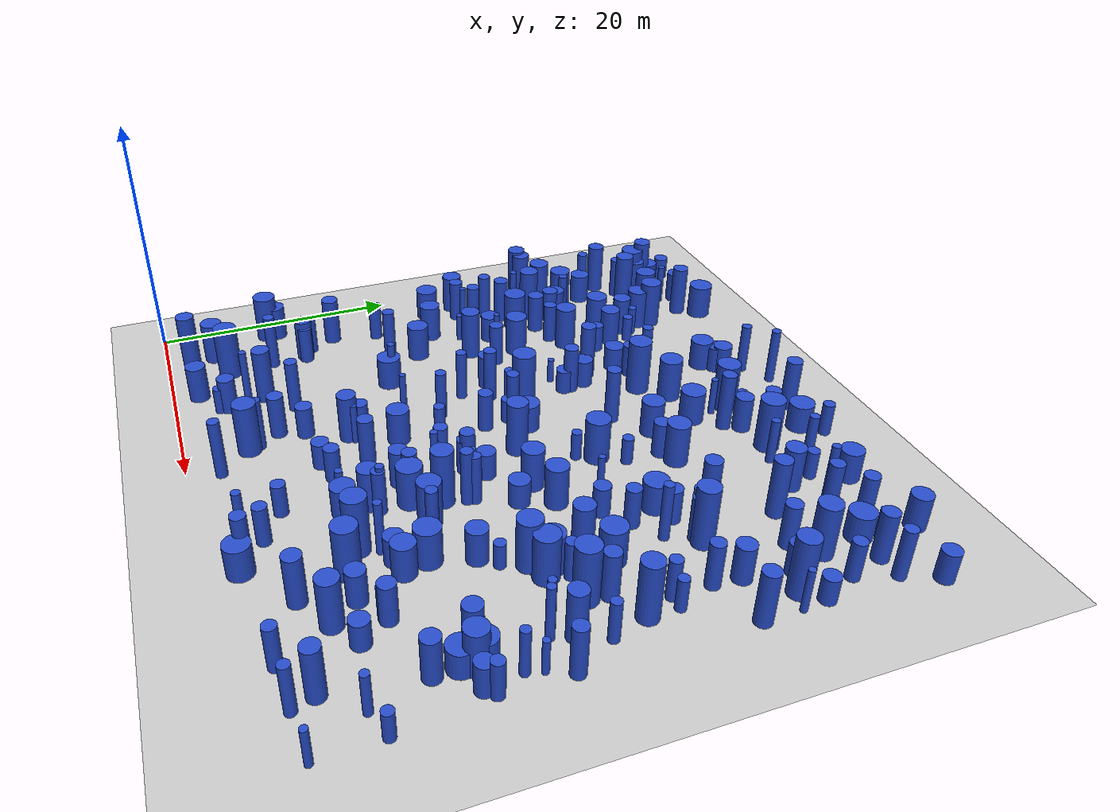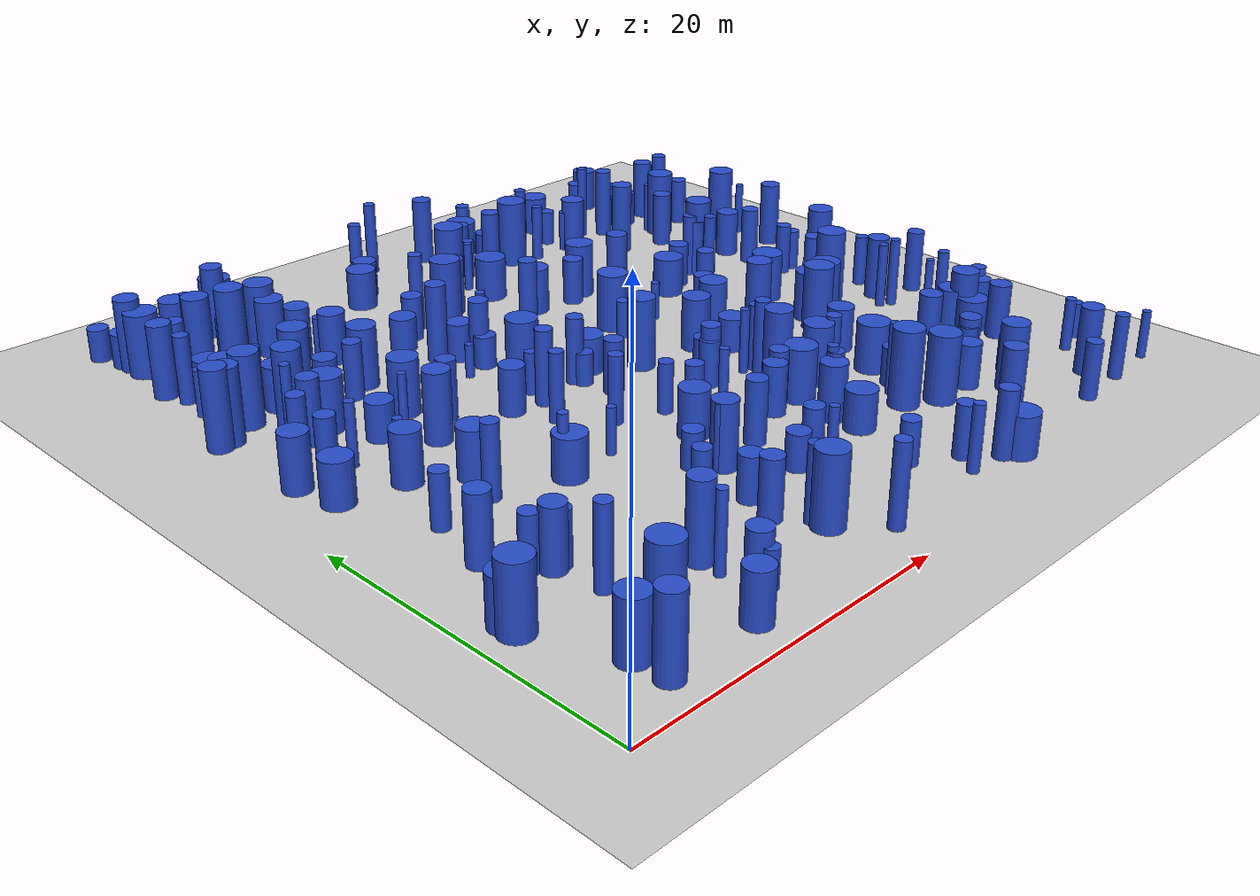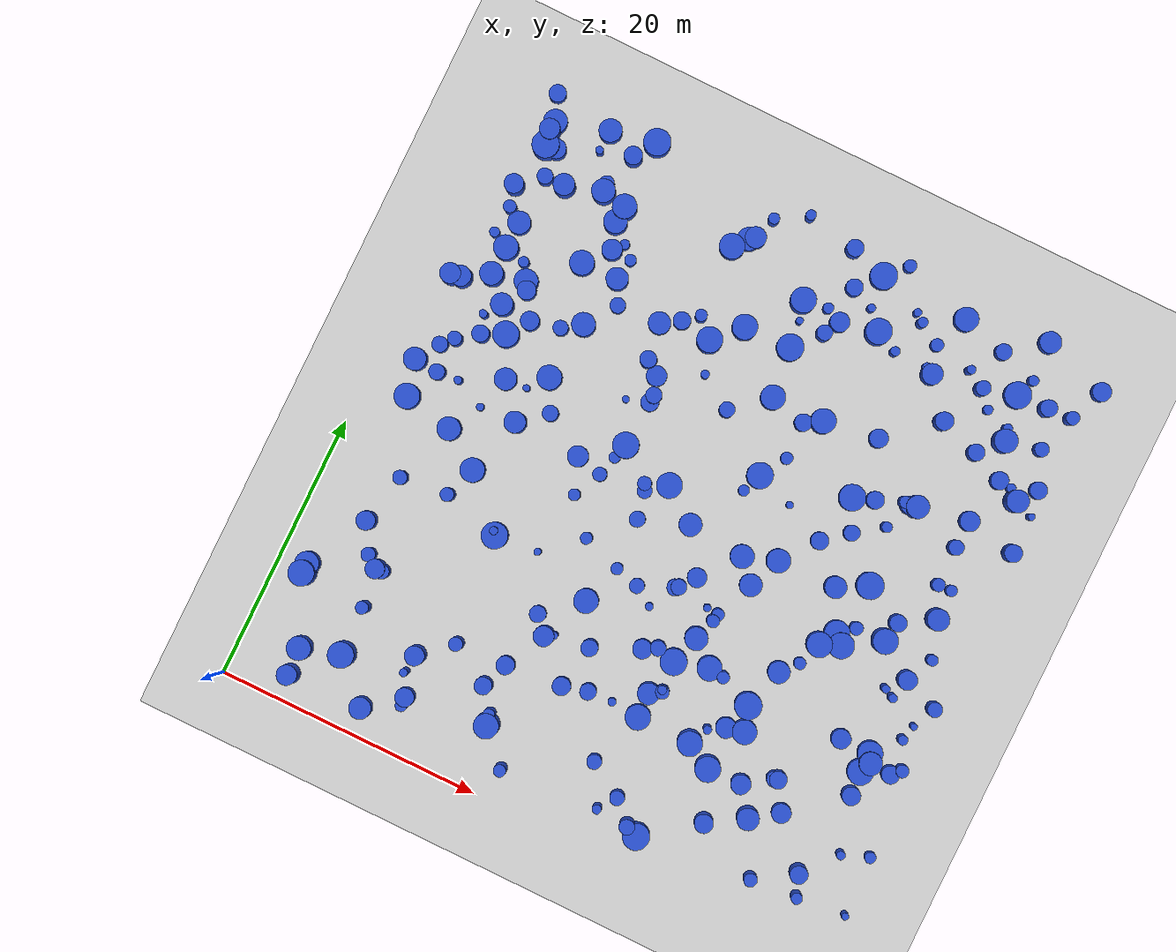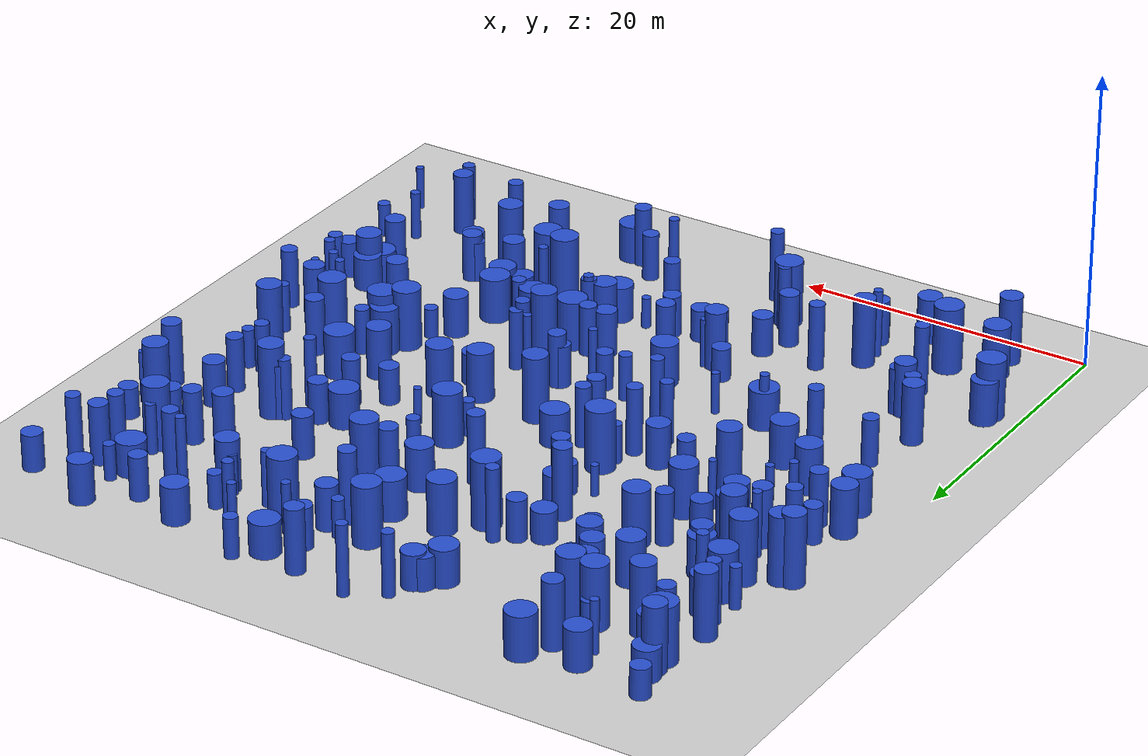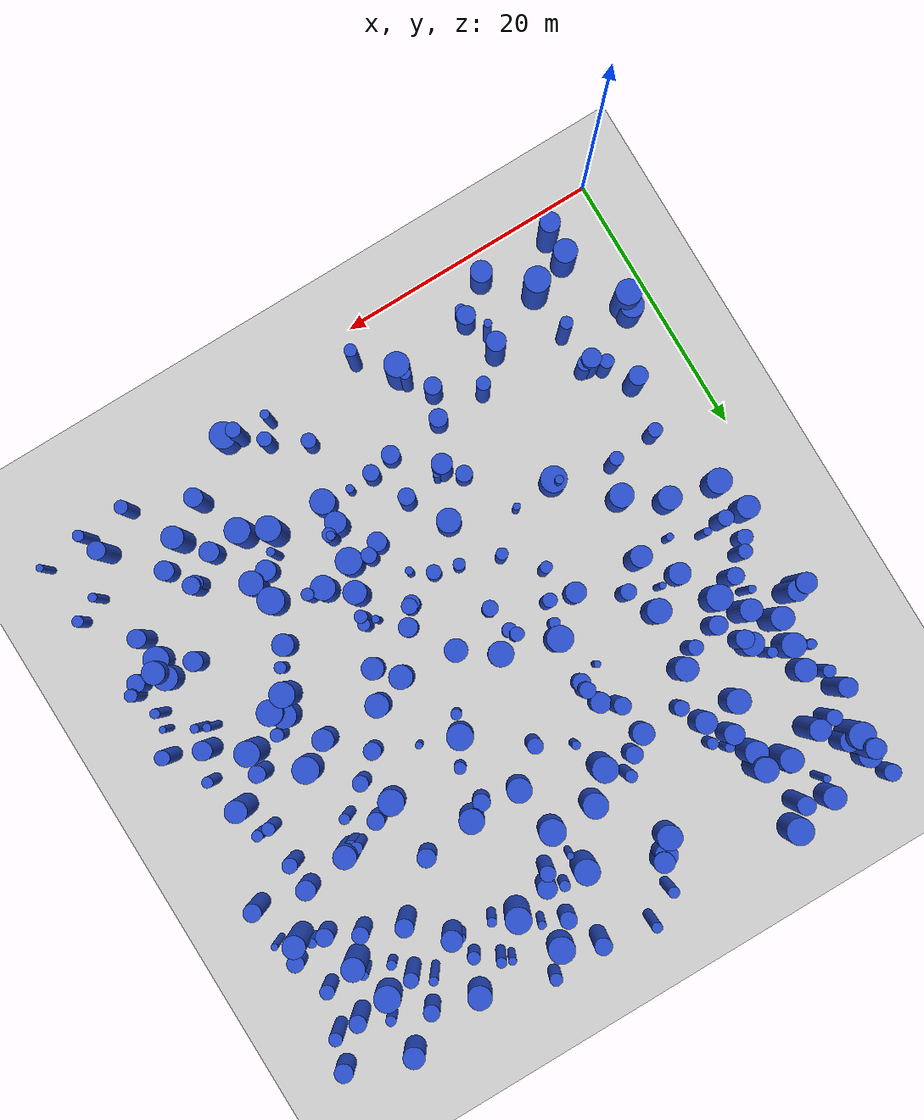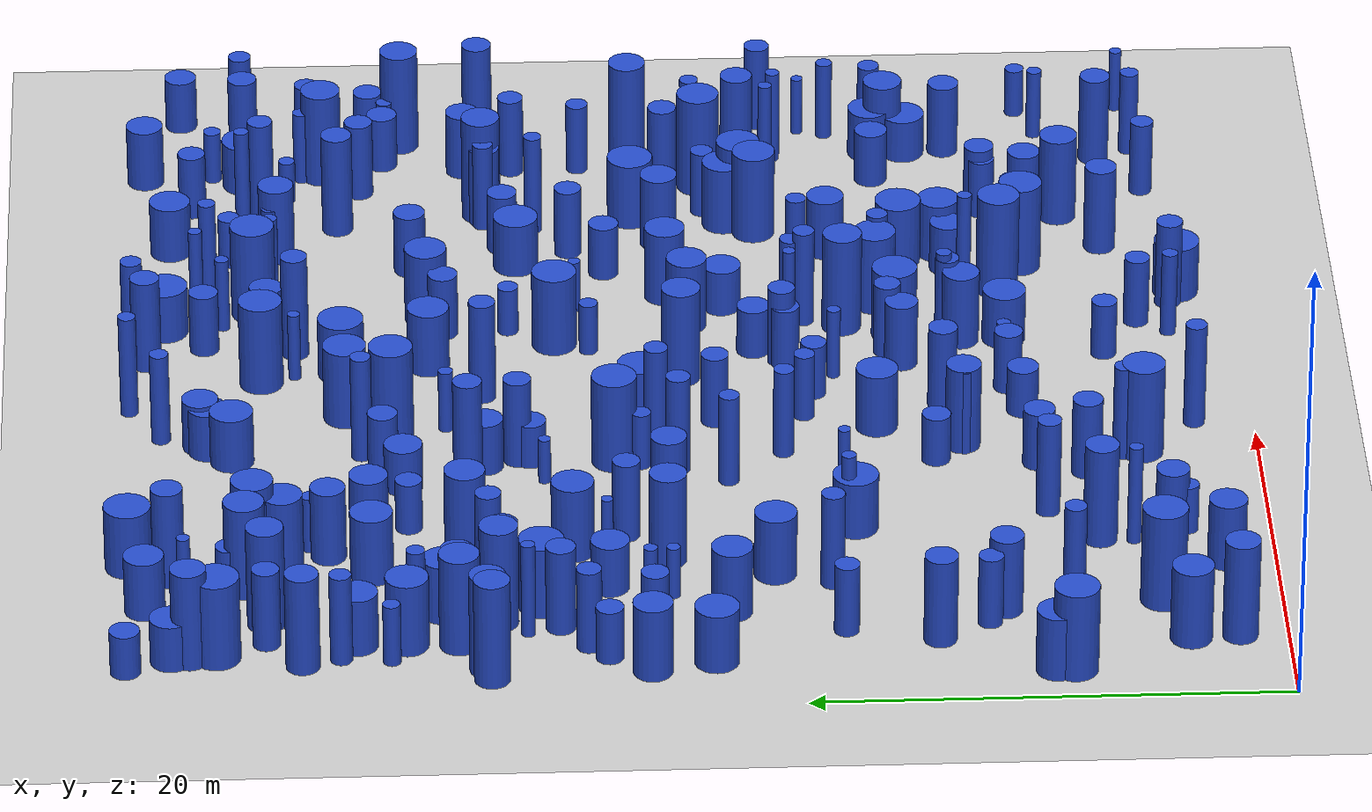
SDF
<sdf version="1.6">
 <world name="default">
  <light name="sun" type="directional">
   <pose>0 0 10 0 -0 0</pose>
   <diffuse>0.8 0.8 0.8 1</diffuse>
   <specular>0.1 0.1 0.1 1</specular>
   <attenuation>
    <range>1000</range>
    <constant>0.9</constant>
    <linear>0.01</linear>
    <quadratic>0.001</quadratic>
   </attenuation>
   <direction>-0.5 0.5 -1</direction>
  </light>
  <model name="ground_plane">
   <static>1</static>
   <link name="link">
    <collision name="collision">
     <geometry><plane><normal>0 0 1</normal><size>100 100</size></plane></geometry>
     <surface><friction><ode><mu>100</mu><mu2>50</mu2></ode></friction></surface>
    </collision>
    <visual name="visual">
     <cast_shadows>0</cast_shadows>
     <geometry><plane><normal>0 0 1</normal><size>100 100</size></plane></geometry>
     <material>
      <script><uri>file://media/materials/scripts/gazebo.material</uri><name>Gazebo/Grey</name></script>
     </material>
    </visual>
   </link>
  </model>
  <gravity>0 0 -9.8</gravity>
  <magnetic_field>6e-06 2.3e-05 -4.2e-05</magnetic_field>
  <atmosphere type="adiabatic"/>
  <physics name="default_physics" default="0" type="ode">
   <max_step_size>0.001</max_step_size>
   <real_time_factor>1</real_time_factor>
   <real_time_update_rate>1000</real_time_update_rate>
  </physics>
  <scene><ambient>0.4 0.4 0.4 1</ambient><background>0.7 0.7 0.7 1</background><shadows>1</shadows></scene>
  <spherical_coordinates>
   <surface_model>EARTH_WGS84</surface_model>
   <latitude_deg>0</latitude_deg>
   <longitude_deg>0</longitude_deg>
   <elevation>0</elevation>
   <heading_deg>0</heading_deg>
  </spherical_coordinates>
  <model name="0">
   <static>0</static>
   <link name="link">
    <inertial>
     <mass>2</mass>
     <inertia><ixx>2.40197</ixx><ixy>0</ixy><ixz>0</ixz><iyy>2.40197</iyy><iyz>0</iyz><izz>0.81177</izz></inertia>
    </inertial>
    <collision name="collision">
     <geometry><cylinder><length>3.46071</length><radius>0.900983</radius></cylinder></geometry>
     <surface><contact><collide_without_contact>1</collide_without_contact></contact></surface>
    </collision>
    <visual name="visual">
     <geometry><cylinder><length>3.46071</length><radius>0.900983</radius></cylinder></geometry>
     <material>
      <script><uri>file://media/materials/scripts/gazebo.material</uri><name>Gazebo/Blue</name></script>
     </material>
    </visual>
    <gravity>0</gravity>
   </link>
   <pose>11.8767 29.2592 1.73036 0 -0 0</pose>
  </model>
  <model name="1">
   <static>0</static>
   <link name="link">
    <inertial>
     <mass>2</mass>
     <inertia>
      <ixx>0.889597</ixx>
      <ixy>0</ixy>
      <ixz>0</ixz>
      <iyy>0.889597</iyy>
      <iyz>0</iyz>
      <izz>0.404641</izz>
     </inertia>
    </inertial>
    <collision name="collision">
     <geometry><cylinder><length>2.03068</length><radius>0.636114</radius></cylinder></geometry>
     <surface><contact><collide_without_contact>1</collide_without_contact></contact></surface>
    </collision>
    <visual name="visual">
     <geometry><cylinder><length>2.03068</length><radius>0.636114</radius></cylinder></geometry>
     <material>
      <script><uri>file://media/materials/scripts/gazebo.material</uri><name>Gazebo/Blue</name></script>
     </material>
    </visual>
    <gravity>0</gravity>
   </link>
   <pose>3.46889 47.8136 1.01534 0 -0 0</pose>
  </model>
  <model name="2">
   <static>0</static>
   <link name="link">
    <inertial>
     <mass>2</mass>
     <inertia>
      <ixx>2.45511</ixx>
      <ixy>0</ixy>
      <ixz>0</ixz>
      <iyy>2.45511</iyy>
      <iyz>0</iyz>
      <izz>0.0849773</izz>
     </inertia>
    </inertial>
    <collision name="collision">
     <geometry><cylinder><length>3.8047</length><radius>0.291509</radius></cylinder></geometry>
     <surface><contact><collide_without_contact>1</collide_without_contact></contact></surface>
    </collision>
    <visual name="visual">
     <geometry><cylinder><length>3.8047</length><radius>0.291509</radius></cylinder></geometry>
     <material>
      <script><uri>file://media/materials/scripts/gazebo.material</uri><name>Gazebo/Blue</name></script>
     </material>
    </visual>
    <gravity>0</gravity>
   </link>
   <pose>6.11121 26.2319 1.90235 0 -0 0</pose>
  </model>
  <model name="3">
   <static>0</static>
   <link name="link">
    <inertial>
     <mass>2</mass>
     <inertia><ixx>3.44328</ixx><ixy>0</ixy><ixz>0</ixz><iyy>3.44328</iyy><iyz>0</iyz><izz>0.742387</izz></inertia>
    </inertial>
    <collision name="collision">
     <geometry><cylinder><length>4.29331</length><radius>0.861619</radius></cylinder></geometry>
     <surface><contact><collide_without_contact>1</collide_without_contact></contact></surface>
    </collision>
    <visual name="visual">
     <geometry><cylinder><length>4.29331</length><radius>0.861619</radius></cylinder></geometry>
     <material>
      <script><uri>file://media/materials/scripts/gazebo.material</uri><name>Gazebo/Blue</name></script>
     </material>
    </visual>
    <gravity>0</gravity>
   </link>
   <pose>9.53934 42.8927 2.14666 0 -0 0</pose>
  </model>
  <model name="4">
   <static>0</static>
   <link name="link">
    <inertial>
     <mass>2</mass>
     <inertia><ixx>1.52078</ixx><ixy>0</ixy><ixz>0</ixz><iyy>1.52078</iyy><iyz>0</iyz><izz>0.706881</izz></inertia>
    </inertial>
    <collision name="collision">
     <geometry><cylinder><length>2.64651</length><radius>0.840762</radius></cylinder></geometry>
     <surface><contact><collide_without_contact>1</collide_without_contact></contact></surface>
    </collision>
    <visual name="visual">
     <geometry><cylinder><length>2.64651</length><radius>0.840762</radius></cylinder></geometry>
     <material>
      <script><uri>file://media/materials/scripts/gazebo.material</uri><name>Gazebo/Blue</name></script>
     </material>
    </visual>
    <gravity>0</gravity>
   </link>
   <pose>5.06571 38.2801 1.32326 0 -0 0</pose>
  </model>
  <model name="5">
   <static>0</static>
   <link name="link">
    <inertial>
     <mass>2</mass>
     <inertia>
      <ixx>1.85446</ixx>
      <ixy>0</ixy>
      <ixz>0</ixz>
      <iyy>1.85446</iyy>
      <iyz>0</iyz>
      <izz>0.0841204</izz>
     </inertia>
    </inertial>
    <collision name="collision">
     <geometry><cylinder><length>3.29763</length><radius>0.290035</radius></cylinder></geometry>
     <surface><contact><collide_without_contact>1</collide_without_contact></contact></surface>
    </collision>
    <visual name="visual">
     <geometry><cylinder><length>3.29763</length><radius>0.290035</radius></cylinder></geometry>
     <material>
      <script><uri>file://media/materials/scripts/gazebo.material</uri><name>Gazebo/Blue</name></script>
     </material>
    </visual>
    <gravity>0</gravity>
   </link>
   <pose>25.4526 17.6829 1.64882 0 -0 0</pose>
  </model>
  <model name="6">
   <static>0</static>
   <link name="link">
    <inertial>
     <mass>2</mass>
     <inertia>
      <ixx>0.798572</ixx>
      <ixy>0</ixy>
      <ixz>0</ixz>
      <iyy>0.798572</iyy>
      <iyz>0</iyz>
      <izz>0.198941</izz>
     </inertia>
    </inertial>
    <collision name="collision">
     <geometry><cylinder><length>2.04807</length><radius>0.446028</radius></cylinder></geometry>
     <surface><contact><collide_without_contact>1</collide_without_contact></contact></surface>
    </collision>
    <visual name="visual">
     <geometry><cylinder><length>2.04807</length><radius>0.446028</radius></cylinder></geometry>
     <material>
      <script><uri>file://media/materials/scripts/gazebo.material</uri><name>Gazebo/Blue</name></script>
     </material>
    </visual>
    <gravity>0</gravity>
   </link>
   <pose>36.9335 18.7301 1.02404 0 -0 0</pose>
  </model>
  <model name="7">
   <static>0</static>
   <link name="link">
    <inertial>
     <mass>2</mass>
     <inertia>
      <ixx>0.786749</ixx>
      <ixy>0</ixy>
      <ixz>0</ixz>
      <iyy>0.786749</iyy>
      <iyz>0</iyz>
      <izz>0.0926018</izz>
     </inertia>
    </inertial>
    <collision name="collision">
     <geometry><cylinder><length>2.10777</length><radius>0.304305</radius></cylinder></geometry>
     <surface><contact><collide_without_contact>1</collide_without_contact></contact></surface>
    </collision>
    <visual name="visual">
     <geometry><cylinder><length>2.10777</length><radius>0.304305</radius></cylinder></geometry>
     <material>
      <script><uri>file://media/materials/scripts/gazebo.material</uri><name>Gazebo/Blue</name></script>
     </material>
    </visual>
    <gravity>0</gravity>
   </link>
   <pose>26.0501 10.3515 1.05388 0 -0 0</pose>
  </model>
  <model name="8">
   <static>0</static>
   <link name="link">
    <inertial>
     <mass>2</mass>
     <inertia><ixx>4.21888</ixx><ixy>0</ixy><ixz>0</ixz><iyy>4.21888</iyy><iyz>0</iyz><izz>0.689911</izz></inertia>
    </inertial>
    <collision name="collision">
     <geometry><cylinder><length>4.82115</length><radius>0.830609</radius></cylinder></geometry>
     <surface><contact><collide_without_contact>1</collide_without_contact></contact></surface>
    </collision>
    <visual name="visual">
     <geometry><cylinder><length>4.82115</length><radius>0.830609</radius></cylinder></geometry>
     <material>
      <script><uri>file://media/materials/scripts/gazebo.material</uri><name>Gazebo/Blue</name></script>
     </material>
    </visual>
    <gravity>0</gravity>
   </link>
   <pose>45.7281 35.9267 2.41058 0 -0 0</pose>
  </model>
  <model name="9">
   <static>0</static>
   <link name="link">
    <inertial>
     <mass>2</mass>
     <inertia><ixx>1.68993</ixx><ixy>0</ixy><ixz>0</ixz><iyy>1.68993</iyy><iyz>0</iyz><izz>0.640182</izz></inertia>
    </inertial>
    <collision name="collision">
     <geometry><cylinder><length>2.86689</length><radius>0.800114</radius></cylinder></geometry>
     <surface><contact><collide_without_contact>1</collide_without_contact></contact></surface>
    </collision>
    <visual name="visual">
     <geometry><cylinder><length>2.86689</length><radius>0.800114</radius></cylinder></geometry>
     <material>
      <script><uri>file://media/materials/scripts/gazebo.material</uri><name>Gazebo/Blue</name></script>
     </material>
    </visual>
    <gravity>0</gravity>
   </link>
   <pose>42.9643 47.197 1.43344 0 -0 0</pose>
  </model>
  <model name="10">
   <static>0</static>
   <link name="link">
    <inertial>
     <mass>2</mass>
     <inertia><ixx>3.37741</ixx><ixy>0</ixy><ixz>0</ixz><iyy>3.37741</iyy><iyz>0</iyz><izz>0.399415</izz></inertia>
    </inertial>
    <collision name="collision">
     <geometry><cylinder><length>4.36649</length><radius>0.631993</radius></cylinder></geometry>
     <surface><contact><collide_without_contact>1</collide_without_contact></contact></surface>
    </collision>
    <visual name="visual">
     <geometry><cylinder><length>4.36649</length><radius>0.631993</radius></cylinder></geometry>
     <material>
      <script><uri>file://media/materials/scripts/gazebo.material</uri><name>Gazebo/Blue</name></script>
     </material>
    </visual>
    <gravity>0</gravity>
   </link>
   <pose>27.4503 47.0755 2.18325 0 -0 0</pose>
  </model>
  <model name="11">
   <static>0</static>
   <link name="link">
    <inertial>
     <mass>2</mass>
     <inertia><ixx>1.88105</ixx><ixy>0</ixy><ixz>0</ixz><iyy>1.88105</iyy><iyz>0</iyz><izz>0.812984</izz></inertia>
    </inertial>
    <collision name="collision">
     <geometry><cylinder><length>2.97445</length><radius>0.901656</radius></cylinder></geometry>
     <surface><contact><collide_without_contact>1</collide_without_contact></contact></surface>
    </collision>
    <visual name="visual">
     <geometry><cylinder><length>2.97445</length><radius>0.901656</radius></cylinder></geometry>
     <material>
      <script><uri>file://media/materials/scripts/gazebo.material</uri><name>Gazebo/Blue</name></script>
     </material>
    </visual>
    <gravity>0</gravity>
   </link>
   <pose>26.8547 34.9896 1.48722 0 -0 0</pose>
  </model>
  <model name="12">
   <static>0</static>
   <link name="link">
    <inertial>
     <mass>2</mass>
     <inertia><ixx>2.82446</ixx><ixy>0</ixy><ixz>0</ixz><iyy>2.82446</iyy><iyz>0</iyz><izz>0.396141</izz></inertia>
    </inertial>
    <collision name="collision">
     <geometry><cylinder><length>3.96967</length><radius>0.629398</radius></cylinder></geometry>
     <surface><contact><collide_without_contact>1</collide_without_contact></contact></surface>
    </collision>
    <visual name="visual">
     <geometry><cylinder><length>3.96967</length><radius>0.629398</radius></cylinder></geometry>
     <material>
      <script><uri>file://media/materials/scripts/gazebo.material</uri><name>Gazebo/Blue</name></script>
     </material>
    </visual>
    <gravity>0</gravity>
   </link>
   <pose>6.09867 29.9204 1.98484 0 -0 0</pose>
  </model>
  <model name="13">
   <static>0</static>
   <link name="link">
    <inertial>
     <mass>2</mass>
     <inertia><ixx>2.71597</ixx><ixy>0</ixy><ixz>0</ixz><iyy>2.71597</iyy><iyz>0</iyz><izz>0.923373</izz></inertia>
    </inertial>
    <collision name="collision">
     <geometry><cylinder><length>3.67773</length><radius>0.960923</radius></cylinder></geometry>
     <surface><contact><collide_without_contact>1</collide_without_contact></contact></surface>
    </collision>
    <visual name="visual">
     <geometry><cylinder><length>3.67773</length><radius>0.960923</radius></cylinder></geometry>
     <material>
      <script><uri>file://media/materials/scripts/gazebo.material</uri><name>Gazebo/Blue</name></script>
     </material>
    </visual>
    <gravity>0</gravity>
   </link>
   <pose>28.4623 29.5513 1.83887 0 -0 0</pose>
  </model>
  <model name="14">
   <static>0</static>
   <link name="link">
    <inertial>
     <mass>2</mass>
     <inertia><ixx>1.62326</ixx><ixy>0</ixy><ixz>0</ixz><iyy>1.62326</iyy><iyz>0</iyz><izz>0.944741</izz></inertia>
    </inertial>
    <collision name="collision">
     <geometry><cylinder><length>2.6278</length><radius>0.971978</radius></cylinder></geometry>
     <surface><contact><collide_without_contact>1</collide_without_contact></contact></surface>
    </collision>
    <visual name="visual">
     <geometry><cylinder><length>2.6278</length><radius>0.971978</radius></cylinder></geometry>
     <material>
      <script><uri>file://media/materials/scripts/gazebo.material</uri><name>Gazebo/Blue</name></script>
     </material>
    </visual>
    <gravity>0</gravity>
   </link>
   <pose>13.2788 17.3958 1.3139 0 -0 0</pose>
  </model>
  <model name="15">
   <static>0</static>
   <link name="link">
    <inertial>
     <mass>2</mass>
     <inertia>
      <ixx>0.941599</ixx>
      <ixy>0</ixy>
      <ixz>0</ixz>
      <iyy>0.941599</iyy>
      <iyz>0</iyz>
      <izz>0.406003</izz>
     </inertia>
    </inertial>
    <collision name="collision">
     <geometry><cylinder><length>2.10513</length><radius>0.637184</radius></cylinder></geometry>
     <surface><contact><collide_without_contact>1</collide_without_contact></contact></surface>
    </collision>
    <visual name="visual">
     <geometry><cylinder><length>2.10513</length><radius>0.637184</radius></cylinder></geometry>
     <material>
      <script><uri>file://media/materials/scripts/gazebo.material</uri><name>Gazebo/Blue</name></script>
     </material>
    </visual>
    <gravity>0</gravity>
   </link>
   <pose>46.8697 37.3288 1.05257 0 -0 0</pose>
  </model>
  <model name="16">
   <static>0</static>
   <link name="link">
    <inertial>
     <mass>2</mass>
     <inertia><ixx>1.57186</ixx><ixy>0</ixy><ixz>0</ixz><iyy>1.57186</iyy><iyz>0</iyz><izz>0.39585</izz></inertia>
    </inertial>
    <collision name="collision">
     <geometry><cylinder><length>2.87117</length><radius>0.629166</radius></cylinder></geometry>
     <surface><contact><collide_without_contact>1</collide_without_contact></contact></surface>
    </collision>
    <visual name="visual">
     <geometry><cylinder><length>2.87117</length><radius>0.629166</radius></cylinder></geometry>
     <material>
      <script><uri>file://media/materials/scripts/gazebo.material</uri><name>Gazebo/Blue</name></script>
     </material>
    </visual>
    <gravity>0</gravity>
   </link>
   <pose>28.6502 44.5978 1.43558 0 -0 0</pose>
  </model>
  <model name="17">
   <static>0</static>
   <link name="link">
    <inertial>
     <mass>2</mass>
     <inertia><ixx>1.66425</ixx><ixy>0</ixy><ixz>0</ixz><iyy>1.66425</iyy><iyz>0</iyz><izz>0.867576</izz></inertia>
    </inertial>
    <collision name="collision">
     <geometry><cylinder><length>2.71712</length><radius>0.931438</radius></cylinder></geometry>
     <surface><contact><collide_without_contact>1</collide_without_contact></contact></surface>
    </collision>
    <visual name="visual">
     <geometry><cylinder><length>2.71712</length><radius>0.931438</radius></cylinder></geometry>
     <material>
      <script><uri>file://media/materials/scripts/gazebo.material</uri><name>Gazebo/Blue</name></script>
     </material>
    </visual>
    <gravity>0</gravity>
   </link>
   <pose>3.28204 23.6146 1.35856 0 -0 0</pose>
  </model>
  <model name="18">
   <static>0</static>
   <link name="link">
    <inertial>
     <mass>2</mass>
     <inertia><ixx>1.93693</ixx><ixy>0</ixy><ixz>0</ixz><iyy>1.93693</iyy><iyz>0</iyz><izz>0.344966</izz></inertia>
    </inertial>
    <collision name="collision">
     <geometry><cylinder><length>3.25372</length><radius>0.587338</radius></cylinder></geometry>
     <surface><contact><collide_without_contact>1</collide_without_contact></contact></surface>
    </collision>
    <visual name="visual">
     <geometry><cylinder><length>3.25372</length><radius>0.587338</radius></cylinder></geometry>
     <material>
      <script><uri>file://media/materials/scripts/gazebo.material</uri><name>Gazebo/Blue</name></script>
     </material>
    </visual>
    <gravity>0</gravity>
   </link>
   <pose>36.1652 28.7323 1.62686 0 -0 0</pose>
  </model>
  <model name="19">
   <static>0</static>
   <link name="link">
    <inertial>
     <mass>2</mass>
     <inertia><ixx>1.56851</ixx><ixy>0</ixy><ixz>0</ixz><iyy>1.56851</iyy><iyz>0</iyz><izz>0.224417</izz></inertia>
    </inertial>
    <collision name="collision">
     <geometry><cylinder><length>2.95598</length><radius>0.473727</radius></cylinder></geometry>
     <surface><contact><collide_without_contact>1</collide_without_contact></contact></surface>
    </collision>
    <visual name="visual">
     <geometry><cylinder><length>2.95598</length><radius>0.473727</radius></cylinder></geometry>
     <material>
      <script><uri>file://media/materials/scripts/gazebo.material</uri><name>Gazebo/Blue</name></script>
     </material>
    </visual>
    <gravity>0</gravity>
   </link>
   <pose>46.86 15.0199 1.47799 0 -0 0</pose>
  </model>
  <model name="20">
   <static>0</static>
   <link name="link">
    <inertial>
     <mass>2</mass>
     <inertia><ixx>3.66593</ixx><ixy>0</ixy><ixz>0</ixz><iyy>3.66593</iyy><iyz>0</iyz><izz>0.841816</izz></inertia>
    </inertial>
    <collision name="collision">
     <geometry><cylinder><length>4.4125</length><radius>0.917505</radius></cylinder></geometry>
     <surface><contact><collide_without_contact>1</collide_without_contact></contact></surface>
    </collision>
    <visual name="visual">
     <geometry><cylinder><length>4.4125</length><radius>0.917505</radius></cylinder></geometry>
     <material>
      <script><uri>file://media/materials/scripts/gazebo.material</uri><name>Gazebo/Blue</name></script>
     </material>
    </visual>
    <gravity>0</gravity>
   </link>
   <pose>18.7168 4.95866 2.20625 0 -0 0</pose>
  </model>
  <model name="21">
   <static>0</static>
   <link name="link">
    <inertial>
     <mass>2</mass>
     <inertia><ixx>3.67494</ixx><ixy>0</ixy><ixz>0</ixz><iyy>3.67494</iyy><iyz>0</iyz><izz>0.558673</izz></inertia>
    </inertial>
    <collision name="collision">
     <geometry><cylinder><length>4.51371</length><radius>0.747444</radius></cylinder></geometry>
     <surface><contact><collide_without_contact>1</collide_without_contact></contact></surface>
    </collision>
    <visual name="visual">
     <geometry><cylinder><length>4.51371</length><radius>0.747444</radius></cylinder></geometry>
     <material>
      <script><uri>file://media/materials/scripts/gazebo.material</uri><name>Gazebo/Blue</name></script>
     </material>
    </visual>
    <gravity>0</gravity>
   </link>
   <pose>4.16992 45.1792 2.25686 0 -0 0</pose>
  </model>
  <model name="22">
   <static>0</static>
   <link name="link">
    <inertial>
     <mass>2</mass>
     <inertia><ixx>2.6096</ixx><ixy>0</ixy><ixz>0</ixz><iyy>2.6096</iyy><iyz>0</iyz><izz>0.20705</izz></inertia>
    </inertial>
    <collision name="collision">
     <geometry><cylinder><length>3.87769</length><radius>0.455027</radius></cylinder></geometry>
     <surface><contact><collide_without_contact>1</collide_without_contact></contact></surface>
    </collision>
    <visual name="visual">
     <geometry><cylinder><length>3.87769</length><radius>0.455027</radius></cylinder></geometry>
     <material>
      <script><uri>file://media/materials/scripts/gazebo.material</uri><name>Gazebo/Blue</name></script>
     </material>
    </visual>
    <gravity>0</gravity>
   </link>
   <pose>32.4033 15.4487 1.93884 0 -0 0</pose>
  </model>
  <model name="23">
   <static>0</static>
   <link name="link">
    <inertial>
     <mass>2</mass>
     <inertia>
      <ixx>3.22473</ixx>
      <ixy>0</ixy>
      <ixz>0</ixz>
      <iyy>3.22473</iyy>
      <iyz>0</iyz>
      <izz>0.0871934</izz>
     </inertia>
    </inertial>
    <collision name="collision">
     <geometry><cylinder><length>4.36884</length><radius>0.295285</radius></cylinder></geometry>
     <surface><contact><collide_without_contact>1</collide_without_contact></contact></surface>
    </collision>
    <visual name="visual">
     <geometry><cylinder><length>4.36884</length><radius>0.295285</radius></cylinder></geometry>
     <material>
      <script><uri>file://media/materials/scripts/gazebo.material</uri><name>Gazebo/Blue</name></script>
     </material>
    </visual>
    <gravity>0</gravity>
   </link>
   <pose>5.68019 31.273 2.18442 0 -0 0</pose>
  </model>
  <model name="24">
   <static>0</static>
   <link name="link">
    <inertial>
     <mass>2</mass>
     <inertia><ixx>2.50462</ixx><ixy>0</ixy><ixz>0</ixz><iyy>2.50462</iyy><iyz>0</iyz><izz>0.451325</izz></inertia>
    </inertial>
    <collision name="collision">
     <geometry><cylinder><length>3.69781</length><radius>0.671807</radius></cylinder></geometry>
     <surface><contact><collide_without_contact>1</collide_without_contact></contact></surface>
    </collision>
    <visual name="visual">
     <geometry><cylinder><length>3.69781</length><radius>0.671807</radius></cylinder></geometry>
     <material>
      <script><uri>file://media/materials/scripts/gazebo.material</uri><name>Gazebo/Blue</name></script>
     </material>
    </visual>
    <gravity>0</gravity>
   </link>
   <pose>39.0289 32.3304 1.8489 0 -0 0</pose>
  </model>
  <model name="25">
   <static>0</static>
   <link name="link">
    <inertial>
     <mass>2</mass>
     <inertia><ixx>2.00158</ixx><ixy>0</ixy><ixz>0</ixz><iyy>2.00158</iyy><iyz>0</iyz><izz>0.12036</izz></inertia>
    </inertial>
    <collision name="collision">
     <geometry><cylinder><length>3.41298</length><radius>0.346929</radius></cylinder></geometry>
     <surface><contact><collide_without_contact>1</collide_without_contact></contact></surface>
    </collision>
    <visual name="visual">
     <geometry><cylinder><length>3.41298</length><radius>0.346929</radius></cylinder></geometry>
     <material>
      <script><uri>file://media/materials/scripts/gazebo.material</uri><name>Gazebo/Blue</name></script>
     </material>
    </visual>
    <gravity>0</gravity>
   </link>
   <pose>42.8894 40.3109 1.70649 0 -0 0</pose>
  </model>
  <model name="26">
   <static>0</static>
   <link name="link">
    <inertial>
     <mass>2</mass>
     <inertia><ixx>2.48469</ixx><ixy>0</ixy><ixz>0</ixz><iyy>2.48469</iyy><iyz>0</iyz><izz>0.314146</izz></inertia>
    </inertial>
    <collision name="collision">
     <geometry><cylinder><length>3.73707</length><radius>0.560487</radius></cylinder></geometry>
     <surface><contact><collide_without_contact>1</collide_without_contact></contact></surface>
    </collision>
    <visual name="visual">
     <geometry><cylinder><length>3.73707</length><radius>0.560487</radius></cylinder></geometry>
     <material>
      <script><uri>file://media/materials/scripts/gazebo.material</uri><name>Gazebo/Blue</name></script>
     </material>
    </visual>
    <gravity>0</gravity>
   </link>
   <pose>43.2934 31.0546 1.86853 0 -0 0</pose>
  </model>
  <model name="27">
   <static>0</static>
   <link name="link">
    <inertial>
     <mass>2</mass>
     <inertia><ixx>3.29031</ixx><ixy>0</ixy><ixz>0</ixz><iyy>3.29031</iyy><iyz>0</iyz><izz>0.876091</izz></inertia>
    </inertial>
    <collision name="collision">
     <geometry><cylinder><length>4.13686</length><radius>0.935998</radius></cylinder></geometry>
     <surface><contact><collide_without_contact>1</collide_without_contact></contact></surface>
    </collision>
    <visual name="visual">
     <geometry><cylinder><length>4.13686</length><radius>0.935998</radius></cylinder></geometry>
     <material>
      <script><uri>file://media/materials/scripts/gazebo.material</uri><name>Gazebo/Blue</name></script>
     </material>
    </visual>
    <gravity>0</gravity>
   </link>
   <pose>25.7568 42.1534 2.06843 0 -0 0</pose>
  </model>
  <model name="28">
   <static>0</static>
   <link name="link">
    <inertial>
     <mass>2</mass>
     <inertia><ixx>3.70127</ixx><ixy>0</ixy><ixz>0</ixz><iyy>3.70127</iyy><iyz>0</iyz><izz>0.908045</izz></inertia>
    </inertial>
    <collision name="collision">
     <geometry><cylinder><length>4.41401</length><radius>0.952914</radius></cylinder></geometry>
     <surface><contact><collide_without_contact>1</collide_without_contact></contact></surface>
    </collision>
    <visual name="visual">
     <geometry><cylinder><length>4.41401</length><radius>0.952914</radius></cylinder></geometry>
     <material>
      <script><uri>file://media/materials/scripts/gazebo.material</uri><name>Gazebo/Blue</name></script>
     </material>
    </visual>
    <gravity>0</gravity>
   </link>
   <pose>31.5585 42.4736 2.20701 0 -0 0</pose>
  </model>
  <model name="29">
   <static>0</static>
   <link name="link">
    <inertial>
     <mass>2</mass>
     <inertia><ixx>2.78165</ixx><ixy>0</ixy><ixz>0</ixz><iyy>2.78165</iyy><iyz>0</iyz><izz>0.746331</izz></inertia>
    </inertial>
    <collision name="collision">
     <geometry><cylinder><length>3.80143</length><radius>0.863904</radius></cylinder></geometry>
     <surface><contact><collide_without_contact>1</collide_without_contact></contact></surface>
    </collision>
    <visual name="visual">
     <geometry><cylinder><length>3.80143</length><radius>0.863904</radius></cylinder></geometry>
     <material>
      <script><uri>file://media/materials/scripts/gazebo.material</uri><name>Gazebo/Blue</name></script>
     </material>
    </visual>
    <gravity>0</gravity>
   </link>
   <pose>12.4132 33.7284 1.90072 0 -0 0</pose>
  </model>
  <model name="30">
   <static>0</static>
   <link name="link">
    <inertial>
     <mass>2</mass>
     <inertia><ixx>1.34983</ixx><ixy>0</ixy><ixz>0</ixz><iyy>1.34983</iyy><iyz>0</iyz><izz>0.973345</izz></inertia>
    </inertial>
    <collision name="collision">
     <geometry><cylinder><length>2.27573</length><radius>0.986583</radius></cylinder></geometry>
     <surface><contact><collide_without_contact>1</collide_without_contact></contact></surface>
    </collision>
    <visual name="visual">
     <geometry><cylinder><length>2.27573</length><radius>0.986583</radius></cylinder></geometry>
     <material>
      <script><uri>file://media/materials/scripts/gazebo.material</uri><name>Gazebo/Blue</name></script>
     </material>
    </visual>
    <gravity>0</gravity>
   </link>
   <pose>42.5501 42.8164 1.13786 0 -0 0</pose>
  </model>
  <model name="31">
   <static>0</static>
   <link name="link">
    <inertial>
     <mass>2</mass>
     <inertia>
      <ixx>0.960927</ixx>
      <ixy>0</ixy>
      <ixz>0</ixz>
      <iyy>0.960927</iyy>
      <iyz>0</iyz>
      <izz>0.413143</izz>
     </inertia>
    </inertial>
    <collision name="collision">
     <geometry><cylinder><length>2.12747</length><radius>0.642762</radius></cylinder></geometry>
     <surface><contact><collide_without_contact>1</collide_without_contact></contact></surface>
    </collision>
    <visual name="visual">
     <geometry><cylinder><length>2.12747</length><radius>0.642762</radius></cylinder></geometry>
     <material>
      <script><uri>file://media/materials/scripts/gazebo.material</uri><name>Gazebo/Blue</name></script>
     </material>
    </visual>
    <gravity>0</gravity>
   </link>
   <pose>29.9876 46.2303 1.06374 0 -0 0</pose>
  </model>
  <model name="32">
   <static>0</static>
   <link name="link">
    <inertial>
     <mass>2</mass>
     <inertia><ixx>1.10606</ixx><ixy>0</ixy><ixz>0</ixz><iyy>1.10606</iyy><iyz>0</iyz><izz>0.512174</izz></inertia>
    </inertial>
    <collision name="collision">
     <geometry><cylinder><length>2.25828</length><radius>0.715663</radius></cylinder></geometry>
     <surface><contact><collide_without_contact>1</collide_without_contact></contact></surface>
    </collision>
    <visual name="visual">
     <geometry><cylinder><length>2.25828</length><radius>0.715663</radius></cylinder></geometry>
     <material>
      <script><uri>file://media/materials/scripts/gazebo.material</uri><name>Gazebo/Blue</name></script>
     </material>
    </visual>
    <gravity>0</gravity>
   </link>
   <pose>27.6259 21.0165 1.12914 0 -0 0</pose>
  </model>
  <model name="33">
   <static>0</static>
   <link name="link">
    <inertial>
     <mass>2</mass>
     <inertia><ixx>3.10542</ixx><ixy>0</ixy><ixz>0</ixz><iyy>3.10542</iyy><iyz>0</iyz><izz>0.188951</izz></inertia>
    </inertial>
    <collision name="collision">
     <geometry><cylinder><length>4.25037</length><radius>0.434685</radius></cylinder></geometry>
     <surface><contact><collide_without_contact>1</collide_without_contact></contact></surface>
    </collision>
    <visual name="visual">
     <geometry><cylinder><length>4.25037</length><radius>0.434685</radius></cylinder></geometry>
     <material>
      <script><uri>file://media/materials/scripts/gazebo.material</uri><name>Gazebo/Blue</name></script>
     </material>
    </visual>
    <gravity>0</gravity>
   </link>
   <pose>17.1407 22.5153 2.12519 0 -0 0</pose>
  </model>
  <model name="34">
   <static>0</static>
   <link name="link">
    <inertial>
     <mass>2</mass>
     <inertia>
      <ixx>2.68848</ixx>
      <ixy>0</ixy>
      <ixz>0</ixz>
      <iyy>2.68848</iyy>
      <iyz>0</iyz>
      <izz>0.0949899</izz>
     </inertia>
    </inertial>
    <collision name="collision">
     <geometry><cylinder><length>3.98069</length><radius>0.308204</radius></cylinder></geometry>
     <surface><contact><collide_without_contact>1</collide_without_contact></contact></surface>
    </collision>
    <visual name="visual">
     <geometry><cylinder><length>3.98069</length><radius>0.308204</radius></cylinder></geometry>
     <material>
      <script><uri>file://media/materials/scripts/gazebo.material</uri><name>Gazebo/Blue</name></script>
     </material>
    </visual>
    <gravity>0</gravity>
   </link>
   <pose>19.1357 12.4341 1.99035 0 -0 0</pose>
  </model>
  <model name="35">
   <static>0</static>
   <link name="link">
    <inertial>
     <mass>2</mass>
     <inertia><ixx>4.18085</ixx><ixy>0</ixy><ixz>0</ixz><iyy>4.18085</iyy><iyz>0</iyz><izz>0.105493</izz></inertia>
    </inertial>
    <collision name="collision">
     <geometry><cylinder><length>4.97681</length><radius>0.324796</radius></cylinder></geometry>
     <surface><contact><collide_without_contact>1</collide_without_contact></contact></surface>
    </collision>
    <visual name="visual">
     <geometry><cylinder><length>4.97681</length><radius>0.324796</radius></cylinder></geometry>
     <material>
      <script><uri>file://media/materials/scripts/gazebo.material</uri><name>Gazebo/Blue</name></script>
     </material>
    </visual>
    <gravity>0</gravity>
   </link>
   <pose>38.6592 42.8925 2.4884 0 -0 0</pose>
  </model>
  <model name="36">
   <static>0</static>
   <link name="link">
    <inertial>
     <mass>2</mass>
     <inertia><ixx>1.08426</ixx><ixy>0</ixy><ixz>0</ixz><iyy>1.08426</iyy><iyz>0</iyz><izz>0.683304</izz></inertia>
    </inertial>
    <collision name="collision">
     <geometry><cylinder><length>2.11084</length><radius>0.826622</radius></cylinder></geometry>
     <surface><contact><collide_without_contact>1</collide_without_contact></contact></surface>
    </collision>
    <visual name="visual">
     <geometry><cylinder><length>2.11084</length><radius>0.826622</radius></cylinder></geometry>
     <material>
      <script><uri>file://media/materials/scripts/gazebo.material</uri><name>Gazebo/Blue</name></script>
     </material>
    </visual>
    <gravity>0</gravity>
   </link>
   <pose>31.3215 22.2177 1.05542 0 -0 0</pose>
  </model>
  <model name="37">
   <static>0</static>
   <link name="link">
    <inertial>
     <mass>2</mass>
     <inertia><ixx>2.41909</ixx><ixy>0</ixy><ixz>0</ixz><iyy>2.41909</iyy><iyz>0</iyz><izz>0.120372</izz></inertia>
    </inertial>
    <collision name="collision">
     <geometry><cylinder><length>3.76211</length><radius>0.346947</radius></cylinder></geometry>
     <surface><contact><collide_without_contact>1</collide_without_contact></contact></surface>
    </collision>
    <visual name="visual">
     <geometry><cylinder><length>3.76211</length><radius>0.346947</radius></cylinder></geometry>
     <material>
      <script><uri>file://media/materials/scripts/gazebo.material</uri><name>Gazebo/Blue</name></script>
     </material>
    </visual>
    <gravity>0</gravity>
   </link>
   <pose>33.2468 41.7347 1.88105 0 -0 0</pose>
  </model>
  <model name="38">
   <static>0</static>
   <link name="link">
    <inertial>
     <mass>2</mass>
     <inertia><ixx>1.23877</ixx><ixy>0</ixy><ixz>0</ixz><iyy>1.23877</iyy><iyz>0</iyz><izz>0.661511</izz></inertia>
    </inertial>
    <collision name="collision">
     <geometry><cylinder><length>2.33412</length><radius>0.813333</radius></cylinder></geometry>
     <surface><contact><collide_without_contact>1</collide_without_contact></contact></surface>
    </collision>
    <visual name="visual">
     <geometry><cylinder><length>2.33412</length><radius>0.813333</radius></cylinder></geometry>
     <material>
      <script><uri>file://media/materials/scripts/gazebo.material</uri><name>Gazebo/Blue</name></script>
     </material>
    </visual>
    <gravity>0</gravity>
   </link>
   <pose>9.0777 27.7968 1.16706 0 -0 0</pose>
  </model>
  <model name="39">
   <static>0</static>
   <link name="link">
    <inertial>
     <mass>2</mass>
     <inertia><ixx>1.53544</ixx><ixy>0</ixy><ixz>0</ixz><iyy>1.53544</iyy><iyz>0</iyz><izz>0.411838</izz></inertia>
    </inertial>
    <collision name="collision">
     <geometry><cylinder><length>2.82438</length><radius>0.641746</radius></cylinder></geometry>
     <surface><contact><collide_without_contact>1</collide_without_contact></contact></surface>
    </collision>
    <visual name="visual">
     <geometry><cylinder><length>2.82438</length><radius>0.641746</radius></cylinder></geometry>
     <material>
      <script><uri>file://media/materials/scripts/gazebo.material</uri><name>Gazebo/Blue</name></script>
     </material>
    </visual>
    <gravity>0</gravity>
   </link>
   <pose>18.6007 37.0653 1.41219 0 -0 0</pose>
  </model>
  <model name="40">
   <static>0</static>
   <link name="link">
    <inertial>
     <mass>2</mass>
     <inertia><ixx>1.05673</ixx><ixy>0</ixy><ixz>0</ixz><iyy>1.05673</iyy><iyz>0</iyz><izz>0.145747</izz></inertia>
    </inertial>
    <collision name="collision">
     <geometry><cylinder><length>2.42964</length><radius>0.381768</radius></cylinder></geometry>
     <surface><contact><collide_without_contact>1</collide_without_contact></contact></surface>
    </collision>
    <visual name="visual">
     <geometry><cylinder><length>2.42964</length><radius>0.381768</radius></cylinder></geometry>
     <material>
      <script><uri>file://media/materials/scripts/gazebo.material</uri><name>Gazebo/Blue</name></script>
     </material>
    </visual>
    <gravity>0</gravity>
   </link>
   <pose>43.0934 44.2266 1.21482 0 -0 0</pose>
  </model>
  <model name="41">
   <static>0</static>
   <link name="link">
    <inertial>
     <mass>2</mass>
     <inertia><ixx>1.91434</ixx><ixy>0</ixy><ixz>0</ixz><iyy>1.91434</iyy><iyz>0</iyz><izz>0.273493</izz></inertia>
    </inertial>
    <collision name="collision">
     <geometry><cylinder><length>3.26581</length><radius>0.522966</radius></cylinder></geometry>
     <surface><contact><collide_without_contact>1</collide_without_contact></contact></surface>
    </collision>
    <visual name="visual">
     <geometry><cylinder><length>3.26581</length><radius>0.522966</radius></cylinder></geometry>
     <material>
      <script><uri>file://media/materials/scripts/gazebo.material</uri><name>Gazebo/Blue</name></script>
     </material>
    </visual>
    <gravity>0</gravity>
   </link>
   <pose>5.77971 12.2342 1.63291 0 -0 0</pose>
  </model>
  <model name="42">
   <static>0</static>
   <link name="link">
    <inertial>
     <mass>2</mass>
     <inertia><ixx>2.01453</ixx><ixy>0</ixy><ixz>0</ixz><iyy>2.01453</iyy><iyz>0</iyz><izz>0.344549</izz></inertia>
    </inertial>
    <collision name="collision">
     <geometry><cylinder><length>3.32468</length><radius>0.586983</radius></cylinder></geometry>
     <surface><contact><collide_without_contact>1</collide_without_contact></contact></surface>
    </collision>
    <visual name="visual">
     <geometry><cylinder><length>3.32468</length><radius>0.586983</radius></cylinder></geometry>
     <material>
      <script><uri>file://media/materials/scripts/gazebo.material</uri><name>Gazebo/Blue</name></script>
     </material>
    </visual>
    <gravity>0</gravity>
   </link>
   <pose>21.9562 22.9154 1.66234 0 -0 0</pose>
  </model>
  <model name="43">
   <static>0</static>
   <link name="link">
    <inertial>
     <mass>2</mass>
     <inertia><ixx>2.34581</ixx><ixy>0</ixy><ixz>0</ixz><iyy>2.34581</iyy><iyz>0</iyz><izz>0.257799</izz></inertia>
    </inertial>
    <collision name="collision">
     <geometry><cylinder><length>3.64712</length><radius>0.507739</radius></cylinder></geometry>
     <surface><contact><collide_without_contact>1</collide_without_contact></contact></surface>
    </collision>
    <visual name="visual">
     <geometry><cylinder><length>3.64712</length><radius>0.507739</radius></cylinder></geometry>
     <material>
      <script><uri>file://media/materials/scripts/gazebo.material</uri><name>Gazebo/Blue</name></script>
     </material>
    </visual>
    <gravity>0</gravity>
   </link>
   <pose>28.9554 12.6154 1.82356 0 -0 0</pose>
  </model>
  <model name="44">
   <static>0</static>
   <link name="link">
    <inertial>
     <mass>2</mass>
     <inertia><ixx>1.1939</ixx><ixy>0</ixy><ixz>0</ixz><iyy>1.1939</iyy><iyz>0</iyz><izz>0.566577</izz></inertia>
    </inertial>
    <collision name="collision">
     <geometry><cylinder><length>2.33744</length><radius>0.752713</radius></cylinder></geometry>
     <surface><contact><collide_without_contact>1</collide_without_contact></contact></surface>
    </collision>
    <visual name="visual">
     <geometry><cylinder><length>2.33744</length><radius>0.752713</radius></cylinder></geometry>
     <material>
      <script><uri>file://media/materials/scripts/gazebo.material</uri><name>Gazebo/Blue</name></script>
     </material>
    </visual>
    <gravity>0</gravity>
   </link>
   <pose>34.1931 12.2769 1.16872 0 -0 0</pose>
  </model>
  <model name="45">
   <static>0</static>
   <link name="link">
    <inertial>
     <mass>2</mass>
     <inertia>
      <ixx>3.27441</ixx>
      <ixy>0</ixy>
      <ixz>0</ixz>
      <iyy>3.27441</iyy>
      <iyz>0</iyz>
      <izz>0.0994808</izz>
     </inertia>
    </inertial>
    <collision name="collision">
     <geometry><cylinder><length>4.39864</length><radius>0.315406</radius></cylinder></geometry>
     <surface><contact><collide_without_contact>1</collide_without_contact></contact></surface>
    </collision>
    <visual name="visual">
     <geometry><cylinder><length>4.39864</length><radius>0.315406</radius></cylinder></geometry>
     <material>
      <script><uri>file://media/materials/scripts/gazebo.material</uri><name>Gazebo/Blue</name></script>
     </material>
    </visual>
    <gravity>0</gravity>
   </link>
   <pose>43.9023 19.4399 2.19932 0 -0 0</pose>
  </model>
  <model name="46">
   <static>0</static>
   <link name="link">
    <inertial>
     <mass>2</mass>
     <inertia><ixx>3.85343</ixx><ixy>0</ixy><ixz>0</ixz><iyy>3.85343</iyy><iyz>0</iyz><izz>0.911922</izz></inertia>
    </inertial>
    <collision name="collision">
     <geometry><cylinder><length>4.51496</length><radius>0.954946</radius></cylinder></geometry>
     <surface><contact><collide_without_contact>1</collide_without_contact></contact></surface>
    </collision>
    <visual name="visual">
     <geometry><cylinder><length>4.51496</length><radius>0.954946</radius></cylinder></geometry>
     <material>
      <script><uri>file://media/materials/scripts/gazebo.material</uri><name>Gazebo/Blue</name></script>
     </material>
    </visual>
    <gravity>0</gravity>
   </link>
   <pose>7.20316 4.98001 2.25748 0 -0 0</pose>
  </model>
  <model name="47">
   <static>0</static>
   <link name="link">
    <inertial>
     <mass>2</mass>
     <inertia><ixx>2.29041</ixx><ixy>0</ixy><ixz>0</ixz><iyy>2.29041</iyy><iyz>0</iyz><izz>0.757429</izz></inertia>
    </inertial>
    <collision name="collision">
     <geometry><cylinder><length>3.38677</length><radius>0.870304</radius></cylinder></geometry>
     <surface><contact><collide_without_contact>1</collide_without_contact></contact></surface>
    </collision>
    <visual name="visual">
     <geometry><cylinder><length>3.38677</length><radius>0.870304</radius></cylinder></geometry>
     <material>
      <script><uri>file://media/materials/scripts/gazebo.material</uri><name>Gazebo/Blue</name></script>
     </material>
    </visual>
    <gravity>0</gravity>
   </link>
   <pose>29.8515 23.8039 1.69338 0 -0 0</pose>
  </model>
  <model name="48">
   <static>0</static>
   <link name="link">
    <inertial>
     <mass>2</mass>
     <inertia>
      <ixx>0.820157</ixx>
      <ixy>0</ixy>
      <ixz>0</ixz>
      <iyy>0.820157</iyy>
      <iyz>0</iyz>
      <izz>0.29591</izz>
     </inertia>
    </inertial>
    <collision name="collision">
     <geometry><cylinder><length>2.00829</length><radius>0.543976</radius></cylinder></geometry>
     <surface><contact><collide_without_contact>1</collide_without_contact></contact></surface>
    </collision>
    <visual name="visual">
     <geometry><cylinder><length>2.00829</length><radius>0.543976</radius></cylinder></geometry>
     <material>
      <script><uri>file://media/materials/scripts/gazebo.material</uri><name>Gazebo/Blue</name></script>
     </material>
    </visual>
    <gravity>0</gravity>
   </link>
   <pose>21.5362 24.945 1.00414 0 -0 0</pose>
  </model>
  <model name="49">
   <static>0</static>
   <link name="link">
    <inertial>
     <mass>2</mass>
     <inertia><ixx>3.34845</ixx><ixy>0</ixy><ixz>0</ixz><iyy>3.34845</iyy><iyz>0</iyz><izz>0.625624</izz></inertia>
    </inertial>
    <collision name="collision">
     <geometry><cylinder><length>4.26777</length><radius>0.790964</radius></cylinder></geometry>
     <surface><contact><collide_without_contact>1</collide_without_contact></contact></surface>
    </collision>
    <visual name="visual">
     <geometry><cylinder><length>4.26777</length><radius>0.790964</radius></cylinder></geometry>
     <material>
      <script><uri>file://media/materials/scripts/gazebo.material</uri><name>Gazebo/Blue</name></script>
     </material>
    </visual>
    <gravity>0</gravity>
   </link>
   <pose>11.0842 25.3159 2.13388 0 -0 0</pose>
  </model>
  <model name="50">
   <static>0</static>
   <link name="link">
    <inertial>
     <mass>2</mass>
     <inertia><ixx>1.52309</ixx><ixy>0</ixy><ixz>0</ixz><iyy>1.52309</iyy><iyz>0</iyz><izz>0.943157</izz></inertia>
    </inertial>
    <collision name="collision">
     <geometry><cylinder><length>2.51179</length><radius>0.971163</radius></cylinder></geometry>
     <surface><contact><collide_without_contact>1</collide_without_contact></contact></surface>
    </collision>
    <visual name="visual">
     <geometry><cylinder><length>2.51179</length><radius>0.971163</radius></cylinder></geometry>
     <material>
      <script><uri>file://media/materials/scripts/gazebo.material</uri><name>Gazebo/Blue</name></script>
     </material>
    </visual>
    <gravity>0</gravity>
   </link>
   <pose>35.1033 31.0404 1.25589 0 -0 0</pose>
  </model>
  <model name="51">
   <static>0</static>
   <link name="link">
    <inertial>
     <mass>2</mass>
     <inertia><ixx>1.8187</ixx><ixy>0</ixy><ixz>0</ixz><iyy>1.8187</iyy><iyz>0</iyz><izz>0.803823</izz></inertia>
    </inertial>
    <collision name="collision">
     <geometry><cylinder><length>2.91561</length><radius>0.896562</radius></cylinder></geometry>
     <surface><contact><collide_without_contact>1</collide_without_contact></contact></surface>
    </collision>
    <visual name="visual">
     <geometry><cylinder><length>2.91561</length><radius>0.896562</radius></cylinder></geometry>
     <material>
      <script><uri>file://media/materials/scripts/gazebo.material</uri><name>Gazebo/Blue</name></script>
     </material>
    </visual>
    <gravity>0</gravity>
   </link>
   <pose>21.2134 16.0586 1.4578 0 -0 0</pose>
  </model>
  <model name="52">
   <static>0</static>
   <link name="link">
    <inertial>
     <mass>2</mass>
     <inertia><ixx>2.36568</ixx><ixy>0</ixy><ixz>0</ixz><iyy>2.36568</iyy><iyz>0</iyz><izz>0.418317</izz></inertia>
    </inertial>
    <collision name="collision">
     <geometry><cylinder><length>3.5971</length><radius>0.646775</radius></cylinder></geometry>
     <surface><contact><collide_without_contact>1</collide_without_contact></contact></surface>
    </collision>
    <visual name="visual">
     <geometry><cylinder><length>3.5971</length><radius>0.646775</radius></cylinder></geometry>
     <material>
      <script><uri>file://media/materials/scripts/gazebo.material</uri><name>Gazebo/Blue</name></script>
     </material>
    </visual>
    <gravity>0</gravity>
   </link>
   <pose>17.268 7.40656 1.79855 0 -0 0</pose>
  </model>
  <model name="53">
   <static>0</static>
   <link name="link">
    <inertial>
     <mass>2</mass>
     <inertia><ixx>2.66253</ixx><ixy>0</ixy><ixz>0</ixz><iyy>2.66253</iyy><iyz>0</iyz><izz>0.387502</izz></inertia>
    </inertial>
    <collision name="collision">
     <geometry><cylinder><length>3.84872</length><radius>0.622496</radius></cylinder></geometry>
     <surface><contact><collide_without_contact>1</collide_without_contact></contact></surface>
    </collision>
    <visual name="visual">
     <geometry><cylinder><length>3.84872</length><radius>0.622496</radius></cylinder></geometry>
     <material>
      <script><uri>file://media/materials/scripts/gazebo.material</uri><name>Gazebo/Blue</name></script>
     </material>
    </visual>
    <gravity>0</gravity>
   </link>
   <pose>22.9097 13.1703 1.92436 0 -0 0</pose>
  </model>
  <model name="54">
   <static>0</static>
   <link name="link">
    <inertial>
     <mass>2</mass>
     <inertia><ixx>1.94131</ixx><ixy>0</ixy><ixz>0</ixz><iyy>1.94131</iyy><iyz>0</iyz><izz>0.231084</izz></inertia>
    </inertial>
    <collision name="collision">
     <geometry><cylinder><length>3.30977</length><radius>0.480712</radius></cylinder></geometry>
     <surface><contact><collide_without_contact>1</collide_without_contact></contact></surface>
    </collision>
    <visual name="visual">
     <geometry><cylinder><length>3.30977</length><radius>0.480712</radius></cylinder></geometry>
     <material>
      <script><uri>file://media/materials/scripts/gazebo.material</uri><name>Gazebo/Blue</name></script>
     </material>
    </visual>
    <gravity>0</gravity>
   </link>
   <pose>43.3469 28.1129 1.65489 0 -0 0</pose>
  </model>
  <model name="55">
   <static>0</static>
   <link name="link">
    <inertial>
     <mass>2</mass>
     <inertia><ixx>1.0028</ixx><ixy>0</ixy><ixz>0</ixz><iyy>1.0028</iyy><iyz>0</iyz><izz>0.0791024</izz></inertia>
    </inertial>
    <collision name="collision">
     <geometry><cylinder><length>2.40406</length><radius>0.281252</radius></cylinder></geometry>
     <surface><contact><collide_without_contact>1</collide_without_contact></contact></surface>
    </collision>
    <visual name="visual">
     <geometry><cylinder><length>2.40406</length><radius>0.281252</radius></cylinder></geometry>
     <material>
      <script><uri>file://media/materials/scripts/gazebo.material</uri><name>Gazebo/Blue</name></script>
     </material>
    </visual>
    <gravity>0</gravity>
   </link>
   <pose>8.32268 25.1985 1.20203 0 -0 0</pose>
  </model>
  <model name="56">
   <static>0</static>
   <link name="link">
    <inertial>
     <mass>2</mass>
     <inertia>
      <ixx>1.84784</ixx>
      <ixy>0</ixy>
      <ixz>0</ixz>
      <iyy>1.84784</iyy>
      <iyz>0</iyz>
      <izz>0.0636746</izz>
     </inertia>
    </inertial>
    <collision name="collision">
     <geometry><cylinder><length>3.30091</length><radius>0.252338</radius></cylinder></geometry>
     <surface><contact><collide_without_contact>1</collide_without_contact></contact></surface>
    </collision>
    <visual name="visual">
     <geometry><cylinder><length>3.30091</length><radius>0.252338</radius></cylinder></geometry>
     <material>
      <script><uri>file://media/materials/scripts/gazebo.material</uri><name>Gazebo/Blue</name></script>
     </material>
    </visual>
    <gravity>0</gravity>
   </link>
   <pose>10.7197 27.8588 1.65046 0 -0 0</pose>
  </model>
  <model name="57">
   <static>0</static>
   <link name="link">
    <inertial>
     <mass>2</mass>
     <inertia>
      <ixx>2.94814</ixx>
      <ixy>0</ixy>
      <ixz>0</ixz>
      <iyy>2.94814</iyy>
      <iyz>0</iyz>
      <izz>0.0910601</izz>
     </inertia>
    </inertial>
    <collision name="collision">
     <geometry><cylinder><length>4.17321</length><radius>0.301762</radius></cylinder></geometry>
     <surface><contact><collide_without_contact>1</collide_without_contact></contact></surface>
    </collision>
    <visual name="visual">
     <geometry><cylinder><length>4.17321</length><radius>0.301762</radius></cylinder></geometry>
     <material>
      <script><uri>file://media/materials/scripts/gazebo.material</uri><name>Gazebo/Blue</name></script>
     </material>
    </visual>
    <gravity>0</gravity>
   </link>
   <pose>43.17 19.804 2.0866 0 -0 0</pose>
  </model>
  <model name="58">
   <static>0</static>
   <link name="link">
    <inertial>
     <mass>2</mass>
     <inertia>
      <ixx>0.763986</ixx>
      <ixy>0</ixy>
      <ixz>0</ixz>
      <iyy>0.763986</iyy>
      <iyz>0</iyz>
      <izz>0.0695727</izz>
     </inertia>
    </inertial>
    <collision name="collision">
     <geometry><cylinder><length>2.0917</length><radius>0.263766</radius></cylinder></geometry>
     <surface><contact><collide_without_contact>1</collide_without_contact></contact></surface>
    </collision>
    <visual name="visual">
     <geometry><cylinder><length>2.0917</length><radius>0.263766</radius></cylinder></geometry>
     <material>
      <script><uri>file://media/materials/scripts/gazebo.material</uri><name>Gazebo/Blue</name></script>
     </material>
    </visual>
    <gravity>0</gravity>
   </link>
   <pose>17.4453 30.2732 1.04585 0 -0 0</pose>
  </model>
  <model name="59">
   <static>0</static>
   <link name="link">
    <inertial>
     <mass>2</mass>
     <inertia><ixx>4.03228</ixx><ixy>0</ixy><ixz>0</ixz><iyy>4.03228</iyy><iyz>0</iyz><izz>0.883964</izz></inertia>
    </inertial>
    <collision name="collision">
     <geometry><cylinder><length>4.64131</length><radius>0.940194</radius></cylinder></geometry>
     <surface><contact><collide_without_contact>1</collide_without_contact></contact></surface>
    </collision>
    <visual name="visual">
     <geometry><cylinder><length>4.64131</length><radius>0.940194</radius></cylinder></geometry>
     <material>
      <script><uri>file://media/materials/scripts/gazebo.material</uri><name>Gazebo/Blue</name></script>
     </material>
    </visual>
    <gravity>0</gravity>
   </link>
   <pose>20.989 36.6588 2.32066 0 -0 0</pose>
  </model>
  <model name="60">
   <static>0</static>
   <link name="link">
    <inertial>
     <mass>2</mass>
     <inertia><ixx>2.27596</ixx><ixy>0</ixy><ixz>0</ixz><iyy>2.27596</iyy><iyz>0</iyz><izz>0.815841</izz></inertia>
    </inertial>
    <collision name="collision">
     <geometry><cylinder><length>3.34787</length><radius>0.903239</radius></cylinder></geometry>
     <surface><contact><collide_without_contact>1</collide_without_contact></contact></surface>
    </collision>
    <visual name="visual">
     <geometry><cylinder><length>3.34787</length><radius>0.903239</radius></cylinder></geometry>
     <material>
      <script><uri>file://media/materials/scripts/gazebo.material</uri><name>Gazebo/Blue</name></script>
     </material>
    </visual>
    <gravity>0</gravity>
   </link>
   <pose>5.01444 36.257 1.67394 0 -0 0</pose>
  </model>
  <model name="61">
   <static>0</static>
   <link name="link">
    <inertial>
     <mass>2</mass>
     <inertia><ixx>2.09542</ixx><ixy>0</ixy><ixz>0</ixz><iyy>2.09542</iyy><iyz>0</iyz><izz>0.981414</izz></inertia>
    </inertial>
    <collision name="collision">
     <geometry><cylinder><length>3.10294</length><radius>0.990663</radius></cylinder></geometry>
     <surface><contact><collide_without_contact>1</collide_without_contact></contact></surface>
    </collision>
    <visual name="visual">
     <geometry><cylinder><length>3.10294</length><radius>0.990663</radius></cylinder></geometry>
     <material>
      <script><uri>file://media/materials/scripts/gazebo.material</uri><name>Gazebo/Blue</name></script>
     </material>
    </visual>
    <gravity>0</gravity>
   </link>
   <pose>38.9949 25.9241 1.55147 0 -0 0</pose>
  </model>
  <model name="62">
   <static>0</static>
   <link name="link">
    <inertial>
     <mass>2</mass>
     <inertia>
      <ixx>1.43756</ixx>
      <ixy>0</ixy>
      <ixz>0</ixz>
      <iyy>1.43756</iyy>
      <iyz>0</iyz>
      <izz>0.0997428</izz>
     </inertia>
    </inertial>
    <collision name="collision">
     <geometry><cylinder><length>2.8855</length><radius>0.315821</radius></cylinder></geometry>
     <surface><contact><collide_without_contact>1</collide_without_contact></contact></surface>
    </collision>
    <visual name="visual">
     <geometry><cylinder><length>2.8855</length><radius>0.315821</radius></cylinder></geometry>
     <material>
      <script><uri>file://media/materials/scripts/gazebo.material</uri><name>Gazebo/Blue</name></script>
     </material>
    </visual>
    <gravity>0</gravity>
   </link>
   <pose>21.7733 34.3418 1.44275 0 -0 0</pose>
  </model>
  <model name="63">
   <static>0</static>
   <link name="link">
    <inertial>
     <mass>2</mass>
     <inertia><ixx>1.03289</ixx><ixy>0</ixy><ixz>0</ixz><iyy>1.03289</iyy><iyz>0</iyz><izz>0.164469</izz></inertia>
    </inertial>
    <collision name="collision">
     <geometry><cylinder><length>2.38829</length><radius>0.405548</radius></cylinder></geometry>
     <surface><contact><collide_without_contact>1</collide_without_contact></contact></surface>
    </collision>
    <visual name="visual">
     <geometry><cylinder><length>2.38829</length><radius>0.405548</radius></cylinder></geometry>
     <material>
      <script><uri>file://media/materials/scripts/gazebo.material</uri><name>Gazebo/Blue</name></script>
     </material>
    </visual>
    <gravity>0</gravity>
   </link>
   <pose>27.9011 28.096 1.19414 0 -0 0</pose>
  </model>
  <model name="64">
   <static>0</static>
   <link name="link">
    <inertial>
     <mass>2</mass>
     <inertia><ixx>1.21441</ixx><ixy>0</ixy><ixz>0</ixz><iyy>1.21441</iyy><iyz>0</iyz><izz>0.120471</izz></inertia>
    </inertial>
    <collision name="collision">
     <geometry><cylinder><length>2.63155</length><radius>0.34709</radius></cylinder></geometry>
     <surface><contact><collide_without_contact>1</collide_without_contact></contact></surface>
    </collision>
    <visual name="visual">
     <geometry><cylinder><length>2.63155</length><radius>0.34709</radius></cylinder></geometry>
     <material>
      <script><uri>file://media/materials/scripts/gazebo.material</uri><name>Gazebo/Blue</name></script>
     </material>
    </visual>
    <gravity>0</gravity>
   </link>
   <pose>45.0063 36.6208 1.31577 0 -0 0</pose>
  </model>
  <model name="65">
   <static>0</static>
   <link name="link">
    <inertial>
     <mass>2</mass>
     <inertia><ixx>1.18561</ixx><ixy>0</ixy><ixz>0</ixz><iyy>1.18561</iyy><iyz>0</iyz><izz>0.125849</izz></inertia>
    </inertial>
    <collision name="collision">
     <geometry><cylinder><length>2.59541</length><radius>0.354752</radius></cylinder></geometry>
     <surface><contact><collide_without_contact>1</collide_without_contact></contact></surface>
    </collision>
    <visual name="visual">
     <geometry><cylinder><length>2.59541</length><radius>0.354752</radius></cylinder></geometry>
     <material>
      <script><uri>file://media/materials/scripts/gazebo.material</uri><name>Gazebo/Blue</name></script>
     </material>
    </visual>
    <gravity>0</gravity>
   </link>
   <pose>12.5356 40.1762 1.2977 0 -0 0</pose>
  </model>
  <model name="66">
   <static>0</static>
   <link name="link">
    <inertial>
     <mass>2</mass>
     <inertia><ixx>1.19036</ixx><ixy>0</ixy><ixz>0</ixz><iyy>1.19036</iyy><iyz>0</iyz><izz>0.340374</izz></inertia>
    </inertial>
    <collision name="collision">
     <geometry><cylinder><length>2.47407</length><radius>0.583416</radius></cylinder></geometry>
     <surface><contact><collide_without_contact>1</collide_without_contact></contact></surface>
    </collision>
    <visual name="visual">
     <geometry><cylinder><length>2.47407</length><radius>0.583416</radius></cylinder></geometry>
     <material>
      <script><uri>file://media/materials/scripts/gazebo.material</uri><name>Gazebo/Blue</name></script>
     </material>
    </visual>
    <gravity>0</gravity>
   </link>
   <pose>3.76922 27.9809 1.23704 0 -0 0</pose>
  </model>
  <model name="67">
   <static>0</static>
   <link name="link">
    <inertial>
     <mass>2</mass>
     <inertia><ixx>1.71533</ixx><ixy>0</ixy><ixz>0</ixz><iyy>1.71533</iyy><iyz>0</iyz><izz>0.238819</izz></inertia>
    </inertial>
    <collision name="collision">
     <geometry><cylinder><length>3.09444</length><radius>0.488691</radius></cylinder></geometry>
     <surface><contact><collide_without_contact>1</collide_without_contact></contact></surface>
    </collision>
    <visual name="visual">
     <geometry><cylinder><length>3.09444</length><radius>0.488691</radius></cylinder></geometry>
     <material>
      <script><uri>file://media/materials/scripts/gazebo.material</uri><name>Gazebo/Blue</name></script>
     </material>
    </visual>
    <gravity>0</gravity>
   </link>
   <pose>39.4487 22.7582 1.54722 0 -0 0</pose>
  </model>
  <model name="68">
   <static>0</static>
   <link name="link">
    <inertial>
     <mass>2</mass>
     <inertia><ixx>1.17766</ixx><ixy>0</ixy><ixz>0</ixz><iyy>1.17766</iyy><iyz>0</iyz><izz>0.157599</izz></inertia>
    </inertial>
    <collision name="collision">
     <geometry><cylinder><length>2.56772</length><radius>0.396987</radius></cylinder></geometry>
     <surface><contact><collide_without_contact>1</collide_without_contact></contact></surface>
    </collision>
    <visual name="visual">
     <geometry><cylinder><length>2.56772</length><radius>0.396987</radius></cylinder></geometry>
     <material>
      <script><uri>file://media/materials/scripts/gazebo.material</uri><name>Gazebo/Blue</name></script>
     </material>
    </visual>
    <gravity>0</gravity>
   </link>
   <pose>27.6168 42.4632 1.28386 0 -0 0</pose>
  </model>
  <model name="69">
   <static>0</static>
   <link name="link">
    <inertial>
     <mass>2</mass>
     <inertia><ixx>1.2354</ixx><ixy>0</ixy><ixz>0</ixz><iyy>1.2354</iyy><iyz>0</iyz><izz>0.302272</izz></inertia>
    </inertial>
    <collision name="collision">
     <geometry><cylinder><length>2.5506</length><radius>0.549793</radius></cylinder></geometry>
     <surface><contact><collide_without_contact>1</collide_without_contact></contact></surface>
    </collision>
    <visual name="visual">
     <geometry><cylinder><length>2.5506</length><radius>0.549793</radius></cylinder></geometry>
     <material>
      <script><uri>file://media/materials/scripts/gazebo.material</uri><name>Gazebo/Blue</name></script>
     </material>
    </visual>
    <gravity>0</gravity>
   </link>
   <pose>24.0203 18.6117 1.2753 0 -0 0</pose>
  </model>
  <model name="70">
   <static>0</static>
   <link name="link">
    <inertial>
     <mass>2</mass>
     <inertia>
      <ixx>2.04255</ixx>
      <ixy>0</ixy>
      <ixz>0</ixz>
      <iyy>2.04255</iyy>
      <iyz>0</iyz>
      <izz>0.0888972</izz>
     </inertia>
    </inertial>
    <collision name="collision">
     <geometry><cylinder><length>3.46246</length><radius>0.298156</radius></cylinder></geometry>
     <surface><contact><collide_without_contact>1</collide_without_contact></contact></surface>
    </collision>
    <visual name="visual">
     <geometry><cylinder><length>3.46246</length><radius>0.298156</radius></cylinder></geometry>
     <material>
      <script><uri>file://media/materials/scripts/gazebo.material</uri><name>Gazebo/Blue</name></script>
     </material>
    </visual>
    <gravity>0</gravity>
   </link>
   <pose>30.3781 43.7936 1.73123 0 -0 0</pose>
  </model>
  <model name="71">
   <static>0</static>
   <link name="link">
    <inertial>
     <mass>2</mass>
     <inertia><ixx>1.5047</ixx><ixy>0</ixy><ixz>0</ixz><iyy>1.5047</iyy><iyz>0</iyz><izz>0.368322</izz></inertia>
    </inertial>
    <collision name="collision">
     <geometry><cylinder><length>2.81482</length><radius>0.606895</radius></cylinder></geometry>
     <surface><contact><collide_without_contact>1</collide_without_contact></contact></surface>
    </collision>
    <visual name="visual">
     <geometry><cylinder><length>2.81482</length><radius>0.606895</radius></cylinder></geometry>
     <material>
      <script><uri>file://media/materials/scripts/gazebo.material</uri><name>Gazebo/Blue</name></script>
     </material>
    </visual>
    <gravity>0</gravity>
   </link>
   <pose>24.1776 10.2792 1.40741 0 -0 0</pose>
  </model>
  <model name="72">
   <static>0</static>
   <link name="link">
    <inertial>
     <mass>2</mass>
     <inertia><ixx>2.87764</ixx><ixy>0</ixy><ixz>0</ixz><iyy>2.87764</iyy><iyz>0</iyz><izz>0.901467</izz></inertia>
    </inertial>
    <collision name="collision">
     <geometry><cylinder><length>3.81594</length><radius>0.949456</radius></cylinder></geometry>
     <surface><contact><collide_without_contact>1</collide_without_contact></contact></surface>
    </collision>
    <visual name="visual">
     <geometry><cylinder><length>3.81594</length><radius>0.949456</radius></cylinder></geometry>
     <material>
      <script><uri>file://media/materials/scripts/gazebo.material</uri><name>Gazebo/Blue</name></script>
     </material>
    </visual>
    <gravity>0</gravity>
   </link>
   <pose>38.974 21.1839 1.90797 0 -0 0</pose>
  </model>
  <model name="73">
   <static>0</static>
   <link name="link">
    <inertial>
     <mass>2</mass>
     <inertia>
      <ixx>0.913764</ixx>
      <ixy>0</ixy>
      <ixz>0</ixz>
      <iyy>0.913764</iyy>
      <iyz>0</iyz>
      <izz>0.189416</izz>
     </inertia>
    </inertial>
    <collision name="collision">
     <geometry><cylinder><length>2.21683</length><radius>0.435219</radius></cylinder></geometry>
     <surface><contact><collide_without_contact>1</collide_without_contact></contact></surface>
    </collision>
    <visual name="visual">
     <geometry><cylinder><length>2.21683</length><radius>0.435219</radius></cylinder></geometry>
     <material>
      <script><uri>file://media/materials/scripts/gazebo.material</uri><name>Gazebo/Blue</name></script>
     </material>
    </visual>
    <gravity>0</gravity>
   </link>
   <pose>12.5938 3.5096 1.10842 0 -0 0</pose>
  </model>
  <model name="74">
   <static>0</static>
   <link name="link">
    <inertial>
     <mass>2</mass>
     <inertia><ixx>3.01073</ixx><ixy>0</ixy><ixz>0</ixz><iyy>3.01073</iyy><iyz>0</iyz><izz>0.487504</izz></inertia>
    </inertial>
    <collision name="collision">
     <geometry><cylinder><length>4.07454</length><radius>0.698215</radius></cylinder></geometry>
     <surface><contact><collide_without_contact>1</collide_without_contact></contact></surface>
    </collision>
    <visual name="visual">
     <geometry><cylinder><length>4.07454</length><radius>0.698215</radius></cylinder></geometry>
     <material>
      <script><uri>file://media/materials/scripts/gazebo.material</uri><name>Gazebo/Blue</name></script>
     </material>
    </visual>
    <gravity>0</gravity>
   </link>
   <pose>4.59094 14.3631 2.03727 0 -0 0</pose>
  </model>
  <model name="75">
   <static>0</static>
   <link name="link">
    <inertial>
     <mass>2</mass>
     <inertia><ixx>4.06872</ixx><ixy>0</ixy><ixz>0</ixz><iyy>4.06872</iyy><iyz>0</iyz><izz>0.624132</izz></inertia>
    </inertial>
    <collision name="collision">
     <geometry><cylinder><length>4.74762</length><radius>0.790021</radius></cylinder></geometry>
     <surface><contact><collide_without_contact>1</collide_without_contact></contact></surface>
    </collision>
    <visual name="visual">
     <geometry><cylinder><length>4.74762</length><radius>0.790021</radius></cylinder></geometry>
     <material>
      <script><uri>file://media/materials/scripts/gazebo.material</uri><name>Gazebo/Blue</name></script>
     </material>
    </visual>
    <gravity>0</gravity>
   </link>
   <pose>6.83529 42.0397 2.37381 0 -0 0</pose>
  </model>
  <model name="76">
   <static>0</static>
   <link name="link">
    <inertial>
     <mass>2</mass>
     <inertia><ixx>4.08742</ixx><ixy>0</ixy><ixz>0</ixz><iyy>4.08742</iyy><iyz>0</iyz><izz>0.660231</izz></inertia>
    </inertial>
    <collision name="collision">
     <geometry><cylinder><length>4.74803</length><radius>0.812546</radius></cylinder></geometry>
     <surface><contact><collide_without_contact>1</collide_without_contact></contact></surface>
    </collision>
    <visual name="visual">
     <geometry><cylinder><length>4.74803</length><radius>0.812546</radius></cylinder></geometry>
     <material>
      <script><uri>file://media/materials/scripts/gazebo.material</uri><name>Gazebo/Blue</name></script>
     </material>
    </visual>
    <gravity>0</gravity>
   </link>
   <pose>6.57905 32.4521 2.37402 0 -0 0</pose>
  </model>
  <model name="77">
   <static>0</static>
   <link name="link">
    <inertial>
     <mass>2</mass>
     <inertia>
      <ixx>1.03563</ixx>
      <ixy>0</ixy>
      <ixz>0</ixz>
      <iyy>1.03563</iyy>
      <iyz>0</iyz>
      <izz>0.0714737</izz>
     </inertia>
    </inertial>
    <collision name="collision">
     <geometry><cylinder><length>2.44936</length><radius>0.267346</radius></cylinder></geometry>
     <surface><contact><collide_without_contact>1</collide_without_contact></contact></surface>
    </collision>
    <visual name="visual">
     <geometry><cylinder><length>2.44936</length><radius>0.267346</radius></cylinder></geometry>
     <material>
      <script><uri>file://media/materials/scripts/gazebo.material</uri><name>Gazebo/Blue</name></script>
     </material>
    </visual>
    <gravity>0</gravity>
   </link>
   <pose>31.3145 28.5993 1.22468 0 -0 0</pose>
  </model>
  <model name="78">
   <static>0</static>
   <link name="link">
    <inertial>
     <mass>2</mass>
     <inertia><ixx>1.04196</ixx><ixy>0</ixy><ixz>0</ixz><iyy>1.04196</iyy><iyz>0</iyz><izz>0.37835</izz></inertia>
    </inertial>
    <collision name="collision">
     <geometry><cylinder><length>2.26201</length><radius>0.615102</radius></cylinder></geometry>
     <surface><contact><collide_without_contact>1</collide_without_contact></contact></surface>
    </collision>
    <visual name="visual">
     <geometry><cylinder><length>2.26201</length><radius>0.615102</radius></cylinder></geometry>
     <material>
      <script><uri>file://media/materials/scripts/gazebo.material</uri><name>Gazebo/Blue</name></script>
     </material>
    </visual>
    <gravity>0</gravity>
   </link>
   <pose>18.5113 13.6926 1.131 0 -0 0</pose>
  </model>
  <model name="79">
   <static>0</static>
   <link name="link">
    <inertial>
     <mass>2</mass>
     <inertia><ixx>4.14774</ixx><ixy>0</ixy><ixz>0</ixz><iyy>4.14774</iyy><iyz>0</iyz><izz>0.331345</izz></inertia>
    </inertial>
    <collision name="collision">
     <geometry><cylinder><length>4.88799</length><radius>0.575626</radius></cylinder></geometry>
     <surface><contact><collide_without_contact>1</collide_without_contact></contact></surface>
    </collision>
    <visual name="visual">
     <geometry><cylinder><length>4.88799</length><radius>0.575626</radius></cylinder></geometry>
     <material>
      <script><uri>file://media/materials/scripts/gazebo.material</uri><name>Gazebo/Blue</name></script>
     </material>
    </visual>
    <gravity>0</gravity>
   </link>
   <pose>28.1269 40.6889 2.44399 0 -0 0</pose>
  </model>
  <model name="80">
   <static>0</static>
   <link name="link">
    <inertial>
     <mass>2</mass>
     <inertia><ixx>1.70039</ixx><ixy>0</ixy><ixz>0</ixz><iyy>1.70039</iyy><iyz>0</iyz><izz>0.196762</izz></inertia>
    </inertial>
    <collision name="collision">
     <geometry><cylinder><length>3.10033</length><radius>0.443578</radius></cylinder></geometry>
     <surface><contact><collide_without_contact>1</collide_without_contact></contact></surface>
    </collision>
    <visual name="visual">
     <geometry><cylinder><length>3.10033</length><radius>0.443578</radius></cylinder></geometry>
     <material>
      <script><uri>file://media/materials/scripts/gazebo.material</uri><name>Gazebo/Blue</name></script>
     </material>
    </visual>
    <gravity>0</gravity>
   </link>
   <pose>22.1964 19.1009 1.55016 0 -0 0</pose>
  </model>
  <model name="81">
   <static>0</static>
   <link name="link">
    <inertial>
     <mass>2</mass>
     <inertia><ixx>2.21257</ixx><ixy>0</ixy><ixz>0</ixz><iyy>2.21257</iyy><iyz>0</iyz><izz>0.306287</izz></inertia>
    </inertial>
    <collision name="collision">
     <geometry><cylinder><length>3.51519</length><radius>0.553432</radius></cylinder></geometry>
     <surface><contact><collide_without_contact>1</collide_without_contact></contact></surface>
    </collision>
    <visual name="visual">
     <geometry><cylinder><length>3.51519</length><radius>0.553432</radius></cylinder></geometry>
     <material>
      <script><uri>file://media/materials/scripts/gazebo.material</uri><name>Gazebo/Blue</name></script>
     </material>
    </visual>
    <gravity>0</gravity>
   </link>
   <pose>11.0425 32.7903 1.75759 0 -0 0</pose>
  </model>
  <model name="82">
   <static>0</static>
   <link name="link">
    <inertial>
     <mass>2</mass>
     <inertia><ixx>1.12573</ixx><ixy>0</ixy><ixz>0</ixz><iyy>1.12573</iyy><iyz>0</iyz><izz>0.909327</izz></inertia>
    </inertial>
    <collision name="collision">
     <geometry><cylinder><length>2.00659</length><radius>0.953587</radius></cylinder></geometry>
     <surface><contact><collide_without_contact>1</collide_without_contact></contact></surface>
    </collision>
    <visual name="visual">
     <geometry><cylinder><length>2.00659</length><radius>0.953587</radius></cylinder></geometry>
     <material>
      <script><uri>file://media/materials/scripts/gazebo.material</uri><name>Gazebo/Blue</name></script>
     </material>
    </visual>
    <gravity>0</gravity>
   </link>
   <pose>44.2313 13.6334 1.0033 0 -0 0</pose>
  </model>
  <model name="83">
   <static>0</static>
   <link name="link">
    <inertial>
     <mass>2</mass>
     <inertia><ixx>2.69133</ixx><ixy>0</ixy><ixz>0</ixz><iyy>2.69133</iyy><iyz>0</iyz><izz>0.117303</izz></inertia>
    </inertial>
    <collision name="collision">
     <geometry><cylinder><length>3.97443</length><radius>0.342496</radius></cylinder></geometry>
     <surface><contact><collide_without_contact>1</collide_without_contact></contact></surface>
    </collision>
    <visual name="visual">
     <geometry><cylinder><length>3.97443</length><radius>0.342496</radius></cylinder></geometry>
     <material>
      <script><uri>file://media/materials/scripts/gazebo.material</uri><name>Gazebo/Blue</name></script>
     </material>
    </visual>
    <gravity>0</gravity>
   </link>
   <pose>28.4111 3.06658 1.98721 0 -0 0</pose>
  </model>
  <model name="84">
   <static>0</static>
   <link name="link">
    <inertial>
     <mass>2</mass>
     <inertia><ixx>3.84942</ixx><ixy>0</ixy><ixz>0</ixz><iyy>3.84942</iyy><iyz>0</iyz><izz>0.583531</izz></inertia>
    </inertial>
    <collision name="collision">
     <geometry><cylinder><length>4.62017</length><radius>0.763892</radius></cylinder></geometry>
     <surface><contact><collide_without_contact>1</collide_without_contact></contact></surface>
    </collision>
    <visual name="visual">
     <geometry><cylinder><length>4.62017</length><radius>0.763892</radius></cylinder></geometry>
     <material>
      <script><uri>file://media/materials/scripts/gazebo.material</uri><name>Gazebo/Blue</name></script>
     </material>
    </visual>
    <gravity>0</gravity>
   </link>
   <pose>3.06605 32.9901 2.31008 0 -0 0</pose>
  </model>
  <model name="85">
   <static>0</static>
   <link name="link">
    <inertial>
     <mass>2</mass>
     <inertia><ixx>2.93221</ixx><ixy>0</ixy><ixz>0</ixz><iyy>2.93221</iyy><iyz>0</iyz><izz>0.192684</izz></inertia>
    </inertial>
    <collision name="collision">
     <geometry><cylinder><length>4.12495</length><radius>0.438958</radius></cylinder></geometry>
     <surface><contact><collide_without_contact>1</collide_without_contact></contact></surface>
    </collision>
    <visual name="visual">
     <geometry><cylinder><length>4.12495</length><radius>0.438958</radius></cylinder></geometry>
     <material>
      <script><uri>file://media/materials/scripts/gazebo.material</uri><name>Gazebo/Blue</name></script>
     </material>
    </visual>
    <gravity>0</gravity>
   </link>
   <pose>38.6 32.3805 2.06248 0 -0 0</pose>
  </model>
  <model name="86">
   <static>0</static>
   <link name="link">
    <inertial>
     <mass>2</mass>
     <inertia><ixx>3.4008</ixx><ixy>0</ixy><ixz>0</ixz><iyy>3.4008</iyy><iyz>0</iyz><izz>0.876047</izz></inertia>
    </inertial>
    <collision name="collision">
     <geometry><cylinder><length>4.21624</length><radius>0.935974</radius></cylinder></geometry>
     <surface><contact><collide_without_contact>1</collide_without_contact></contact></surface>
    </collision>
    <visual name="visual">
     <geometry><cylinder><length>4.21624</length><radius>0.935974</radius></cylinder></geometry>
     <material>
      <script><uri>file://media/materials/scripts/gazebo.material</uri><name>Gazebo/Blue</name></script>
     </material>
    </visual>
    <gravity>0</gravity>
   </link>
   <pose>34.2648 9.11138 2.10812 0 -0 0</pose>
  </model>
  <model name="87">
   <static>0</static>
   <link name="link">
    <inertial>
     <mass>2</mass>
     <inertia><ixx>2.04351</ixx><ixy>0</ixy><ixz>0</ixz><iyy>2.04351</iyy><iyz>0</iyz><izz>0.993499</izz></inertia>
    </inertial>
    <collision name="collision">
     <geometry><cylinder><length>3.0464</length><radius>0.996744</radius></cylinder></geometry>
     <surface><contact><collide_without_contact>1</collide_without_contact></contact></surface>
    </collision>
    <visual name="visual">
     <geometry><cylinder><length>3.0464</length><radius>0.996744</radius></cylinder></geometry>
     <material>
      <script><uri>file://media/materials/scripts/gazebo.material</uri><name>Gazebo/Blue</name></script>
     </material>
    </visual>
    <gravity>0</gravity>
   </link>
   <pose>34.9165 14.3917 1.5232 0 -0 0</pose>
  </model>
  <model name="88">
   <static>0</static>
   <link name="link">
    <inertial>
     <mass>2</mass>
     <inertia><ixx>1.53786</ixx><ixy>0</ixy><ixz>0</ixz><iyy>1.53786</iyy><iyz>0</iyz><izz>0.534153</izz></inertia>
    </inertial>
    <collision name="collision">
     <geometry><cylinder><length>2.76129</length><radius>0.730858</radius></cylinder></geometry>
     <surface><contact><collide_without_contact>1</collide_without_contact></contact></surface>
    </collision>
    <visual name="visual">
     <geometry><cylinder><length>2.76129</length><radius>0.730858</radius></cylinder></geometry>
     <material>
      <script><uri>file://media/materials/scripts/gazebo.material</uri><name>Gazebo/Blue</name></script>
     </material>
    </visual>
    <gravity>0</gravity>
   </link>
   <pose>36.906 9.11292 1.38065 0 -0 0</pose>
  </model>
  <model name="89">
   <static>0</static>
   <link name="link">
    <inertial>
     <mass>2</mass>
     <inertia><ixx>1.13794</ixx><ixy>0</ixy><ixz>0</ixz><iyy>1.13794</iyy><iyz>0</iyz><izz>0.753401</izz></inertia>
    </inertial>
    <collision name="collision">
     <geometry><cylinder><length>2.13716</length><radius>0.867987</radius></cylinder></geometry>
     <surface><contact><collide_without_contact>1</collide_without_contact></contact></surface>
    </collision>
    <visual name="visual">
     <geometry><cylinder><length>2.13716</length><radius>0.867987</radius></cylinder></geometry>
     <material>
      <script><uri>file://media/materials/scripts/gazebo.material</uri><name>Gazebo/Blue</name></script>
     </material>
    </visual>
    <gravity>0</gravity>
   </link>
   <pose>4.20419 45.9485 1.06858 0 -0 0</pose>
  </model>
  <model name="90">
   <static>0</static>
   <link name="link">
    <inertial>
     <mass>2</mass>
     <inertia><ixx>3.14456</ixx><ixy>0</ixy><ixz>0</ixz><iyy>3.14456</iyy><iyz>0</iyz><izz>0.16502</izz></inertia>
    </inertial>
    <collision name="collision">
     <geometry><cylinder><length>4.28629</length><radius>0.406226</radius></cylinder></geometry>
     <surface><contact><collide_without_contact>1</collide_without_contact></contact></surface>
    </collision>
    <visual name="visual">
     <geometry><cylinder><length>4.28629</length><radius>0.406226</radius></cylinder></geometry>
     <material>
      <script><uri>file://media/materials/scripts/gazebo.material</uri><name>Gazebo/Blue</name></script>
     </material>
    </visual>
    <gravity>0</gravity>
   </link>
   <pose>21.3311 46.4355 2.14315 0 -0 0</pose>
  </model>
  <model name="91">
   <static>0</static>
   <link name="link">
    <inertial>
     <mass>2</mass>
     <inertia><ixx>1.98681</ixx><ixy>0</ixy><ixz>0</ixz><iyy>1.98681</iyy><iyz>0</iyz><izz>0.983829</izz></inertia>
    </inertial>
    <collision name="collision">
     <geometry><cylinder><length>2.99489</length><radius>0.991881</radius></cylinder></geometry>
     <surface><contact><collide_without_contact>1</collide_without_contact></contact></surface>
    </collision>
    <visual name="visual">
     <geometry><cylinder><length>2.99489</length><radius>0.991881</radius></cylinder></geometry>
     <material>
      <script><uri>file://media/materials/scripts/gazebo.material</uri><name>Gazebo/Blue</name></script>
     </material>
    </visual>
    <gravity>0</gravity>
   </link>
   <pose>11.4309 47.7421 1.49744 0 -0 0</pose>
  </model>
  <model name="92">
   <static>0</static>
   <link name="link">
    <inertial>
     <mass>2</mass>
     <inertia><ixx>2.9796</ixx><ixy>0</ixy><ixz>0</ixz><iyy>2.9796</iyy><iyz>0</iyz><izz>0.564104</izz></inertia>
    </inertial>
    <collision name="collision">
     <geometry><cylinder><length>4.02309</length><radius>0.751069</radius></cylinder></geometry>
     <surface><contact><collide_without_contact>1</collide_without_contact></contact></surface>
    </collision>
    <visual name="visual">
     <geometry><cylinder><length>4.02309</length><radius>0.751069</radius></cylinder></geometry>
     <material>
      <script><uri>file://media/materials/scripts/gazebo.material</uri><name>Gazebo/Blue</name></script>
     </material>
    </visual>
    <gravity>0</gravity>
   </link>
   <pose>19.6033 12.4969 2.01155 0 -0 0</pose>
  </model>
  <model name="93">
   <static>0</static>
   <link name="link">
    <inertial>
     <mass>2</mass>
     <inertia><ixx>4.1964</ixx><ixy>0</ixy><ixz>0</ixz><iyy>4.1964</iyy><iyz>0</iyz><izz>0.839935</izz></inertia>
    </inertial>
    <collision name="collision">
     <geometry><cylinder><length>4.76011</length><radius>0.91648</radius></cylinder></geometry>
     <surface><contact><collide_without_contact>1</collide_without_contact></contact></surface>
    </collision>
    <visual name="visual">
     <geometry><cylinder><length>4.76011</length><radius>0.91648</radius></cylinder></geometry>
     <material>
      <script><uri>file://media/materials/scripts/gazebo.material</uri><name>Gazebo/Blue</name></script>
     </material>
    </visual>
    <gravity>0</gravity>
   </link>
   <pose>32.3039 10.2034 2.38005 0 -0 0</pose>
  </model>
  <model name="94">
   <static>0</static>
   <link name="link">
    <inertial>
     <mass>2</mass>
     <inertia><ixx>3.36593</ixx><ixy>0</ixy><ixz>0</ixz><iyy>3.36593</iyy><iyz>0</iyz><izz>0.249697</izz></inertia>
    </inertial>
    <collision name="collision">
     <geometry><cylinder><length>4.40982</length><radius>0.499697</radius></cylinder></geometry>
     <surface><contact><collide_without_contact>1</collide_without_contact></contact></surface>
    </collision>
    <visual name="visual">
     <geometry><cylinder><length>4.40982</length><radius>0.499697</radius></cylinder></geometry>
     <material>
      <script><uri>file://media/materials/scripts/gazebo.material</uri><name>Gazebo/Blue</name></script>
     </material>
    </visual>
    <gravity>0</gravity>
   </link>
   <pose>8.99531 18.5687 2.20491 0 -0 0</pose>
  </model>
  <model name="95">
   <static>0</static>
   <link name="link">
    <inertial>
     <mass>2</mass>
     <inertia><ixx>1.74657</ixx><ixy>0</ixy><ixz>0</ixz><iyy>1.74657</iyy><iyz>0</iyz><izz>0.521545</izz></inertia>
    </inertial>
    <collision name="collision">
     <geometry><cylinder><length>2.98577</length><radius>0.722181</radius></cylinder></geometry>
     <surface><contact><collide_without_contact>1</collide_without_contact></contact></surface>
    </collision>
    <visual name="visual">
     <geometry><cylinder><length>2.98577</length><radius>0.722181</radius></cylinder></geometry>
     <material>
      <script><uri>file://media/materials/scripts/gazebo.material</uri><name>Gazebo/Blue</name></script>
     </material>
    </visual>
    <gravity>0</gravity>
   </link>
   <pose>28.7882 41.9118 1.49288 0 -0 0</pose>
  </model>
  <model name="96">
   <static>0</static>
   <link name="link">
    <inertial>
     <mass>2</mass>
     <inertia><ixx>1.3536</ixx><ixy>0</ixy><ixz>0</ixz><iyy>1.3536</iyy><iyz>0</iyz><izz>0.0711329</izz></inertia>
    </inertial>
    <collision name="collision">
     <geometry><cylinder><length>2.81215</length><radius>0.266707</radius></cylinder></geometry>
     <surface><contact><collide_without_contact>1</collide_without_contact></contact></surface>
    </collision>
    <visual name="visual">
     <geometry><cylinder><length>2.81215</length><radius>0.266707</radius></cylinder></geometry>
     <material>
      <script><uri>file://media/materials/scripts/gazebo.material</uri><name>Gazebo/Blue</name></script>
     </material>
    </visual>
    <gravity>0</gravity>
   </link>
   <pose>16.5562 17.6942 1.40608 0 -0 0</pose>
  </model>
  <model name="97">
   <static>0</static>
   <link name="link">
    <inertial>
     <mass>2</mass>
     <inertia><ixx>3.54501</ixx><ixy>0</ixy><ixz>0</ixz><iyy>3.54501</iyy><iyz>0</iyz><izz>0.223195</izz></inertia>
    </inertial>
    <collision name="collision">
     <geometry><cylinder><length>4.53878</length><radius>0.472435</radius></cylinder></geometry>
     <surface><contact><collide_without_contact>1</collide_without_contact></contact></surface>
    </collision>
    <visual name="visual">
     <geometry><cylinder><length>4.53878</length><radius>0.472435</radius></cylinder></geometry>
     <material>
      <script><uri>file://media/materials/scripts/gazebo.material</uri><name>Gazebo/Blue</name></script>
     </material>
    </visual>
    <gravity>0</gravity>
   </link>
   <pose>29.9844 18.7604 2.26939 0 -0 0</pose>
  </model>
  <model name="98">
   <static>0</static>
   <link name="link">
    <inertial>
     <mass>2</mass>
     <inertia><ixx>2.18267</ixx><ixy>0</ixy><ixz>0</ixz><iyy>2.18267</iyy><iyz>0</iyz><izz>0.247763</izz></inertia>
    </inertial>
    <collision name="collision">
     <geometry><cylinder><length>3.51465</length><radius>0.497758</radius></cylinder></geometry>
     <surface><contact><collide_without_contact>1</collide_without_contact></contact></surface>
    </collision>
    <visual name="visual">
     <geometry><cylinder><length>3.51465</length><radius>0.497758</radius></cylinder></geometry>
     <material>
      <script><uri>file://media/materials/scripts/gazebo.material</uri><name>Gazebo/Blue</name></script>
     </material>
    </visual>
    <gravity>0</gravity>
   </link>
   <pose>40.4795 3.31545 1.75732 0 -0 0</pose>
  </model>
  <model name="99">
   <static>0</static>
   <link name="link">
    <inertial>
     <mass>2</mass>
     <inertia>
      <ixx>1.49455</ixx>
      <ixy>0</ixy>
      <ixz>0</ixz>
      <iyy>1.49455</iyy>
      <iyz>0</iyz>
      <izz>0.0714187</izz>
     </inertia>
    </inertial>
    <collision name="collision">
     <geometry><cylinder><length>2.95856</length><radius>0.267243</radius></cylinder></geometry>
     <surface><contact><collide_without_contact>1</collide_without_contact></contact></surface>
    </collision>
    <visual name="visual">
     <geometry><cylinder><length>2.95856</length><radius>0.267243</radius></cylinder></geometry>
     <material>
      <script><uri>file://media/materials/scripts/gazebo.material</uri><name>Gazebo/Blue</name></script>
     </material>
    </visual>
    <gravity>0</gravity>
   </link>
   <pose>47.7187 3.91039 1.47928 0 -0 0</pose>
  </model>
  <model name="100">
   <static>0</static>
   <link name="link">
    <inertial>
     <mass>2</mass>
     <inertia><ixx>2.86751</ixx><ixy>0</ixy><ixz>0</ixz><iyy>2.86751</iyy><iyz>0</iyz><izz>0.204569</izz></inertia>
    </inertial>
    <collision name="collision">
     <geometry><cylinder><length>4.07325</length><radius>0.452293</radius></cylinder></geometry>
     <surface><contact><collide_without_contact>1</collide_without_contact></contact></surface>
    </collision>
    <visual name="visual">
     <geometry><cylinder><length>4.07325</length><radius>0.452293</radius></cylinder></geometry>
     <material>
      <script><uri>file://media/materials/scripts/gazebo.material</uri><name>Gazebo/Blue</name></script>
     </material>
    </visual>
    <gravity>0</gravity>
   </link>
   <pose>30.1114 19.322 2.03662 0 -0 0</pose>
  </model>
  <model name="101">
   <static>0</static>
   <link name="link">
    <inertial>
     <mass>2</mass>
     <inertia><ixx>1.24291</ixx><ixy>0</ixy><ixz>0</ixz><iyy>1.24291</iyy><iyz>0</iyz><izz>0.443789</izz></inertia>
    </inertial>
    <collision name="collision">
     <geometry><cylinder><length>2.47509</length><radius>0.666175</radius></cylinder></geometry>
     <surface><contact><collide_without_contact>1</collide_without_contact></contact></surface>
    </collision>
    <visual name="visual">
     <geometry><cylinder><length>2.47509</length><radius>0.666175</radius></cylinder></geometry>
     <material>
      <script><uri>file://media/materials/scripts/gazebo.material</uri><name>Gazebo/Blue</name></script>
     </material>
    </visual>
    <gravity>0</gravity>
   </link>
   <pose>46.2352 14.4153 1.23755 0 -0 0</pose>
  </model>
  <model name="102">
   <static>0</static>
   <link name="link">
    <inertial>
     <mass>2</mass>
     <inertia><ixx>3.88573</ixx><ixy>0</ixy><ixz>0</ixz><iyy>3.88573</iyy><iyz>0</iyz><izz>0.522101</izz></inertia>
    </inertial>
    <collision name="collision">
     <geometry><cylinder><length>4.66349</length><radius>0.722565</radius></cylinder></geometry>
     <surface><contact><collide_without_contact>1</collide_without_contact></contact></surface>
    </collision>
    <visual name="visual">
     <geometry><cylinder><length>4.66349</length><radius>0.722565</radius></cylinder></geometry>
     <material>
      <script><uri>file://media/materials/scripts/gazebo.material</uri><name>Gazebo/Blue</name></script>
     </material>
    </visual>
    <gravity>0</gravity>
   </link>
   <pose>11.9552 7.23054 2.33174 0 -0 0</pose>
  </model>
  <model name="103">
   <static>0</static>
   <link name="link">
    <inertial>
     <mass>2</mass>
     <inertia><ixx>1.77324</ixx><ixy>0</ixy><ixz>0</ixz><iyy>1.77324</iyy><iyz>0</iyz><izz>0.972228</izz></inertia>
    </inertial>
    <collision name="collision">
     <geometry><cylinder><length>2.77898</length><radius>0.986016</radius></cylinder></geometry>
     <surface><contact><collide_without_contact>1</collide_without_contact></contact></surface>
    </collision>
    <visual name="visual">
     <geometry><cylinder><length>2.77898</length><radius>0.986016</radius></cylinder></geometry>
     <material>
      <script><uri>file://media/materials/scripts/gazebo.material</uri><name>Gazebo/Blue</name></script>
     </material>
    </visual>
    <gravity>0</gravity>
   </link>
   <pose>26.3975 38.7434 1.38949 0 -0 0</pose>
  </model>
  <model name="104">
   <static>0</static>
   <link name="link">
    <inertial>
     <mass>2</mass>
     <inertia>
      <ixx>0.736949</ixx>
      <ixy>0</ixy>
      <ixz>0</ixz>
      <iyy>0.736949</iyy>
      <iyz>0</iyz>
      <izz>0.125997</izz>
     </inertia>
    </inertial>
    <collision name="collision">
     <geometry><cylinder><length>2.0109</length><radius>0.354961</radius></cylinder></geometry>
     <surface><contact><collide_without_contact>1</collide_without_contact></contact></surface>
    </collision>
    <visual name="visual">
     <geometry><cylinder><length>2.0109</length><radius>0.354961</radius></cylinder></geometry>
     <material>
      <script><uri>file://media/materials/scripts/gazebo.material</uri><name>Gazebo/Blue</name></script>
     </material>
    </visual>
    <gravity>0</gravity>
   </link>
   <pose>41.095 40.9536 1.00545 0 -0 0</pose>
  </model>
  <model name="105">
   <static>0</static>
   <link name="link">
    <inertial>
     <mass>2</mass>
     <inertia><ixx>1.90894</ixx><ixy>0</ixy><ixz>0</ixz><iyy>1.90894</iyy><iyz>0</iyz><izz>0.166775</izz></inertia>
    </inertial>
    <collision name="collision">
     <geometry><cylinder><length>3.30958</length><radius>0.408381</radius></cylinder></geometry>
     <surface><contact><collide_without_contact>1</collide_without_contact></contact></surface>
    </collision>
    <visual name="visual">
     <geometry><cylinder><length>3.30958</length><radius>0.408381</radius></cylinder></geometry>
     <material>
      <script><uri>file://media/materials/scripts/gazebo.material</uri><name>Gazebo/Blue</name></script>
     </material>
    </visual>
    <gravity>0</gravity>
   </link>
   <pose>45.3048 23.0794 1.65479 0 -0 0</pose>
  </model>
  <model name="106">
   <static>0</static>
   <link name="link">
    <inertial>
     <mass>2</mass>
     <inertia><ixx>2.37876</ixx><ixy>0</ixy><ixz>0</ixz><iyy>2.37876</iyy><iyz>0</iyz><izz>0.378388</izz></inertia>
    </inertial>
    <collision name="collision">
     <geometry><cylinder><length>3.62456</length><radius>0.615133</radius></cylinder></geometry>
     <surface><contact><collide_without_contact>1</collide_without_contact></contact></surface>
    </collision>
    <visual name="visual">
     <geometry><cylinder><length>3.62456</length><radius>0.615133</radius></cylinder></geometry>
     <material>
      <script><uri>file://media/materials/scripts/gazebo.material</uri><name>Gazebo/Blue</name></script>
     </material>
    </visual>
    <gravity>0</gravity>
   </link>
   <pose>41.6078 37.7844 1.81228 0 -0 0</pose>
  </model>
  <model name="107">
   <static>0</static>
   <link name="link">
    <inertial>
     <mass>2</mass>
     <inertia><ixx>2.44999</ixx><ixy>0</ixy><ixz>0</ixz><iyy>2.44999</iyy><iyz>0</iyz><izz>0.747513</izz></inertia>
    </inertial>
    <collision name="collision">
     <geometry><cylinder><length>3.5295</length><radius>0.864588</radius></cylinder></geometry>
     <surface><contact><collide_without_contact>1</collide_without_contact></contact></surface>
    </collision>
    <visual name="visual">
     <geometry><cylinder><length>3.5295</length><radius>0.864588</radius></cylinder></geometry>
     <material>
      <script><uri>file://media/materials/scripts/gazebo.material</uri><name>Gazebo/Blue</name></script>
     </material>
    </visual>
    <gravity>0</gravity>
   </link>
   <pose>11.2421 41.3264 1.76475 0 -0 0</pose>
  </model>
  <model name="108">
   <static>0</static>
   <link name="link">
    <inertial>
     <mass>2</mass>
     <inertia>
      <ixx>0.946671</ixx>
      <ixy>0</ixy>
      <ixz>0</ixz>
      <iyy>0.946671</iyy>
      <iyz>0</iyz>
      <izz>0.17945</izz>
     </inertia>
    </inertial>
    <collision name="collision">
     <geometry><cylinder><length>2.26753</length><radius>0.423616</radius></cylinder></geometry>
     <surface><contact><collide_without_contact>1</collide_without_contact></contact></surface>
    </collision>
    <visual name="visual">
     <geometry><cylinder><length>2.26753</length><radius>0.423616</radius></cylinder></geometry>
     <material>
      <script><uri>file://media/materials/scripts/gazebo.material</uri><name>Gazebo/Blue</name></script>
     </material>
    </visual>
    <gravity>0</gravity>
   </link>
   <pose>13.3868 39.3535 1.13376 0 -0 0</pose>
  </model>
  <model name="109">
   <static>0</static>
   <link name="link">
    <inertial>
     <mass>2</mass>
     <inertia>
      <ixx>3.21555</ixx>
      <ixy>0</ixy>
      <ixz>0</ixz>
      <iyy>3.21555</iyy>
      <iyz>0</iyz>
      <izz>0.0969997</izz>
     </inertia>
    </inertial>
    <collision name="collision">
     <geometry><cylinder><length>4.35916</length><radius>0.311448</radius></cylinder></geometry>
     <surface><contact><collide_without_contact>1</collide_without_contact></contact></surface>
    </collision>
    <visual name="visual">
     <geometry><cylinder><length>4.35916</length><radius>0.311448</radius></cylinder></geometry>
     <material>
      <script><uri>file://media/materials/scripts/gazebo.material</uri><name>Gazebo/Blue</name></script>
     </material>
    </visual>
    <gravity>0</gravity>
   </link>
   <pose>33.0139 11.622 2.17958 0 -0 0</pose>
  </model>
  <model name="110">
   <static>0</static>
   <link name="link">
    <inertial>
     <mass>2</mass>
     <inertia><ixx>2.97227</ixx><ixy>0</ixy><ixz>0</ixz><iyy>2.97227</iyy><iyz>0</iyz><izz>0.242223</izz></inertia>
    </inertial>
    <collision name="collision">
     <geometry><cylinder><length>4.13605</length><radius>0.492161</radius></cylinder></geometry>
     <surface><contact><collide_without_contact>1</collide_without_contact></contact></surface>
    </collision>
    <visual name="visual">
     <geometry><cylinder><length>4.13605</length><radius>0.492161</radius></cylinder></geometry>
     <material>
      <script><uri>file://media/materials/scripts/gazebo.material</uri><name>Gazebo/Blue</name></script>
     </material>
    </visual>
    <gravity>0</gravity>
   </link>
   <pose>46.6972 42.9691 2.06803 0 -0 0</pose>
  </model>
  <model name="111">
   <static>0</static>
   <link name="link">
    <inertial>
     <mass>2</mass>
     <inertia><ixx>1.70817</ixx><ixy>0</ixy><ixz>0</ixz><iyy>1.70817</iyy><iyz>0</iyz><izz>0.588369</izz></inertia>
    </inertial>
    <collision name="collision">
     <geometry><cylinder><length>2.91271</length><radius>0.767052</radius></cylinder></geometry>
     <surface><contact><collide_without_contact>1</collide_without_contact></contact></surface>
    </collision>
    <visual name="visual">
     <geometry><cylinder><length>2.91271</length><radius>0.767052</radius></cylinder></geometry>
     <material>
      <script><uri>file://media/materials/scripts/gazebo.material</uri><name>Gazebo/Blue</name></script>
     </material>
    </visual>
    <gravity>0</gravity>
   </link>
   <pose>16.162 25.0947 1.45636 0 -0 0</pose>
  </model>
  <model name="112">
   <static>0</static>
   <link name="link">
    <inertial>
     <mass>2</mass>
     <inertia><ixx>3.488</ixx><ixy>0</ixy><ixz>0</ixz><iyy>3.488</iyy><iyz>0</iyz><izz>0.261794</izz></inertia>
    </inertial>
    <collision name="collision">
     <geometry><cylinder><length>4.48805</length><radius>0.511658</radius></cylinder></geometry>
     <surface><contact><collide_without_contact>1</collide_without_contact></contact></surface>
    </collision>
    <visual name="visual">
     <geometry><cylinder><length>4.48805</length><radius>0.511658</radius></cylinder></geometry>
     <material>
      <script><uri>file://media/materials/scripts/gazebo.material</uri><name>Gazebo/Blue</name></script>
     </material>
    </visual>
    <gravity>0</gravity>
   </link>
   <pose>14.2304 9.25693 2.24403 0 -0 0</pose>
  </model>
  <model name="113">
   <static>0</static>
   <link name="link">
    <inertial>
     <mass>2</mass>
     <inertia><ixx>2.51073</ixx><ixy>0</ixy><ixz>0</ixz><iyy>2.51073</iyy><iyz>0</iyz><izz>0.506951</izz></inertia>
    </inertial>
    <collision name="collision">
     <geometry><cylinder><length>3.68015</length><radius>0.712005</radius></cylinder></geometry>
     <surface><contact><collide_without_contact>1</collide_without_contact></contact></surface>
    </collision>
    <visual name="visual">
     <geometry><cylinder><length>3.68015</length><radius>0.712005</radius></cylinder></geometry>
     <material>
      <script><uri>file://media/materials/scripts/gazebo.material</uri><name>Gazebo/Blue</name></script>
     </material>
    </visual>
    <gravity>0</gravity>
   </link>
   <pose>6.67221 11.5352 1.84008 0 -0 0</pose>
  </model>
  <model name="114">
   <static>0</static>
   <link name="link">
    <inertial>
     <mass>2</mass>
     <inertia><ixx>1.3772</ixx><ixy>0</ixy><ixz>0</ixz><iyy>1.3772</iyy><iyz>0</iyz><izz>0.977936</izz></inertia>
    </inertial>
    <collision name="collision">
     <geometry><cylinder><length>2.30855</length><radius>0.988906</radius></cylinder></geometry>
     <surface><contact><collide_without_contact>1</collide_without_contact></contact></surface>
    </collision>
    <visual name="visual">
     <geometry><cylinder><length>2.30855</length><radius>0.988906</radius></cylinder></geometry>
     <material>
      <script><uri>file://media/materials/scripts/gazebo.material</uri><name>Gazebo/Blue</name></script>
     </material>
    </visual>
    <gravity>0</gravity>
   </link>
   <pose>30.1834 46.28 1.15427 0 -0 0</pose>
  </model>
  <model name="115">
   <static>0</static>
   <link name="link">
    <inertial>
     <mass>2</mass>
     <inertia><ixx>3.61971</ixx><ixy>0</ixy><ixz>0</ixz><iyy>3.61971</iyy><iyz>0</iyz><izz>0.745024</izz></inertia>
    </inertial>
    <collision name="collision">
     <geometry><cylinder><length>4.41398</length><radius>0.863148</radius></cylinder></geometry>
     <surface><contact><collide_without_contact>1</collide_without_contact></contact></surface>
    </collision>
    <visual name="visual">
     <geometry><cylinder><length>4.41398</length><radius>0.863148</radius></cylinder></geometry>
     <material>
      <script><uri>file://media/materials/scripts/gazebo.material</uri><name>Gazebo/Blue</name></script>
     </material>
    </visual>
    <gravity>0</gravity>
   </link>
   <pose>43.1164 39.4255 2.20699 0 -0 0</pose>
  </model>
  <model name="116">
   <static>0</static>
   <link name="link">
    <inertial>
     <mass>2</mass>
     <inertia><ixx>1.02695</ixx><ixy>0</ixy><ixz>0</ixz><iyy>1.02695</iyy><iyz>0</iyz><izz>0.517282</izz></inertia>
    </inertial>
    <collision name="collision">
     <geometry><cylinder><length>2.14705</length><radius>0.719223</radius></cylinder></geometry>
     <surface><contact><collide_without_contact>1</collide_without_contact></contact></surface>
    </collision>
    <visual name="visual">
     <geometry><cylinder><length>2.14705</length><radius>0.719223</radius></cylinder></geometry>
     <material>
      <script><uri>file://media/materials/scripts/gazebo.material</uri><name>Gazebo/Blue</name></script>
     </material>
    </visual>
    <gravity>0</gravity>
   </link>
   <pose>40.4286 8.5032 1.07353 0 -0 0</pose>
  </model>
  <model name="117">
   <static>0</static>
   <link name="link">
    <inertial>
     <mass>2</mass>
     <inertia><ixx>2.96429</ixx><ixy>0</ixy><ixz>0</ixz><iyy>2.96429</iyy><iyz>0</iyz><izz>0.263078</izz></inertia>
    </inertial>
    <collision name="collision">
     <geometry><cylinder><length>4.12268</length><radius>0.512911</radius></cylinder></geometry>
     <surface><contact><collide_without_contact>1</collide_without_contact></contact></surface>
    </collision>
    <visual name="visual">
     <geometry><cylinder><length>4.12268</length><radius>0.512911</radius></cylinder></geometry>
     <material>
      <script><uri>file://media/materials/scripts/gazebo.material</uri><name>Gazebo/Blue</name></script>
     </material>
    </visual>
    <gravity>0</gravity>
   </link>
   <pose>21.3006 25.4426 2.06134 0 -0 0</pose>
  </model>
  <model name="118">
   <static>0</static>
   <link name="link">
    <inertial>
     <mass>2</mass>
     <inertia><ixx>2.84514</ixx><ixy>0</ixy><ixz>0</ixz><iyy>2.84514</iyy><iyz>0</iyz><izz>0.30271</izz></inertia>
    </inertial>
    <collision name="collision">
     <geometry><cylinder><length>4.02029</length><radius>0.550191</radius></cylinder></geometry>
     <surface><contact><collide_without_contact>1</collide_without_contact></contact></surface>
    </collision>
    <visual name="visual">
     <geometry><cylinder><length>4.02029</length><radius>0.550191</radius></cylinder></geometry>
     <material>
      <script><uri>file://media/materials/scripts/gazebo.material</uri><name>Gazebo/Blue</name></script>
     </material>
    </visual>
    <gravity>0</gravity>
   </link>
   <pose>46.9727 19.9979 2.01015 0 -0 0</pose>
  </model>
  <model name="119">
   <static>0</static>
   <link name="link">
    <inertial>
     <mass>2</mass>
     <inertia><ixx>1.28123</ixx><ixy>0</ixy><ixz>0</ixz><iyy>1.28123</iyy><iyz>0</iyz><izz>0.846377</izz></inertia>
    </inertial>
    <collision name="collision">
     <geometry><cylinder><length>2.26897</length><radius>0.919988</radius></cylinder></geometry>
     <surface><contact><collide_without_contact>1</collide_without_contact></contact></surface>
    </collision>
    <visual name="visual">
     <geometry><cylinder><length>2.26897</length><radius>0.919988</radius></cylinder></geometry>
     <material>
      <script><uri>file://media/materials/scripts/gazebo.material</uri><name>Gazebo/Blue</name></script>
     </material>
    </visual>
    <gravity>0</gravity>
   </link>
   <pose>44.2743 15.1347 1.13449 0 -0 0</pose>
  </model>
  <model name="120">
   <static>0</static>
   <link name="link">
    <inertial>
     <mass>2</mass>
     <inertia><ixx>1.40868</ixx><ixy>0</ixy><ixz>0</ixz><iyy>1.40868</iyy><iyz>0</iyz><izz>0.339273</izz></inertia>
    </inertial>
    <collision name="collision">
     <geometry><cylinder><length>2.72658</length><radius>0.582472</radius></cylinder></geometry>
     <surface><contact><collide_without_contact>1</collide_without_contact></contact></surface>
    </collision>
    <visual name="visual">
     <geometry><cylinder><length>2.72658</length><radius>0.582472</radius></cylinder></geometry>
     <material>
      <script><uri>file://media/materials/scripts/gazebo.material</uri><name>Gazebo/Blue</name></script>
     </material>
    </visual>
    <gravity>0</gravity>
   </link>
   <pose>38.9033 10.5047 1.36329 0 -0 0</pose>
  </model>
  <model name="121">
   <static>0</static>
   <link name="link">
    <inertial>
     <mass>2</mass>
     <inertia>
      <ixx>0.938584</ixx>
      <ixy>0</ixy>
      <ixz>0</ixz>
      <iyy>0.938584</iyy>
      <iyz>0</iyz>
      <izz>0.296077</izz>
     </inertia>
    </inertial>
    <collision name="collision">
     <geometry><cylinder><length>2.17791</length><radius>0.544129</radius></cylinder></geometry>
     <surface><contact><collide_without_contact>1</collide_without_contact></contact></surface>
    </collision>
    <visual name="visual">
     <geometry><cylinder><length>2.17791</length><radius>0.544129</radius></cylinder></geometry>
     <material>
      <script><uri>file://media/materials/scripts/gazebo.material</uri><name>Gazebo/Blue</name></script>
     </material>
    </visual>
    <gravity>0</gravity>
   </link>
   <pose>9.45897 43.5755 1.08895 0 -0 0</pose>
  </model>
  <model name="122">
   <static>0</static>
   <link name="link">
    <inertial>
     <mass>2</mass>
     <inertia><ixx>2.03989</ixx><ixy>0</ixy><ixz>0</ixz><iyy>2.03989</iyy><iyz>0</iyz><izz>0.80967</izz></inertia>
    </inertial>
    <collision name="collision">
     <geometry><cylinder><length>3.13214</length><radius>0.899817</radius></cylinder></geometry>
     <surface><contact><collide_without_contact>1</collide_without_contact></contact></surface>
    </collision>
    <visual name="visual">
     <geometry><cylinder><length>3.13214</length><radius>0.899817</radius></cylinder></geometry>
     <material>
      <script><uri>file://media/materials/scripts/gazebo.material</uri><name>Gazebo/Blue</name></script>
     </material>
    </visual>
    <gravity>0</gravity>
   </link>
   <pose>10.3738 37.6424 1.56607 0 -0 0</pose>
  </model>
  <model name="123">
   <static>0</static>
   <link name="link">
    <inertial>
     <mass>2</mass>
     <inertia><ixx>2.97522</ixx><ixy>0</ixy><ixz>0</ixz><iyy>2.97522</iyy><iyz>0</iyz><izz>0.477931</izz></inertia>
    </inertial>
    <collision name="collision">
     <geometry><cylinder><length>4.05186</length><radius>0.691325</radius></cylinder></geometry>
     <surface><contact><collide_without_contact>1</collide_without_contact></contact></surface>
    </collision>
    <visual name="visual">
     <geometry><cylinder><length>4.05186</length><radius>0.691325</radius></cylinder></geometry>
     <material>
      <script><uri>file://media/materials/scripts/gazebo.material</uri><name>Gazebo/Blue</name></script>
     </material>
    </visual>
    <gravity>0</gravity>
   </link>
   <pose>35.7167 5.49025 2.02593 0 -0 0</pose>
  </model>
  <model name="124">
   <static>0</static>
   <link name="link">
    <inertial>
     <mass>2</mass>
     <inertia><ixx>1.24879</ixx><ixy>0</ixy><ixz>0</ixz><iyy>1.24879</iyy><iyz>0</iyz><izz>0.170517</izz></inertia>
    </inertial>
    <collision name="collision">
     <geometry><cylinder><length>2.64219</length><radius>0.412937</radius></cylinder></geometry>
     <surface><contact><collide_without_contact>1</collide_without_contact></contact></surface>
    </collision>
    <visual name="visual">
     <geometry><cylinder><length>2.64219</length><radius>0.412937</radius></cylinder></geometry>
     <material>
      <script><uri>file://media/materials/scripts/gazebo.material</uri><name>Gazebo/Blue</name></script>
     </material>
    </visual>
    <gravity>0</gravity>
   </link>
   <pose>44.3948 28.1453 1.3211 0 -0 0</pose>
  </model>
  <model name="125">
   <static>0</static>
   <link name="link">
    <inertial>
     <mass>2</mass>
     <inertia>
      <ixx>2.33344</ixx>
      <ixy>0</ixy>
      <ixz>0</ixz>
      <iyy>2.33344</iyy>
      <iyz>0</iyz>
      <izz>0.0951708</izz>
     </inertia>
    </inertial>
    <collision name="collision">
     <geometry><cylinder><length>3.70339</length><radius>0.308498</radius></cylinder></geometry>
     <surface><contact><collide_without_contact>1</collide_without_contact></contact></surface>
    </collision>
    <visual name="visual">
     <geometry><cylinder><length>3.70339</length><radius>0.308498</radius></cylinder></geometry>
     <material>
      <script><uri>file://media/materials/scripts/gazebo.material</uri><name>Gazebo/Blue</name></script>
     </material>
    </visual>
    <gravity>0</gravity>
   </link>
   <pose>13.0965 17.6955 1.8517 0 -0 0</pose>
  </model>
  <model name="126">
   <static>0</static>
   <link name="link">
    <inertial>
     <mass>2</mass>
     <inertia><ixx>2.28573</ixx><ixy>0</ixy><ixz>0</ixz><iyy>2.28573</iyy><iyz>0</iyz><izz>0.638957</izz></inertia>
    </inertial>
    <collision name="collision">
     <geometry><cylinder><length>3.43475</length><radius>0.799348</radius></cylinder></geometry>
     <surface><contact><collide_without_contact>1</collide_without_contact></contact></surface>
    </collision>
    <visual name="visual">
     <geometry><cylinder><length>3.43475</length><radius>0.799348</radius></cylinder></geometry>
     <material>
      <script><uri>file://media/materials/scripts/gazebo.material</uri><name>Gazebo/Blue</name></script>
     </material>
    </visual>
    <gravity>0</gravity>
   </link>
   <pose>28.1238 12.0692 1.71738 0 -0 0</pose>
  </model>
  <model name="127">
   <static>0</static>
   <link name="link">
    <inertial>
     <mass>2</mass>
     <inertia><ixx>2.70302</ixx><ixy>0</ixy><ixz>0</ixz><iyy>2.70302</iyy><iyz>0</iyz><izz>0.394791</izz></inertia>
    </inertial>
    <collision name="collision">
     <geometry><cylinder><length>3.87734</length><radius>0.628324</radius></cylinder></geometry>
     <surface><contact><collide_without_contact>1</collide_without_contact></contact></surface>
    </collision>
    <visual name="visual">
     <geometry><cylinder><length>3.87734</length><radius>0.628324</radius></cylinder></geometry>
     <material>
      <script><uri>file://media/materials/scripts/gazebo.material</uri><name>Gazebo/Blue</name></script>
     </material>
    </visual>
    <gravity>0</gravity>
   </link>
   <pose>41.9268 24.3981 1.93867 0 -0 0</pose>
  </model>
  <model name="128">
   <static>0</static>
   <link name="link">
    <inertial>
     <mass>2</mass>
     <inertia><ixx>4.19355</ixx><ixy>0</ixy><ixz>0</ixz><iyy>4.19355</iyy><iyz>0</iyz><izz>0.568289</izz></inertia>
    </inertial>
    <collision name="collision">
     <geometry><cylinder><length>4.84318</length><radius>0.75385</radius></cylinder></geometry>
     <surface><contact><collide_without_contact>1</collide_without_contact></contact></surface>
    </collision>
    <visual name="visual">
     <geometry><cylinder><length>4.84318</length><radius>0.75385</radius></cylinder></geometry>
     <material>
      <script><uri>file://media/materials/scripts/gazebo.material</uri><name>Gazebo/Blue</name></script>
     </material>
    </visual>
    <gravity>0</gravity>
   </link>
   <pose>2.32334 32.8301 2.42159 0 -0 0</pose>
  </model>
  <model name="129">
   <static>0</static>
   <link name="link">
    <inertial>
     <mass>2</mass>
     <inertia><ixx>1.03231</ixx><ixy>0</ixy><ixz>0</ixz><iyy>1.03231</iyy><iyz>0</iyz><izz>0.463114</izz></inertia>
    </inertial>
    <collision name="collision">
     <geometry><cylinder><length>2.19191</length><radius>0.680525</radius></cylinder></geometry>
     <surface><contact><collide_without_contact>1</collide_without_contact></contact></surface>
    </collision>
    <visual name="visual">
     <geometry><cylinder><length>2.19191</length><radius>0.680525</radius></cylinder></geometry>
     <material>
      <script><uri>file://media/materials/scripts/gazebo.material</uri><name>Gazebo/Blue</name></script>
     </material>
    </visual>
    <gravity>0</gravity>
   </link>
   <pose>22.3022 9.78232 1.09596 0 -0 0</pose>
  </model>
  <model name="130">
   <static>0</static>
   <link name="link">
    <inertial>
     <mass>2</mass>
     <inertia><ixx>2.29747</ixx><ixy>0</ixy><ixz>0</ixz><iyy>2.29747</iyy><iyz>0</iyz><izz>0.917787</izz></inertia>
    </inertial>
    <collision name="collision">
     <geometry><cylinder><length>3.32137</length><radius>0.958012</radius></cylinder></geometry>
     <surface><contact><collide_without_contact>1</collide_without_contact></contact></surface>
    </collision>
    <visual name="visual">
     <geometry><cylinder><length>3.32137</length><radius>0.958012</radius></cylinder></geometry>
     <material>
      <script><uri>file://media/materials/scripts/gazebo.material</uri><name>Gazebo/Blue</name></script>
     </material>
    </visual>
    <gravity>0</gravity>
   </link>
   <pose>7.72279 30.676 1.66068 0 -0 0</pose>
  </model>
  <model name="131">
   <static>0</static>
   <link name="link">
    <inertial>
     <mass>2</mass>
     <inertia><ixx>2.45671</ixx><ixy>0</ixy><ixz>0</ixz><iyy>2.45671</iyy><iyz>0</iyz><izz>0.599774</izz></inertia>
    </inertial>
    <collision name="collision">
     <geometry><cylinder><length>3.59735</length><radius>0.77445</radius></cylinder></geometry>
     <surface><contact><collide_without_contact>1</collide_without_contact></contact></surface>
    </collision>
    <visual name="visual">
     <geometry><cylinder><length>3.59735</length><radius>0.77445</radius></cylinder></geometry>
     <material>
      <script><uri>file://media/materials/scripts/gazebo.material</uri><name>Gazebo/Blue</name></script>
     </material>
    </visual>
    <gravity>0</gravity>
   </link>
   <pose>36.3397 41.4394 1.79867 0 -0 0</pose>
  </model>
  <model name="132">
   <static>0</static>
   <link name="link">
    <inertial>
     <mass>2</mass>
     <inertia><ixx>3.92176</ixx><ixy>0</ixy><ixz>0</ixz><iyy>3.92176</iyy><iyz>0</iyz><izz>0.324121</izz></inertia>
    </inertial>
    <collision name="collision">
     <geometry><cylinder><length>4.74955</length><radius>0.569316</radius></cylinder></geometry>
     <surface><contact><collide_without_contact>1</collide_without_contact></contact></surface>
    </collision>
    <visual name="visual">
     <geometry><cylinder><length>4.74955</length><radius>0.569316</radius></cylinder></geometry>
     <material>
      <script><uri>file://media/materials/scripts/gazebo.material</uri><name>Gazebo/Blue</name></script>
     </material>
    </visual>
    <gravity>0</gravity>
   </link>
   <pose>24.2784 32.7345 2.37477 0 -0 0</pose>
  </model>
  <model name="133">
   <static>0</static>
   <link name="link">
    <inertial>
     <mass>2</mass>
     <inertia>
      <ixx>2.08785</ixx>
      <ixy>0</ixy>
      <ixz>0</ixz>
      <iyy>2.08785</iyy>
      <iyz>0</iyz>
      <izz>0.0660541</izz>
     </inertia>
    </inertial>
    <collision name="collision">
     <geometry><cylinder><length>3.51126</length><radius>0.25701</radius></cylinder></geometry>
     <surface><contact><collide_without_contact>1</collide_without_contact></contact></surface>
    </collision>
    <visual name="visual">
     <geometry><cylinder><length>3.51126</length><radius>0.25701</radius></cylinder></geometry>
     <material>
      <script><uri>file://media/materials/scripts/gazebo.material</uri><name>Gazebo/Blue</name></script>
     </material>
    </visual>
    <gravity>0</gravity>
   </link>
   <pose>47.1721 35.3749 1.75563 0 -0 0</pose>
  </model>
  <model name="134">
   <static>0</static>
   <link name="link">
    <inertial>
     <mass>2</mass>
     <inertia><ixx>3.43491</ixx><ixy>0</ixy><ixz>0</ixz><iyy>3.43491</iyy><iyz>0</iyz><izz>0.918392</izz></inertia>
    </inertial>
    <collision name="collision">
     <geometry><cylinder><length>4.22543</length><radius>0.958327</radius></cylinder></geometry>
     <surface><contact><collide_without_contact>1</collide_without_contact></contact></surface>
    </collision>
    <visual name="visual">
     <geometry><cylinder><length>4.22543</length><radius>0.958327</radius></cylinder></geometry>
     <material>
      <script><uri>file://media/materials/scripts/gazebo.material</uri><name>Gazebo/Blue</name></script>
     </material>
    </visual>
    <gravity>0</gravity>
   </link>
   <pose>18.9092 27.2959 2.11272 0 -0 0</pose>
  </model>
  <model name="135">
   <static>0</static>
   <link name="link">
    <inertial>
     <mass>2</mass>
     <inertia>
      <ixx>1.90516</ixx>
      <ixy>0</ixy>
      <ixz>0</ixz>
      <iyy>1.90516</iyy>
      <iyz>0</iyz>
      <izz>0.0770723</izz>
     </inertia>
    </inertial>
    <collision name="collision">
     <geometry><cylinder><length>3.3466</length><radius>0.277619</radius></cylinder></geometry>
     <surface><contact><collide_without_contact>1</collide_without_contact></contact></surface>
    </collision>
    <visual name="visual">
     <geometry><cylinder><length>3.3466</length><radius>0.277619</radius></cylinder></geometry>
     <material>
      <script><uri>file://media/materials/scripts/gazebo.material</uri><name>Gazebo/Blue</name></script>
     </material>
    </visual>
    <gravity>0</gravity>
   </link>
   <pose>20.2434 12.836 1.6733 0 -0 0</pose>
  </model>
  <model name="136">
   <static>0</static>
   <link name="link">
    <inertial>
     <mass>2</mass>
     <inertia><ixx>3.26897</ixx><ixy>0</ixy><ixz>0</ixz><iyy>3.26897</iyy><iyz>0</iyz><izz>0.863669</izz></inertia>
    </inertial>
    <collision name="collision">
     <geometry><cylinder><length>4.12587</length><radius>0.929338</radius></cylinder></geometry>
     <surface><contact><collide_without_contact>1</collide_without_contact></contact></surface>
    </collision>
    <visual name="visual">
     <geometry><cylinder><length>4.12587</length><radius>0.929338</radius></cylinder></geometry>
     <material>
      <script><uri>file://media/materials/scripts/gazebo.material</uri><name>Gazebo/Blue</name></script>
     </material>
    </visual>
    <gravity>0</gravity>
   </link>
   <pose>37.5394 20.5667 2.06294 0 -0 0</pose>
  </model>
  <model name="137">
   <static>0</static>
   <link name="link">
    <inertial>
     <mass>2</mass>
     <inertia><ixx>2.20257</ixx><ixy>0</ixy><ixz>0</ixz><iyy>2.20257</iyy><iyz>0</iyz><izz>0.461862</izz></inertia>
    </inertial>
    <collision name="collision">
     <geometry><cylinder><length>3.43945</length><radius>0.679604</radius></cylinder></geometry>
     <surface><contact><collide_without_contact>1</collide_without_contact></contact></surface>
    </collision>
    <visual name="visual">
     <geometry><cylinder><length>3.43945</length><radius>0.679604</radius></cylinder></geometry>
     <material>
      <script><uri>file://media/materials/scripts/gazebo.material</uri><name>Gazebo/Blue</name></script>
     </material>
    </visual>
    <gravity>0</gravity>
   </link>
   <pose>44.3325 11.8416 1.71973 0 -0 0</pose>
  </model>
  <model name="138">
   <static>0</static>
   <link name="link">
    <inertial>
     <mass>2</mass>
     <inertia><ixx>2.48641</ixx><ixy>0</ixy><ixz>0</ixz><iyy>2.48641</iyy><iyz>0</iyz><izz>0.770894</izz></inertia>
    </inertial>
    <collision name="collision">
     <geometry><cylinder><length>3.55046</length><radius>0.878006</radius></cylinder></geometry>
     <surface><contact><collide_without_contact>1</collide_without_contact></contact></surface>
    </collision>
    <visual name="visual">
     <geometry><cylinder><length>3.55046</length><radius>0.878006</radius></cylinder></geometry>
     <material>
      <script><uri>file://media/materials/scripts/gazebo.material</uri><name>Gazebo/Blue</name></script>
     </material>
    </visual>
    <gravity>0</gravity>
   </link>
   <pose>4.26644 4.05533 1.77523 0 -0 0</pose>
  </model>
  <model name="139">
   <static>0</static>
   <link name="link">
    <inertial>
     <mass>2</mass>
     <inertia><ixx>2.60105</ixx><ixy>0</ixy><ixz>0</ixz><iyy>2.60105</iyy><iyz>0</iyz><izz>0.858486</izz></inertia>
    </inertial>
    <collision name="collision">
     <geometry><cylinder><length>3.60982</length><radius>0.926545</radius></cylinder></geometry>
     <surface><contact><collide_without_contact>1</collide_without_contact></contact></surface>
    </collision>
    <visual name="visual">
     <geometry><cylinder><length>3.60982</length><radius>0.926545</radius></cylinder></geometry>
     <material>
      <script><uri>file://media/materials/scripts/gazebo.material</uri><name>Gazebo/Blue</name></script>
     </material>
    </visual>
    <gravity>0</gravity>
   </link>
   <pose>22.8437 38.6061 1.80491 0 -0 0</pose>
  </model>
  <model name="140">
   <static>0</static>
   <link name="link">
    <inertial>
     <mass>2</mass>
     <inertia><ixx>1.66226</ixx><ixy>0</ixy><ixz>0</ixz><iyy>1.66226</iyy><iyz>0</iyz><izz>0.357537</izz></inertia>
    </inertial>
    <collision name="collision">
     <geometry><cylinder><length>2.98345</length><radius>0.597944</radius></cylinder></geometry>
     <surface><contact><collide_without_contact>1</collide_without_contact></contact></surface>
    </collision>
    <visual name="visual">
     <geometry><cylinder><length>2.98345</length><radius>0.597944</radius></cylinder></geometry>
     <material>
      <script><uri>file://media/materials/scripts/gazebo.material</uri><name>Gazebo/Blue</name></script>
     </material>
    </visual>
    <gravity>0</gravity>
   </link>
   <pose>40.2521 45.1222 1.49172 0 -0 0</pose>
  </model>
  <model name="141">
   <static>0</static>
   <link name="link">
    <inertial>
     <mass>2</mass>
     <inertia><ixx>2.22837</ixx><ixy>0</ixy><ixz>0</ixz><iyy>2.22837</iyy><iyz>0</iyz><izz>0.55836</izz></inertia>
    </inertial>
    <collision name="collision">
     <geometry><cylinder><length>3.41982</length><radius>0.747235</radius></cylinder></geometry>
     <surface><contact><collide_without_contact>1</collide_without_contact></contact></surface>
    </collision>
    <visual name="visual">
     <geometry><cylinder><length>3.41982</length><radius>0.747235</radius></cylinder></geometry>
     <material>
      <script><uri>file://media/materials/scripts/gazebo.material</uri><name>Gazebo/Blue</name></script>
     </material>
    </visual>
    <gravity>0</gravity>
   </link>
   <pose>11.8938 39.4243 1.70991 0 -0 0</pose>
  </model>
  <model name="142">
   <static>0</static>
   <link name="link">
    <inertial>
     <mass>2</mass>
     <inertia><ixx>2.57149</ixx><ixy>0</ixy><ixz>0</ixz><iyy>2.57149</iyy><iyz>0</iyz><izz>0.273123</izz></inertia>
    </inertial>
    <collision name="collision">
     <geometry><cylinder><length>3.82225</length><radius>0.522611</radius></cylinder></geometry>
     <surface><contact><collide_without_contact>1</collide_without_contact></contact></surface>
    </collision>
    <visual name="visual">
     <geometry><cylinder><length>3.82225</length><radius>0.522611</radius></cylinder></geometry>
     <material>
      <script><uri>file://media/materials/scripts/gazebo.material</uri><name>Gazebo/Blue</name></script>
     </material>
    </visual>
    <gravity>0</gravity>
   </link>
   <pose>4.58908 28.803 1.91112 0 -0 0</pose>
  </model>
  <model name="143">
   <static>0</static>
   <link name="link">
    <inertial>
     <mass>2</mass>
     <inertia><ixx>2.08062</ixx><ixy>0</ixy><ixz>0</ixz><iyy>2.08062</iyy><iyz>0</iyz><izz>0.745942</izz></inertia>
    </inertial>
    <collision name="collision">
     <geometry><cylinder><length>3.20092</length><radius>0.863679</radius></cylinder></geometry>
     <surface><contact><collide_without_contact>1</collide_without_contact></contact></surface>
    </collision>
    <visual name="visual">
     <geometry><cylinder><length>3.20092</length><radius>0.863679</radius></cylinder></geometry>
     <material>
      <script><uri>file://media/materials/scripts/gazebo.material</uri><name>Gazebo/Blue</name></script>
     </material>
    </visual>
    <gravity>0</gravity>
   </link>
   <pose>7.01087 22.8325 1.60046 0 -0 0</pose>
  </model>
  <model name="144">
   <static>0</static>
   <link name="link">
    <inertial>
     <mass>2</mass>
     <inertia><ixx>3.2992</ixx><ixy>0</ixy><ixz>0</ixz><iyy>3.2992</iyy><iyz>0</iyz><izz>0.796339</izz></inertia>
    </inertial>
    <collision name="collision">
     <geometry><cylinder><length>4.17207</length><radius>0.892378</radius></cylinder></geometry>
     <surface><contact><collide_without_contact>1</collide_without_contact></contact></surface>
    </collision>
    <visual name="visual">
     <geometry><cylinder><length>4.17207</length><radius>0.892378</radius></cylinder></geometry>
     <material>
      <script><uri>file://media/materials/scripts/gazebo.material</uri><name>Gazebo/Blue</name></script>
     </material>
    </visual>
    <gravity>0</gravity>
   </link>
   <pose>11.3766 42.5503 2.08603 0 -0 0</pose>
  </model>
  <model name="145">
   <static>0</static>
   <link name="link">
    <inertial>
     <mass>2</mass>
     <inertia><ixx>1.85346</ixx><ixy>0</ixy><ixz>0</ixz><iyy>1.85346</iyy><iyz>0</iyz><izz>0.103431</izz></inertia>
    </inertial>
    <collision name="collision">
     <geometry><cylinder><length>3.28793</length><radius>0.321608</radius></cylinder></geometry>
     <surface><contact><collide_without_contact>1</collide_without_contact></contact></surface>
    </collision>
    <visual name="visual">
     <geometry><cylinder><length>3.28793</length><radius>0.321608</radius></cylinder></geometry>
     <material>
      <script><uri>file://media/materials/scripts/gazebo.material</uri><name>Gazebo/Blue</name></script>
     </material>
    </visual>
    <gravity>0</gravity>
   </link>
   <pose>45.522 7.70919 1.64396 0 -0 0</pose>
  </model>
  <model name="146">
   <static>0</static>
   <link name="link">
    <inertial>
     <mass>2</mass>
     <inertia><ixx>3.90844</ixx><ixy>0</ixy><ixz>0</ixz><iyy>3.90844</iyy><iyz>0</iyz><izz>0.141824</izz></inertia>
    </inertial>
    <collision name="collision">
     <geometry><cylinder><length>4.79845</length><radius>0.376595</radius></cylinder></geometry>
     <surface><contact><collide_without_contact>1</collide_without_contact></contact></surface>
    </collision>
    <visual name="visual">
     <geometry><cylinder><length>4.79845</length><radius>0.376595</radius></cylinder></geometry>
     <material>
      <script><uri>file://media/materials/scripts/gazebo.material</uri><name>Gazebo/Blue</name></script>
     </material>
    </visual>
    <gravity>0</gravity>
   </link>
   <pose>23.5936 47.7885 2.39923 0 -0 0</pose>
  </model>
  <model name="147">
   <static>0</static>
   <link name="link">
    <inertial>
     <mass>2</mass>
     <inertia><ixx>1.17156</ixx><ixy>0</ixy><ixz>0</ixz><iyy>1.17156</iyy><iyz>0</iyz><izz>0.711306</izz></inertia>
    </inertial>
    <collision name="collision">
     <geometry><cylinder><length>2.21256</length><radius>0.84339</radius></cylinder></geometry>
     <surface><contact><collide_without_contact>1</collide_without_contact></contact></surface>
    </collision>
    <visual name="visual">
     <geometry><cylinder><length>2.21256</length><radius>0.84339</radius></cylinder></geometry>
     <material>
      <script><uri>file://media/materials/scripts/gazebo.material</uri><name>Gazebo/Blue</name></script>
     </material>
    </visual>
    <gravity>0</gravity>
   </link>
   <pose>20.3388 44.4373 1.10628 0 -0 0</pose>
  </model>
  <model name="148">
   <static>0</static>
   <link name="link">
    <inertial>
     <mass>2</mass>
     <inertia><ixx>1.67502</ixx><ixy>0</ixy><ixz>0</ixz><iyy>1.67502</iyy><iyz>0</iyz><izz>0.801009</izz></inertia>
    </inertial>
    <collision name="collision">
     <geometry><cylinder><length>2.76534</length><radius>0.894991</radius></cylinder></geometry>
     <surface><contact><collide_without_contact>1</collide_without_contact></contact></surface>
    </collision>
    <visual name="visual">
     <geometry><cylinder><length>2.76534</length><radius>0.894991</radius></cylinder></geometry>
     <material>
      <script><uri>file://media/materials/scripts/gazebo.material</uri><name>Gazebo/Blue</name></script>
     </material>
    </visual>
    <gravity>0</gravity>
   </link>
   <pose>35.5057 12.5909 1.38267 0 -0 0</pose>
  </model>
  <model name="149">
   <static>0</static>
   <link name="link">
    <inertial>
     <mass>2</mass>
     <inertia>
      <ixx>2.16285</ixx>
      <ixy>0</ixy>
      <ixz>0</ixz>
      <iyy>2.16285</iyy>
      <iyz>0</iyz>
      <izz>0.0800078</izz>
     </inertia>
    </inertial>
    <collision name="collision">
     <geometry><cylinder><length>3.5689</length><radius>0.282857</radius></cylinder></geometry>
     <surface><contact><collide_without_contact>1</collide_without_contact></contact></surface>
    </collision>
    <visual name="visual">
     <geometry><cylinder><length>3.5689</length><radius>0.282857</radius></cylinder></geometry>
     <material>
      <script><uri>file://media/materials/scripts/gazebo.material</uri><name>Gazebo/Blue</name></script>
     </material>
    </visual>
    <gravity>0</gravity>
   </link>
   <pose>7.99764 45.3995 1.78445 0 -0 0</pose>
  </model>
  <model name="150">
   <static>0</static>
   <link name="link">
    <inertial>
     <mass>2</mass>
     <inertia><ixx>1.93783</ixx><ixy>0</ixy><ixz>0</ixz><iyy>1.93783</iyy><iyz>0</iyz><izz>0.415516</izz></inertia>
    </inertial>
    <collision name="collision">
     <geometry><cylinder><length>3.22187</length><radius>0.644606</radius></cylinder></geometry>
     <surface><contact><collide_without_contact>1</collide_without_contact></contact></surface>
    </collision>
    <visual name="visual">
     <geometry><cylinder><length>3.22187</length><radius>0.644606</radius></cylinder></geometry>
     <material>
      <script><uri>file://media/materials/scripts/gazebo.material</uri><name>Gazebo/Blue</name></script>
     </material>
    </visual>
    <gravity>0</gravity>
   </link>
   <pose>39.1495 10.5867 1.61094 0 -0 0</pose>
  </model>
  <model name="151">
   <static>0</static>
   <link name="link">
    <inertial>
     <mass>2</mass>
     <inertia><ixx>1.79952</ixx><ixy>0</ixy><ixz>0</ixz><iyy>1.79952</iyy><iyz>0</iyz><izz>0.532405</izz></inertia>
    </inertial>
    <collision name="collision">
     <geometry><cylinder><length>3.03314</length><radius>0.729661</radius></cylinder></geometry>
     <surface><contact><collide_without_contact>1</collide_without_contact></contact></surface>
    </collision>
    <visual name="visual">
     <geometry><cylinder><length>3.03314</length><radius>0.729661</radius></cylinder></geometry>
     <material>
      <script><uri>file://media/materials/scripts/gazebo.material</uri><name>Gazebo/Blue</name></script>
     </material>
    </visual>
    <gravity>0</gravity>
   </link>
   <pose>5.14651 44.1604 1.51657 0 -0 0</pose>
  </model>
  <model name="152">
   <static>0</static>
   <link name="link">
    <inertial>
     <mass>2</mass>
     <inertia><ixx>2.38788</ixx><ixy>0</ixy><ixz>0</ixz><iyy>2.38788</iyy><iyz>0</iyz><izz>0.720026</izz></inertia>
    </inertial>
    <collision name="collision">
     <geometry><cylinder><length>3.48816</length><radius>0.848543</radius></cylinder></geometry>
     <surface><contact><collide_without_contact>1</collide_without_contact></contact></surface>
    </collision>
    <visual name="visual">
     <geometry><cylinder><length>3.48816</length><radius>0.848543</radius></cylinder></geometry>
     <material>
      <script><uri>file://media/materials/scripts/gazebo.material</uri><name>Gazebo/Blue</name></script>
     </material>
    </visual>
    <gravity>0</gravity>
   </link>
   <pose>44.5666 14.5232 1.74408 0 -0 0</pose>
  </model>
  <model name="153">
   <static>0</static>
   <link name="link">
    <inertial>
     <mass>2</mass>
     <inertia><ixx>3.80109</ixx><ixy>0</ixy><ixz>0</ixz><iyy>3.80109</iyy><iyz>0</iyz><izz>0.299501</izz></inertia>
    </inertial>
    <collision name="collision">
     <geometry><cylinder><length>4.6806</length><radius>0.547266</radius></cylinder></geometry>
     <surface><contact><collide_without_contact>1</collide_without_contact></contact></surface>
    </collision>
    <visual name="visual">
     <geometry><cylinder><length>4.6806</length><radius>0.547266</radius></cylinder></geometry>
     <material>
      <script><uri>file://media/materials/scripts/gazebo.material</uri><name>Gazebo/Blue</name></script>
     </material>
    </visual>
    <gravity>0</gravity>
   </link>
   <pose>40.0122 42.0886 2.3403 0 -0 0</pose>
  </model>
  <model name="154">
   <static>0</static>
   <link name="link">
    <inertial>
     <mass>2</mass>
     <inertia><ixx>2.68121</ixx><ixy>0</ixy><ixz>0</ixz><iyy>2.68121</iyy><iyz>0</iyz><izz>0.810306</izz></inertia>
    </inertial>
    <collision name="collision">
     <geometry><cylinder><length>3.69545</length><radius>0.90017</radius></cylinder></geometry>
     <surface><contact><collide_without_contact>1</collide_without_contact></contact></surface>
    </collision>
    <visual name="visual">
     <geometry><cylinder><length>3.69545</length><radius>0.90017</radius></cylinder></geometry>
     <material>
      <script><uri>file://media/materials/scripts/gazebo.material</uri><name>Gazebo/Blue</name></script>
     </material>
    </visual>
    <gravity>0</gravity>
   </link>
   <pose>31.2562 15.6058 1.84772 0 -0 0</pose>
  </model>
  <model name="155">
   <static>0</static>
   <link name="link">
    <inertial>
     <mass>2</mass>
     <inertia><ixx>2.71802</ixx><ixy>0</ixy><ixz>0</ixz><iyy>2.71802</iyy><iyz>0</iyz><izz>0.171185</izz></inertia>
    </inertial>
    <collision name="collision">
     <geometry><cylinder><length>3.97424</length><radius>0.413745</radius></cylinder></geometry>
     <surface><contact><collide_without_contact>1</collide_without_contact></contact></surface>
    </collision>
    <visual name="visual">
     <geometry><cylinder><length>3.97424</length><radius>0.413745</radius></cylinder></geometry>
     <material>
      <script><uri>file://media/materials/scripts/gazebo.material</uri><name>Gazebo/Blue</name></script>
     </material>
    </visual>
    <gravity>0</gravity>
   </link>
   <pose>44.0068 3.59498 1.98712 0 -0 0</pose>
  </model>
  <model name="156">
   <static>0</static>
   <link name="link">
    <inertial>
     <mass>2</mass>
     <inertia>
      <ixx>0.933154</ixx>
      <ixy>0</ixy>
      <ixz>0</ixz>
      <iyy>0.933154</iyy>
      <iyz>0</iyz>
      <izz>0.201317</izz>
     </inertia>
    </inertial>
    <collision name="collision">
     <geometry><cylinder><length>2.23494</length><radius>0.448684</radius></cylinder></geometry>
     <surface><contact><collide_without_contact>1</collide_without_contact></contact></surface>
    </collision>
    <visual name="visual">
     <geometry><cylinder><length>2.23494</length><radius>0.448684</radius></cylinder></geometry>
     <material>
      <script><uri>file://media/materials/scripts/gazebo.material</uri><name>Gazebo/Blue</name></script>
     </material>
    </visual>
    <gravity>0</gravity>
   </link>
   <pose>29.659 31.5125 1.11747 0 -0 0</pose>
  </model>
  <model name="157">
   <static>0</static>
   <link name="link">
    <inertial>
     <mass>2</mass>
     <inertia><ixx>1.66428</ixx><ixy>0</ixy><ixz>0</ixz><iyy>1.66428</iyy><iyz>0</iyz><izz>0.47442</izz></inertia>
    </inertial>
    <collision name="collision">
     <geometry><cylinder><length>2.92616</length><radius>0.688782</radius></cylinder></geometry>
     <surface><contact><collide_without_contact>1</collide_without_contact></contact></surface>
    </collision>
    <visual name="visual">
     <geometry><cylinder><length>2.92616</length><radius>0.688782</radius></cylinder></geometry>
     <material>
      <script><uri>file://media/materials/scripts/gazebo.material</uri><name>Gazebo/Blue</name></script>
     </material>
    </visual>
    <gravity>0</gravity>
   </link>
   <pose>34.9365 35.6566 1.46308 0 -0 0</pose>
  </model>
  <model name="158">
   <static>0</static>
   <link name="link">
    <inertial>
     <mass>2</mass>
     <inertia><ixx>1.3482</ixx><ixy>0</ixy><ixz>0</ixz><iyy>1.3482</iyy><iyz>0</iyz><izz>0.881252</izz></inertia>
    </inertial>
    <collision name="collision">
     <geometry><cylinder><length>2.33355</length><radius>0.93875</radius></cylinder></geometry>
     <surface><contact><collide_without_contact>1</collide_without_contact></contact></surface>
    </collision>
    <visual name="visual">
     <geometry><cylinder><length>2.33355</length><radius>0.93875</radius></cylinder></geometry>
     <material>
      <script><uri>file://media/materials/scripts/gazebo.material</uri><name>Gazebo/Blue</name></script>
     </material>
    </visual>
    <gravity>0</gravity>
   </link>
   <pose>22.9559 26.086 1.16677 0 -0 0</pose>
  </model>
  <model name="159">
   <static>0</static>
   <link name="link">
    <inertial>
     <mass>2</mass>
     <inertia><ixx>2.41753</ixx><ixy>0</ixy><ixz>0</ixz><iyy>2.41753</iyy><iyz>0</iyz><izz>0.33652</izz></inertia>
    </inertial>
    <collision name="collision">
     <geometry><cylinder><length>3.67364</length><radius>0.580103</radius></cylinder></geometry>
     <surface><contact><collide_without_contact>1</collide_without_contact></contact></surface>
    </collision>
    <visual name="visual">
     <geometry><cylinder><length>3.67364</length><radius>0.580103</radius></cylinder></geometry>
     <material>
      <script><uri>file://media/materials/scripts/gazebo.material</uri><name>Gazebo/Blue</name></script>
     </material>
    </visual>
    <gravity>0</gravity>
   </link>
   <pose>4.4809 26.1024 1.83682 0 -0 0</pose>
  </model>
  <model name="160">
   <static>0</static>
   <link name="link">
    <inertial>
     <mass>2</mass>
     <inertia><ixx>1.587</ixx><ixy>0</ixy><ixz>0</ixz><iyy>1.587</iyy><iyz>0</iyz><izz>0.717672</izz></inertia>
    </inertial>
    <collision name="collision">
     <geometry><cylinder><length>2.71459</length><radius>0.847155</radius></cylinder></geometry>
     <surface><contact><collide_without_contact>1</collide_without_contact></contact></surface>
    </collision>
    <visual name="visual">
     <geometry><cylinder><length>2.71459</length><radius>0.847155</radius></cylinder></geometry>
     <material>
      <script><uri>file://media/materials/scripts/gazebo.material</uri><name>Gazebo/Blue</name></script>
     </material>
    </visual>
    <gravity>0</gravity>
   </link>
   <pose>8.05956 47.0475 1.35729 0 -0 0</pose>
  </model>
  <model name="161">
   <static>0</static>
   <link name="link">
    <inertial>
     <mass>2</mass>
     <inertia><ixx>1.50176</ixx><ixy>0</ixy><ixz>0</ixz><iyy>1.50176</iyy><iyz>0</iyz><izz>0.788703</izz></inertia>
    </inertial>
    <collision name="collision">
     <geometry><cylinder><length>2.57769</length><radius>0.888089</radius></cylinder></geometry>
     <surface><contact><collide_without_contact>1</collide_without_contact></contact></surface>
    </collision>
    <visual name="visual">
     <geometry><cylinder><length>2.57769</length><radius>0.888089</radius></cylinder></geometry>
     <material>
      <script><uri>file://media/materials/scripts/gazebo.material</uri><name>Gazebo/Blue</name></script>
     </material>
    </visual>
    <gravity>0</gravity>
   </link>
   <pose>36.8547 46.0717 1.28884 0 -0 0</pose>
  </model>
  <model name="162">
   <static>0</static>
   <link name="link">
    <inertial>
     <mass>2</mass>
     <inertia><ixx>2.97159</ixx><ixy>0</ixy><ixz>0</ixz><iyy>2.97159</iyy><iyz>0</iyz><izz>0.193947</izz></inertia>
    </inertial>
    <collision name="collision">
     <geometry><cylinder><length>4.15304</length><radius>0.440394</radius></cylinder></geometry>
     <surface><contact><collide_without_contact>1</collide_without_contact></contact></surface>
    </collision>
    <visual name="visual">
     <geometry><cylinder><length>4.15304</length><radius>0.440394</radius></cylinder></geometry>
     <material>
      <script><uri>file://media/materials/scripts/gazebo.material</uri><name>Gazebo/Blue</name></script>
     </material>
    </visual>
    <gravity>0</gravity>
   </link>
   <pose>19.2849 20.1109 2.07652 0 -0 0</pose>
  </model>
  <model name="163">
   <static>0</static>
   <link name="link">
    <inertial>
     <mass>2</mass>
     <inertia><ixx>2.10866</ixx><ixy>0</ixy><ixz>0</ixz><iyy>2.10866</iyy><iyz>0</iyz><izz>0.326374</izz></inertia>
    </inertial>
    <collision name="collision">
     <geometry><cylinder><length>3.41656</length><radius>0.571292</radius></cylinder></geometry>
     <surface><contact><collide_without_contact>1</collide_without_contact></contact></surface>
    </collision>
    <visual name="visual">
     <geometry><cylinder><length>3.41656</length><radius>0.571292</radius></cylinder></geometry>
     <material>
      <script><uri>file://media/materials/scripts/gazebo.material</uri><name>Gazebo/Blue</name></script>
     </material>
    </visual>
    <gravity>0</gravity>
   </link>
   <pose>27.323 15.2917 1.70828 0 -0 0</pose>
  </model>
  <model name="164">
   <static>0</static>
   <link name="link">
    <inertial>
     <mass>2</mass>
     <inertia><ixx>3.22352</ixx><ixy>0</ixy><ixz>0</ixz><iyy>3.22352</iyy><iyz>0</iyz><izz>0.898502</izz></inertia>
    </inertial>
    <collision name="collision">
     <geometry><cylinder><length>4.0799</length><radius>0.947894</radius></cylinder></geometry>
     <surface><contact><collide_without_contact>1</collide_without_contact></contact></surface>
    </collision>
    <visual name="visual">
     <geometry><cylinder><length>4.0799</length><radius>0.947894</radius></cylinder></geometry>
     <material>
      <script><uri>file://media/materials/scripts/gazebo.material</uri><name>Gazebo/Blue</name></script>
     </material>
    </visual>
    <gravity>0</gravity>
   </link>
   <pose>2.09293 8.98197 2.03995 0 -0 0</pose>
  </model>
  <model name="165">
   <static>0</static>
   <link name="link">
    <inertial>
     <mass>2</mass>
     <inertia><ixx>2.51292</ixx><ixy>0</ixy><ixz>0</ixz><iyy>2.51292</iyy><iyz>0</iyz><izz>0.832812</izz></inertia>
    </inertial>
    <collision name="collision">
     <geometry><cylinder><length>3.5467</length><radius>0.912586</radius></cylinder></geometry>
     <surface><contact><collide_without_contact>1</collide_without_contact></contact></surface>
    </collision>
    <visual name="visual">
     <geometry><cylinder><length>3.5467</length><radius>0.912586</radius></cylinder></geometry>
     <material>
      <script><uri>file://media/materials/scripts/gazebo.material</uri><name>Gazebo/Blue</name></script>
     </material>
    </visual>
    <gravity>0</gravity>
   </link>
   <pose>30.8305 35.0294 1.77335 0 -0 0</pose>
  </model>
  <model name="166">
   <static>0</static>
   <link name="link">
    <inertial>
     <mass>2</mass>
     <inertia><ixx>3.32749</ixx><ixy>0</ixy><ixz>0</ixz><iyy>3.32749</iyy><iyz>0</iyz><izz>0.185958</izz></inertia>
    </inertial>
    <collision name="collision">
     <geometry><cylinder><length>4.40534</length><radius>0.431229</radius></cylinder></geometry>
     <surface><contact><collide_without_contact>1</collide_without_contact></contact></surface>
    </collision>
    <visual name="visual">
     <geometry><cylinder><length>4.40534</length><radius>0.431229</radius></cylinder></geometry>
     <material>
      <script><uri>file://media/materials/scripts/gazebo.material</uri><name>Gazebo/Blue</name></script>
     </material>
    </visual>
    <gravity>0</gravity>
   </link>
   <pose>18.5444 5.78636 2.20267 0 -0 0</pose>
  </model>
  <model name="167">
   <static>0</static>
   <link name="link">
    <inertial>
     <mass>2</mass>
     <inertia><ixx>2.97575</ixx><ixy>0</ixy><ixz>0</ixz><iyy>2.97575</iyy><iyz>0</iyz><izz>0.496613</izz></inertia>
    </inertial>
    <collision name="collision">
     <geometry><cylinder><length>4.04533</length><radius>0.704708</radius></cylinder></geometry>
     <surface><contact><collide_without_contact>1</collide_without_contact></contact></surface>
    </collision>
    <visual name="visual">
     <geometry><cylinder><length>4.04533</length><radius>0.704708</radius></cylinder></geometry>
     <material>
      <script><uri>file://media/materials/scripts/gazebo.material</uri><name>Gazebo/Blue</name></script>
     </material>
    </visual>
    <gravity>0</gravity>
   </link>
   <pose>44.3187 21.0253 2.02266 0 -0 0</pose>
  </model>
  <model name="168">
   <static>0</static>
   <link name="link">
    <inertial>
     <mass>2</mass>
     <inertia><ixx>1.86296</ixx><ixy>0</ixy><ixz>0</ixz><iyy>1.86296</iyy><iyz>0</iyz><izz>0.296661</izz></inertia>
    </inertial>
    <collision name="collision">
     <geometry><cylinder><length>3.20745</length><radius>0.544666</radius></cylinder></geometry>
     <surface><contact><collide_without_contact>1</collide_without_contact></contact></surface>
    </collision>
    <visual name="visual">
     <geometry><cylinder><length>3.20745</length><radius>0.544666</radius></cylinder></geometry>
     <material>
      <script><uri>file://media/materials/scripts/gazebo.material</uri><name>Gazebo/Blue</name></script>
     </material>
    </visual>
    <gravity>0</gravity>
   </link>
   <pose>29.3722 4.37823 1.60373 0 -0 0</pose>
  </model>
  <model name="169">
   <static>0</static>
   <link name="link">
    <inertial>
     <mass>2</mass>
     <inertia>
      <ixx>1.27619</ixx>
      <ixy>0</ixy>
      <ixz>0</ixz>
      <iyy>1.27619</iyy>
      <iyz>0</iyz>
      <izz>0.0662221</izz>
     </inertia>
    </inertial>
    <collision name="collision">
     <geometry><cylinder><length>2.73102</length><radius>0.257337</radius></cylinder></geometry>
     <surface><contact><collide_without_contact>1</collide_without_contact></contact></surface>
    </collision>
    <visual name="visual">
     <geometry><cylinder><length>2.73102</length><radius>0.257337</radius></cylinder></geometry>
     <material>
      <script><uri>file://media/materials/scripts/gazebo.material</uri><name>Gazebo/Blue</name></script>
     </material>
    </visual>
    <gravity>0</gravity>
   </link>
   <pose>46.2222 18.2269 1.36551 0 -0 0</pose>
  </model>
  <model name="170">
   <static>0</static>
   <link name="link">
    <inertial>
     <mass>2</mass>
     <inertia><ixx>1.62614</ixx><ixy>0</ixy><ixz>0</ixz><iyy>1.62614</iyy><iyz>0</iyz><izz>0.655865</izz></inertia>
    </inertial>
    <collision name="collision">
     <geometry><cylinder><length>2.79092</length><radius>0.809855</radius></cylinder></geometry>
     <surface><contact><collide_without_contact>1</collide_without_contact></contact></surface>
    </collision>
    <visual name="visual">
     <geometry><cylinder><length>2.79092</length><radius>0.809855</radius></cylinder></geometry>
     <material>
      <script><uri>file://media/materials/scripts/gazebo.material</uri><name>Gazebo/Blue</name></script>
     </material>
    </visual>
    <gravity>0</gravity>
   </link>
   <pose>35.848 17.5071 1.39546 0 -0 0</pose>
  </model>
  <model name="171">
   <static>0</static>
   <link name="link">
    <inertial>
     <mass>2</mass>
     <inertia><ixx>1.32113</ixx><ixy>0</ixy><ixz>0</ixz><iyy>1.32113</iyy><iyz>0</iyz><izz>0.517746</izz></inertia>
    </inertial>
    <collision name="collision">
     <geometry><cylinder><length>2.52459</length><radius>0.719546</radius></cylinder></geometry>
     <surface><contact><collide_without_contact>1</collide_without_contact></contact></surface>
    </collision>
    <visual name="visual">
     <geometry><cylinder><length>2.52459</length><radius>0.719546</radius></cylinder></geometry>
     <material>
      <script><uri>file://media/materials/scripts/gazebo.material</uri><name>Gazebo/Blue</name></script>
     </material>
    </visual>
    <gravity>0</gravity>
   </link>
   <pose>41.9355 15.171 1.26229 0 -0 0</pose>
  </model>
  <model name="172">
   <static>0</static>
   <link name="link">
    <inertial>
     <mass>2</mass>
     <inertia><ixx>2.4119</ixx><ixy>0</ixy><ixz>0</ixz><iyy>2.4119</iyy><iyz>0</iyz><izz>0.334756</izz></inertia>
    </inertial>
    <collision name="collision">
     <geometry><cylinder><length>3.66976</length><radius>0.578581</radius></cylinder></geometry>
     <surface><contact><collide_without_contact>1</collide_without_contact></contact></surface>
    </collision>
    <visual name="visual">
     <geometry><cylinder><length>3.66976</length><radius>0.578581</radius></cylinder></geometry>
     <material>
      <script><uri>file://media/materials/scripts/gazebo.material</uri><name>Gazebo/Blue</name></script>
     </material>
    </visual>
    <gravity>0</gravity>
   </link>
   <pose>5.31905 42.0284 1.83488 0 -0 0</pose>
  </model>
  <model name="173">
   <static>0</static>
   <link name="link">
    <inertial>
     <mass>2</mass>
     <inertia><ixx>1.70372</ixx><ixy>0</ixy><ixz>0</ixz><iyy>1.70372</iyy><iyz>0</iyz><izz>0.477702</izz></inertia>
    </inertial>
    <collision name="collision">
     <geometry><cylinder><length>2.96467</length><radius>0.69116</radius></cylinder></geometry>
     <surface><contact><collide_without_contact>1</collide_without_contact></contact></surface>
    </collision>
    <visual name="visual">
     <geometry><cylinder><length>2.96467</length><radius>0.69116</radius></cylinder></geometry>
     <material>
      <script><uri>file://media/materials/scripts/gazebo.material</uri><name>Gazebo/Blue</name></script>
     </material>
    </visual>
    <gravity>0</gravity>
   </link>
   <pose>7.67345 34.1495 1.48233 0 -0 0</pose>
  </model>
  <model name="174">
   <static>0</static>
   <link name="link">
    <inertial>
     <mass>2</mass>
     <inertia><ixx>3.70872</ixx><ixy>0</ixy><ixz>0</ixz><iyy>3.70872</iyy><iyz>0</iyz><izz>0.698748</izz></inertia>
    </inertial>
    <collision name="collision">
     <geometry><cylinder><length>4.48955</length><radius>0.835911</radius></cylinder></geometry>
     <surface><contact><collide_without_contact>1</collide_without_contact></contact></surface>
    </collision>
    <visual name="visual">
     <geometry><cylinder><length>4.48955</length><radius>0.835911</radius></cylinder></geometry>
     <material>
      <script><uri>file://media/materials/scripts/gazebo.material</uri><name>Gazebo/Blue</name></script>
     </material>
    </visual>
    <gravity>0</gravity>
   </link>
   <pose>25.5349 24.2179 2.24478 0 -0 0</pose>
  </model>
  <model name="175">
   <static>0</static>
   <link name="link">
    <inertial>
     <mass>2</mass>
     <inertia><ixx>2.09233</ixx><ixy>0</ixy><ixz>0</ixz><iyy>2.09233</iyy><iyz>0</iyz><izz>0.850902</izz></inertia>
    </inertial>
    <collision name="collision">
     <geometry><cylinder><length>3.16248</length><radius>0.922444</radius></cylinder></geometry>
     <surface><contact><collide_without_contact>1</collide_without_contact></contact></surface>
    </collision>
    <visual name="visual">
     <geometry><cylinder><length>3.16248</length><radius>0.922444</radius></cylinder></geometry>
     <material>
      <script><uri>file://media/materials/scripts/gazebo.material</uri><name>Gazebo/Blue</name></script>
     </material>
    </visual>
    <gravity>0</gravity>
   </link>
   <pose>38.3389 21.8535 1.58124 0 -0 0</pose>
  </model>
  <model name="176">
   <static>0</static>
   <link name="link">
    <inertial>
     <mass>2</mass>
     <inertia><ixx>1.55889</ixx><ixy>0</ixy><ixz>0</ixz><iyy>1.55889</iyy><iyz>0</iyz><izz>0.375125</izz></inertia>
    </inertial>
    <collision name="collision">
     <geometry><cylinder><length>2.86844</length><radius>0.612475</radius></cylinder></geometry>
     <surface><contact><collide_without_contact>1</collide_without_contact></contact></surface>
    </collision>
    <visual name="visual">
     <geometry><cylinder><length>2.86844</length><radius>0.612475</radius></cylinder></geometry>
     <material>
      <script><uri>file://media/materials/scripts/gazebo.material</uri><name>Gazebo/Blue</name></script>
     </material>
    </visual>
    <gravity>0</gravity>
   </link>
   <pose>26.525 19.7111 1.43422 0 -0 0</pose>
  </model>
  <model name="177">
   <static>0</static>
   <link name="link">
    <inertial>
     <mass>2</mass>
     <inertia><ixx>2.3402</ixx><ixy>0</ixy><ixz>0</ixz><iyy>2.3402</iyy><iyz>0</iyz><izz>0.645349</izz></inertia>
    </inertial>
    <collision name="collision">
     <geometry><cylinder><length>3.47924</length><radius>0.803336</radius></cylinder></geometry>
     <surface><contact><collide_without_contact>1</collide_without_contact></contact></surface>
    </collision>
    <visual name="visual">
     <geometry><cylinder><length>3.47924</length><radius>0.803336</radius></cylinder></geometry>
     <material>
      <script><uri>file://media/materials/scripts/gazebo.material</uri><name>Gazebo/Blue</name></script>
     </material>
    </visual>
    <gravity>0</gravity>
   </link>
   <pose>36.8092 24.7473 1.73962 0 -0 0</pose>
  </model>
  <model name="178">
   <static>0</static>
   <link name="link">
    <inertial>
     <mass>2</mass>
     <inertia><ixx>2.36862</ixx><ixy>0</ixy><ixz>0</ixz><iyy>2.36862</iyy><iyz>0</iyz><izz>0.763375</izz></inertia>
    </inertial>
    <collision name="collision">
     <geometry><cylinder><length>3.45276</length><radius>0.873713</radius></cylinder></geometry>
     <surface><contact><collide_without_contact>1</collide_without_contact></contact></surface>
    </collision>
    <visual name="visual">
     <geometry><cylinder><length>3.45276</length><radius>0.873713</radius></cylinder></geometry>
     <material>
      <script><uri>file://media/materials/scripts/gazebo.material</uri><name>Gazebo/Blue</name></script>
     </material>
    </visual>
    <gravity>0</gravity>
   </link>
   <pose>32.3194 24.6572 1.72638 0 -0 0</pose>
  </model>
  <model name="179">
   <static>0</static>
   <link name="link">
    <inertial>
     <mass>2</mass>
     <inertia><ixx>2.24414</ixx><ixy>0</ixy><ixz>0</ixz><iyy>2.24414</iyy><iyz>0</iyz><izz>0.695815</izz></inertia>
    </inertial>
    <collision name="collision">
     <geometry><cylinder><length>3.37304</length><radius>0.834156</radius></cylinder></geometry>
     <surface><contact><collide_without_contact>1</collide_without_contact></contact></surface>
    </collision>
    <visual name="visual">
     <geometry><cylinder><length>3.37304</length><radius>0.834156</radius></cylinder></geometry>
     <material>
      <script><uri>file://media/materials/scripts/gazebo.material</uri><name>Gazebo/Blue</name></script>
     </material>
    </visual>
    <gravity>0</gravity>
   </link>
   <pose>2.65622 26.2548 1.68652 0 -0 0</pose>
  </model>
  <model name="180">
   <static>0</static>
   <link name="link">
    <inertial>
     <mass>2</mass>
     <inertia><ixx>1.32146</ixx><ixy>0</ixy><ixz>0</ixz><iyy>1.32146</iyy><iyz>0</iyz><izz>0.300409</izz></inertia>
    </inertial>
    <collision name="collision">
     <geometry><cylinder><length>2.65095</length><radius>0.548096</radius></cylinder></geometry>
     <surface><contact><collide_without_contact>1</collide_without_contact></contact></surface>
    </collision>
    <visual name="visual">
     <geometry><cylinder><length>2.65095</length><radius>0.548096</radius></cylinder></geometry>
     <material>
      <script><uri>file://media/materials/scripts/gazebo.material</uri><name>Gazebo/Blue</name></script>
     </material>
    </visual>
    <gravity>0</gravity>
   </link>
   <pose>26.7727 5.97526 1.32547 0 -0 0</pose>
  </model>
  <model name="181">
   <static>0</static>
   <link name="link">
    <inertial>
     <mass>2</mass>
     <inertia><ixx>4.4473</ixx><ixy>0</ixy><ixz>0</ixz><iyy>4.4473</iyy><iyz>0</iyz><izz>0.703906</izz></inertia>
    </inertial>
    <collision name="collision">
     <geometry><cylinder><length>4.95702</length><radius>0.838991</radius></cylinder></geometry>
     <surface><contact><collide_without_contact>1</collide_without_contact></contact></surface>
    </collision>
    <visual name="visual">
     <geometry><cylinder><length>4.95702</length><radius>0.838991</radius></cylinder></geometry>
     <material>
      <script><uri>file://media/materials/scripts/gazebo.material</uri><name>Gazebo/Blue</name></script>
     </material>
    </visual>
    <gravity>0</gravity>
   </link>
   <pose>39.5142 32.4462 2.47851 0 -0 0</pose>
  </model>
  <model name="182">
   <static>0</static>
   <link name="link">
    <inertial>
     <mass>2</mass>
     <inertia><ixx>2.3455</ixx><ixy>0</ixy><ixz>0</ixz><iyy>2.3455</iyy><iyz>0</iyz><izz>0.128632</izz></inertia>
    </inertial>
    <collision name="collision">
     <geometry><cylinder><length>3.69961</length><radius>0.358653</radius></cylinder></geometry>
     <surface><contact><collide_without_contact>1</collide_without_contact></contact></surface>
    </collision>
    <visual name="visual">
     <geometry><cylinder><length>3.69961</length><radius>0.358653</radius></cylinder></geometry>
     <material>
      <script><uri>file://media/materials/scripts/gazebo.material</uri><name>Gazebo/Blue</name></script>
     </material>
    </visual>
    <gravity>0</gravity>
   </link>
   <pose>45.8853 17.0491 1.84981 0 -0 0</pose>
  </model>
  <model name="183">
   <static>0</static>
   <link name="link">
    <inertial>
     <mass>2</mass>
     <inertia><ixx>1.0876</ixx><ixy>0</ixy><ixz>0</ixz><iyy>1.0876</iyy><iyz>0</iyz><izz>0.670866</izz></inertia>
    </inertial>
    <collision name="collision">
     <geometry><cylinder><length>2.12439</length><radius>0.819064</radius></cylinder></geometry>
     <surface><contact><collide_without_contact>1</collide_without_contact></contact></surface>
    </collision>
    <visual name="visual">
     <geometry><cylinder><length>2.12439</length><radius>0.819064</radius></cylinder></geometry>
     <material>
      <script><uri>file://media/materials/scripts/gazebo.material</uri><name>Gazebo/Blue</name></script>
     </material>
    </visual>
    <gravity>0</gravity>
   </link>
   <pose>17.2233 36.2243 1.06219 0 -0 0</pose>
  </model>
  <model name="184">
   <static>0</static>
   <link name="link">
    <inertial>
     <mass>2</mass>
     <inertia><ixx>1.29878</ixx><ixy>0</ixy><ixz>0</ixz><iyy>1.29878</iyy><iyz>0</iyz><izz>0.120251</izz></inertia>
    </inertial>
    <collision name="collision">
     <geometry><cylinder><length>2.72616</length><radius>0.346772</radius></cylinder></geometry>
     <surface><contact><collide_without_contact>1</collide_without_contact></contact></surface>
    </collision>
    <visual name="visual">
     <geometry><cylinder><length>2.72616</length><radius>0.346772</radius></cylinder></geometry>
     <material>
      <script><uri>file://media/materials/scripts/gazebo.material</uri><name>Gazebo/Blue</name></script>
     </material>
    </visual>
    <gravity>0</gravity>
   </link>
   <pose>35.8162 41.7483 1.36308 0 -0 0</pose>
  </model>
  <model name="185">
   <static>0</static>
   <link name="link">
    <inertial>
     <mass>2</mass>
     <inertia><ixx>3.66198</ixx><ixy>0</ixy><ixz>0</ixz><iyy>3.66198</iyy><iyz>0</iyz><izz>0.269309</izz></inertia>
    </inertial>
    <collision name="collision">
     <geometry><cylinder><length>4.60043</length><radius>0.51895</radius></cylinder></geometry>
     <surface><contact><collide_without_contact>1</collide_without_contact></contact></surface>
    </collision>
    <visual name="visual">
     <geometry><cylinder><length>4.60043</length><radius>0.51895</radius></cylinder></geometry>
     <material>
      <script><uri>file://media/materials/scripts/gazebo.material</uri><name>Gazebo/Blue</name></script>
     </material>
    </visual>
    <gravity>0</gravity>
   </link>
   <pose>18.149 24.6254 2.30022 0 -0 0</pose>
  </model>
  <model name="186">
   <static>0</static>
   <link name="link">
    <inertial>
     <mass>2</mass>
     <inertia><ixx>1.58975</ixx><ixy>0</ixy><ixz>0</ixz><iyy>1.58975</iyy><iyz>0</iyz><izz>0.976743</izz></inertia>
    </inertial>
    <collision name="collision">
     <geometry><cylinder><length>2.57065</length><radius>0.988303</radius></cylinder></geometry>
     <surface><contact><collide_without_contact>1</collide_without_contact></contact></surface>
    </collision>
    <visual name="visual">
     <geometry><cylinder><length>2.57065</length><radius>0.988303</radius></cylinder></geometry>
     <material>
      <script><uri>file://media/materials/scripts/gazebo.material</uri><name>Gazebo/Blue</name></script>
     </material>
    </visual>
    <gravity>0</gravity>
   </link>
   <pose>31.8033 2.4684 1.28533 0 -0 0</pose>
  </model>
  <model name="187">
   <static>0</static>
   <link name="link">
    <inertial>
     <mass>2</mass>
     <inertia><ixx>3.28038</ixx><ixy>0</ixy><ixz>0</ixz><iyy>3.28038</iyy><iyz>0</iyz><izz>0.426535</izz></inertia>
    </inertial>
    <collision name="collision">
     <geometry><cylinder><length>4.28983</length><radius>0.653096</radius></cylinder></geometry>
     <surface><contact><collide_without_contact>1</collide_without_contact></contact></surface>
    </collision>
    <visual name="visual">
     <geometry><cylinder><length>4.28983</length><radius>0.653096</radius></cylinder></geometry>
     <material>
      <script><uri>file://media/materials/scripts/gazebo.material</uri><name>Gazebo/Blue</name></script>
     </material>
    </visual>
    <gravity>0</gravity>
   </link>
   <pose>47.092 32.4595 2.14492 0 -0 0</pose>
  </model>
  <model name="188">
   <static>0</static>
   <link name="link">
    <inertial>
     <mass>2</mass>
     <inertia><ixx>4.17685</ixx><ixy>0</ixy><ixz>0</ixz><iyy>4.17685</iyy><iyz>0</iyz><izz>0.658429</izz></inertia>
    </inertial>
    <collision name="collision">
     <geometry><cylinder><length>4.80477</length><radius>0.811436</radius></cylinder></geometry>
     <surface><contact><collide_without_contact>1</collide_without_contact></contact></surface>
    </collision>
    <visual name="visual">
     <geometry><cylinder><length>4.80477</length><radius>0.811436</radius></cylinder></geometry>
     <material>
      <script><uri>file://media/materials/scripts/gazebo.material</uri><name>Gazebo/Blue</name></script>
     </material>
    </visual>
    <gravity>0</gravity>
   </link>
   <pose>44.3475 25.8647 2.40238 0 -0 0</pose>
  </model>
  <model name="189">
   <static>0</static>
   <link name="link">
    <inertial>
     <mass>2</mass>
     <inertia><ixx>2.23636</ixx><ixy>0</ixy><ixz>0</ixz><iyy>2.23636</iyy><iyz>0</iyz><izz>0.148612</izz></inertia>
    </inertial>
    <collision name="collision">
     <geometry><cylinder><length>3.60171</length><radius>0.385503</radius></cylinder></geometry>
     <surface><contact><collide_without_contact>1</collide_without_contact></contact></surface>
    </collision>
    <visual name="visual">
     <geometry><cylinder><length>3.60171</length><radius>0.385503</radius></cylinder></geometry>
     <material>
      <script><uri>file://media/materials/scripts/gazebo.material</uri><name>Gazebo/Blue</name></script>
     </material>
    </visual>
    <gravity>0</gravity>
   </link>
   <pose>6.62027 35.8617 1.80086 0 -0 0</pose>
  </model>
  <model name="190">
   <static>0</static>
   <link name="link">
    <inertial>
     <mass>2</mass>
     <inertia>
      <ixx>1.52095</ixx>
      <ixy>0</ixy>
      <ixz>0</ixz>
      <iyy>1.52095</iyy>
      <iyz>0</iyz>
      <izz>0.0884812</izz>
     </inertia>
    </inertial>
    <collision name="collision">
     <geometry><cylinder><length>2.97662</length><radius>0.297458</radius></cylinder></geometry>
     <surface><contact><collide_without_contact>1</collide_without_contact></contact></surface>
    </collision>
    <visual name="visual">
     <geometry><cylinder><length>2.97662</length><radius>0.297458</radius></cylinder></geometry>
     <material>
      <script><uri>file://media/materials/scripts/gazebo.material</uri><name>Gazebo/Blue</name></script>
     </material>
    </visual>
    <gravity>0</gravity>
   </link>
   <pose>18.8821 4.50562 1.48831 0 -0 0</pose>
  </model>
  <model name="191">
   <static>0</static>
   <link name="link">
    <inertial>
     <mass>2</mass>
     <inertia><ixx>3.6846</ixx><ixy>0</ixy><ixz>0</ixz><iyy>3.6846</iyy><iyz>0</iyz><izz>0.720558</izz></inertia>
    </inertial>
    <collision name="collision">
     <geometry><cylinder><length>4.46609</length><radius>0.848857</radius></cylinder></geometry>
     <surface><contact><collide_without_contact>1</collide_without_contact></contact></surface>
    </collision>
    <visual name="visual">
     <geometry><cylinder><length>4.46609</length><radius>0.848857</radius></cylinder></geometry>
     <material>
      <script><uri>file://media/materials/scripts/gazebo.material</uri><name>Gazebo/Blue</name></script>
     </material>
    </visual>
    <gravity>0</gravity>
   </link>
   <pose>4.94776 34.1054 2.23304 0 -0 0</pose>
  </model>
  <model name="192">
   <static>0</static>
   <link name="link">
    <inertial>
     <mass>2</mass>
     <inertia><ixx>4.03755</ixx><ixy>0</ixy><ixz>0</ixz><iyy>4.03755</iyy><iyz>0</iyz><izz>0.45095</izz></inertia>
    </inertial>
    <collision name="collision">
     <geometry><cylinder><length>4.78251</length><radius>0.671528</radius></cylinder></geometry>
     <surface><contact><collide_without_contact>1</collide_without_contact></contact></surface>
    </collision>
    <visual name="visual">
     <geometry><cylinder><length>4.78251</length><radius>0.671528</radius></cylinder></geometry>
     <material>
      <script><uri>file://media/materials/scripts/gazebo.material</uri><name>Gazebo/Blue</name></script>
     </material>
    </visual>
    <gravity>0</gravity>
   </link>
   <pose>38.5385 38.7639 2.39126 0 -0 0</pose>
  </model>
  <model name="193">
   <static>0</static>
   <link name="link">
    <inertial>
     <mass>2</mass>
     <inertia><ixx>3.88896</ixx><ixy>0</ixy><ixz>0</ixz><iyy>3.88896</iyy><iyz>0</iyz><izz>0.219308</izz></inertia>
    </inertial>
    <collision name="collision">
     <geometry><cylinder><length>4.76191</length><radius>0.468304</radius></cylinder></geometry>
     <surface><contact><collide_without_contact>1</collide_without_contact></contact></surface>
    </collision>
    <visual name="visual">
     <geometry><cylinder><length>4.76191</length><radius>0.468304</radius></cylinder></geometry>
     <material>
      <script><uri>file://media/materials/scripts/gazebo.material</uri><name>Gazebo/Blue</name></script>
     </material>
    </visual>
    <gravity>0</gravity>
   </link>
   <pose>7.09936 8.68752 2.38096 0 -0 0</pose>
  </model>
  <model name="194">
   <static>0</static>
   <link name="link">
    <inertial>
     <mass>2</mass>
     <inertia><ixx>1.39867</ixx><ixy>0</ixy><ixz>0</ixz><iyy>1.39867</iyy><iyz>0</iyz><izz>0.134449</izz></inertia>
    </inertial>
    <collision name="collision">
     <geometry><cylinder><length>2.82643</length><radius>0.366673</radius></cylinder></geometry>
     <surface><contact><collide_without_contact>1</collide_without_contact></contact></surface>
    </collision>
    <visual name="visual">
     <geometry><cylinder><length>2.82643</length><radius>0.366673</radius></cylinder></geometry>
     <material>
      <script><uri>file://media/materials/scripts/gazebo.material</uri><name>Gazebo/Blue</name></script>
     </material>
    </visual>
    <gravity>0</gravity>
   </link>
   <pose>3.78266 36.9027 1.41321 0 -0 0</pose>
  </model>
  <model name="195">
   <static>0</static>
   <link name="link">
    <inertial>
     <mass>2</mass>
     <inertia><ixx>2.93314</ixx><ixy>0</ixy><ixz>0</ixz><iyy>2.93314</iyy><iyz>0</iyz><izz>0.320002</izz></inertia>
    </inertial>
    <collision name="collision">
     <geometry><cylinder><length>4.07908</length><radius>0.565687</radius></cylinder></geometry>
     <surface><contact><collide_without_contact>1</collide_without_contact></contact></surface>
    </collision>
    <visual name="visual">
     <geometry><cylinder><length>4.07908</length><radius>0.565687</radius></cylinder></geometry>
     <material>
      <script><uri>file://media/materials/scripts/gazebo.material</uri><name>Gazebo/Blue</name></script>
     </material>
    </visual>
    <gravity>0</gravity>
   </link>
   <pose>30.8856 2.87461 2.03954 0 -0 0</pose>
  </model>
  <model name="196">
   <static>0</static>
   <link name="link">
    <inertial>
     <mass>2</mass>
     <inertia><ixx>1.2622</ixx><ixy>0</ixy><ixz>0</ixz><iyy>1.2622</iyy><iyz>0</iyz><izz>0.426876</izz></inertia>
    </inertial>
    <collision name="collision">
     <geometry><cylinder><length>2.5085</length><radius>0.653358</radius></cylinder></geometry>
     <surface><contact><collide_without_contact>1</collide_without_contact></contact></surface>
    </collision>
    <visual name="visual">
     <geometry><cylinder><length>2.5085</length><radius>0.653358</radius></cylinder></geometry>
     <material>
      <script><uri>file://media/materials/scripts/gazebo.material</uri><name>Gazebo/Blue</name></script>
     </material>
    </visual>
    <gravity>0</gravity>
   </link>
   <pose>34.3565 27.2331 1.25425 0 -0 0</pose>
  </model>
  <model name="197">
   <static>0</static>
   <link name="link">
    <inertial>
     <mass>2</mass>
     <inertia><ixx>2.98537</ixx><ixy>0</ixy><ixz>0</ixz><iyy>2.98537</iyy><iyz>0</iyz><izz>0.214834</izz></inertia>
    </inertial>
    <collision name="collision">
     <geometry><cylinder><length>4.15544</length><radius>0.463502</radius></cylinder></geometry>
     <surface><contact><collide_without_contact>1</collide_without_contact></contact></surface>
    </collision>
    <visual name="visual">
     <geometry><cylinder><length>4.15544</length><radius>0.463502</radius></cylinder></geometry>
     <material>
      <script><uri>file://media/materials/scripts/gazebo.material</uri><name>Gazebo/Blue</name></script>
     </material>
    </visual>
    <gravity>0</gravity>
   </link>
   <pose>4.02497 38.9768 2.07772 0 -0 0</pose>
  </model>
  <model name="198">
   <static>0</static>
   <link name="link">
    <inertial>
     <mass>2</mass>
     <inertia><ixx>1.94354</ixx><ixy>0</ixy><ixz>0</ixz><iyy>1.94354</iyy><iyz>0</iyz><izz>0.798761</izz></inertia>
    </inertial>
    <collision name="collision">
     <geometry><cylinder><length>3.04384</length><radius>0.893735</radius></cylinder></geometry>
     <surface><contact><collide_without_contact>1</collide_without_contact></contact></surface>
    </collision>
    <visual name="visual">
     <geometry><cylinder><length>3.04384</length><radius>0.893735</radius></cylinder></geometry>
     <material>
      <script><uri>file://media/materials/scripts/gazebo.material</uri><name>Gazebo/Blue</name></script>
     </material>
    </visual>
    <gravity>0</gravity>
   </link>
   <pose>9.81893 20.9071 1.52192 0 -0 0</pose>
  </model>
  <model name="199">
   <static>0</static>
   <link name="link">
    <inertial>
     <mass>2</mass>
     <inertia><ixx>2.68232</ixx><ixy>0</ixy><ixz>0</ixz><iyy>2.68232</iyy><iyz>0</iyz><izz>0.110041</izz></inertia>
    </inertial>
    <collision name="collision">
     <geometry><cylinder><length>3.97037</length><radius>0.331725</radius></cylinder></geometry>
     <surface><contact><collide_without_contact>1</collide_without_contact></contact></surface>
    </collision>
    <visual name="visual">
     <geometry><cylinder><length>3.97037</length><radius>0.331725</radius></cylinder></geometry>
     <material>
      <script><uri>file://media/materials/scripts/gazebo.material</uri><name>Gazebo/Blue</name></script>
     </material>
    </visual>
    <gravity>0</gravity>
   </link>
   <pose>28.8775 12.7667 1.98518 0 -0 0</pose>
  </model>
  <model name="200">
   <static>0</static>
   <link name="link">
    <inertial>
     <mass>2</mass>
     <inertia>
      <ixx>2.72184</ixx>
      <ixy>0</ixy>
      <ixz>0</ixz>
      <iyy>2.72184</iyy>
      <iyz>0</iyz>
      <izz>0.0756005</izz>
     </inertia>
    </inertial>
    <collision name="collision">
     <geometry><cylinder><length>4.01301</length><radius>0.274956</radius></cylinder></geometry>
     <surface><contact><collide_without_contact>1</collide_without_contact></contact></surface>
    </collision>
    <visual name="visual">
     <geometry><cylinder><length>4.01301</length><radius>0.274956</radius></cylinder></geometry>
     <material>
      <script><uri>file://media/materials/scripts/gazebo.material</uri><name>Gazebo/Blue</name></script>
     </material>
    </visual>
    <gravity>0</gravity>
   </link>
   <pose>29.2155 19.416 2.00651 0 -0 0</pose>
  </model>
  <model name="201">
   <static>0</static>
   <link name="link">
    <inertial>
     <mass>2</mass>
     <inertia><ixx>1.67988</ixx><ixy>0</ixy><ixz>0</ixz><iyy>1.67988</iyy><iyz>0</iyz><izz>0.413438</izz></inertia>
    </inertial>
    <collision name="collision">
     <geometry><cylinder><length>2.97304</length><radius>0.642992</radius></cylinder></geometry>
     <surface><contact><collide_without_contact>1</collide_without_contact></contact></surface>
    </collision>
    <visual name="visual">
     <geometry><cylinder><length>2.97304</length><radius>0.642992</radius></cylinder></geometry>
     <material>
      <script><uri>file://media/materials/scripts/gazebo.material</uri><name>Gazebo/Blue</name></script>
     </material>
    </visual>
    <gravity>0</gravity>
   </link>
   <pose>29.5918 34.3148 1.48652 0 -0 0</pose>
  </model>
  <model name="202">
   <static>0</static>
   <link name="link">
    <inertial>
     <mass>2</mass>
     <inertia><ixx>2.89603</ixx><ixy>0</ixy><ixz>0</ixz><iyy>2.89603</iyy><iyz>0</iyz><izz>0.355142</izz></inertia>
    </inertial>
    <collision name="collision">
     <geometry><cylinder><length>4.03866</length><radius>0.595938</radius></cylinder></geometry>
     <surface><contact><collide_without_contact>1</collide_without_contact></contact></surface>
    </collision>
    <visual name="visual">
     <geometry><cylinder><length>4.03866</length><radius>0.595938</radius></cylinder></geometry>
     <material>
      <script><uri>file://media/materials/scripts/gazebo.material</uri><name>Gazebo/Blue</name></script>
     </material>
    </visual>
    <gravity>0</gravity>
   </link>
   <pose>19.1386 31.3744 2.01933 0 -0 0</pose>
  </model>
  <model name="203">
   <static>0</static>
   <link name="link">
    <inertial>
     <mass>2</mass>
     <inertia><ixx>3.87449</ixx><ixy>0</ixy><ixz>0</ixz><iyy>3.87449</iyy><iyz>0</iyz><izz>0.552332</izz></inertia>
    </inertial>
    <collision name="collision">
     <geometry><cylinder><length>4.6465</length><radius>0.743191</radius></cylinder></geometry>
     <surface><contact><collide_without_contact>1</collide_without_contact></contact></surface>
    </collision>
    <visual name="visual">
     <geometry><cylinder><length>4.6465</length><radius>0.743191</radius></cylinder></geometry>
     <material>
      <script><uri>file://media/materials/scripts/gazebo.material</uri><name>Gazebo/Blue</name></script>
     </material>
    </visual>
    <gravity>0</gravity>
   </link>
   <pose>4.3766 2.02422 2.32325 0 -0 0</pose>
  </model>
  <model name="204">
   <static>0</static>
   <link name="link">
    <inertial>
     <mass>2</mass>
     <inertia><ixx>1.33373</ixx><ixy>0</ixy><ixz>0</ixz><iyy>1.33373</iyy><iyz>0</iyz><izz>0.437985</izz></inertia>
    </inertial>
    <collision name="collision">
     <geometry><cylinder><length>2.58619</length><radius>0.661805</radius></cylinder></geometry>
     <surface><contact><collide_without_contact>1</collide_without_contact></contact></surface>
    </collision>
    <visual name="visual">
     <geometry><cylinder><length>2.58619</length><radius>0.661805</radius></cylinder></geometry>
     <material>
      <script><uri>file://media/materials/scripts/gazebo.material</uri><name>Gazebo/Blue</name></script>
     </material>
    </visual>
    <gravity>0</gravity>
   </link>
   <pose>44.0384 36.7331 1.2931 0 -0 0</pose>
  </model>
  <model name="205">
   <static>0</static>
   <link name="link">
    <inertial>
     <mass>2</mass>
     <inertia><ixx>3.60074</ixx><ixy>0</ixy><ixz>0</ixz><iyy>3.60074</iyy><iyz>0</iyz><izz>0.447805</izz></inertia>
    </inertial>
    <collision name="collision">
     <geometry><cylinder><length>4.50123</length><radius>0.669183</radius></cylinder></geometry>
     <surface><contact><collide_without_contact>1</collide_without_contact></contact></surface>
    </collision>
    <visual name="visual">
     <geometry><cylinder><length>4.50123</length><radius>0.669183</radius></cylinder></geometry>
     <material>
      <script><uri>file://media/materials/scripts/gazebo.material</uri><name>Gazebo/Blue</name></script>
     </material>
    </visual>
    <gravity>0</gravity>
   </link>
   <pose>10.3577 46.0634 2.25061 0 -0 0</pose>
  </model>
  <model name="206">
   <static>0</static>
   <link name="link">
    <inertial>
     <mass>2</mass>
     <inertia><ixx>1.90093</ixx><ixy>0</ixy><ixz>0</ixz><iyy>1.90093</iyy><iyz>0</iyz><izz>0.277404</izz></inertia>
    </inertial>
    <collision name="collision">
     <geometry><cylinder><length>3.25167</length><radius>0.526692</radius></cylinder></geometry>
     <surface><contact><collide_without_contact>1</collide_without_contact></contact></surface>
    </collision>
    <visual name="visual">
     <geometry><cylinder><length>3.25167</length><radius>0.526692</radius></cylinder></geometry>
     <material>
      <script><uri>file://media/materials/scripts/gazebo.material</uri><name>Gazebo/Blue</name></script>
     </material>
    </visual>
    <gravity>0</gravity>
   </link>
   <pose>5.40453 18.1767 1.62583 0 -0 0</pose>
  </model>
  <model name="207">
   <static>0</static>
   <link name="link">
    <inertial>
     <mass>2</mass>
     <inertia><ixx>2.20257</ixx><ixy>0</ixy><ixz>0</ixz><iyy>2.20257</iyy><iyz>0</iyz><izz>0.475126</izz></inertia>
    </inertial>
    <collision name="collision">
     <geometry><cylinder><length>3.43367</length><radius>0.689294</radius></cylinder></geometry>
     <surface><contact><collide_without_contact>1</collide_without_contact></contact></surface>
    </collision>
    <visual name="visual">
     <geometry><cylinder><length>3.43367</length><radius>0.689294</radius></cylinder></geometry>
     <material>
      <script><uri>file://media/materials/scripts/gazebo.material</uri><name>Gazebo/Blue</name></script>
     </material>
    </visual>
    <gravity>0</gravity>
   </link>
   <pose>8.84906 32.282 1.71683 0 -0 0</pose>
  </model>
  <model name="208">
   <static>0</static>
   <link name="link">
    <inertial>
     <mass>2</mass>
     <inertia>
      <ixx>2.51796</ixx>
      <ixy>0</ixy>
      <ixz>0</ixz>
      <iyy>2.51796</iyy>
      <iyz>0</iyz>
      <izz>0.0771087</izz>
     </inertia>
    </inertial>
    <collision name="collision">
     <geometry><cylinder><length>3.857</length><radius>0.277685</radius></cylinder></geometry>
     <surface><contact><collide_without_contact>1</collide_without_contact></contact></surface>
    </collision>
    <visual name="visual">
     <geometry><cylinder><length>3.857</length><radius>0.277685</radius></cylinder></geometry>
     <material>
      <script><uri>file://media/materials/scripts/gazebo.material</uri><name>Gazebo/Blue</name></script>
     </material>
    </visual>
    <gravity>0</gravity>
   </link>
   <pose>45.3938 36.0645 1.9285 0 -0 0</pose>
  </model>
  <model name="209">
   <static>0</static>
   <link name="link">
    <inertial>
     <mass>2</mass>
     <inertia><ixx>2.42991</ixx><ixy>0</ixy><ixz>0</ixz><iyy>2.42991</iyy><iyz>0</iyz><izz>0.339042</izz></inertia>
    </inertial>
    <collision name="collision">
     <geometry><cylinder><length>3.68271</length><radius>0.582273</radius></cylinder></geometry>
     <surface><contact><collide_without_contact>1</collide_without_contact></contact></surface>
    </collision>
    <visual name="visual">
     <geometry><cylinder><length>3.68271</length><radius>0.582273</radius></cylinder></geometry>
     <material>
      <script><uri>file://media/materials/scripts/gazebo.material</uri><name>Gazebo/Blue</name></script>
     </material>
    </visual>
    <gravity>0</gravity>
   </link>
   <pose>13.0609 26.9856 1.84135 0 -0 0</pose>
  </model>
  <model name="210">
   <static>0</static>
   <link name="link">
    <inertial>
     <mass>2</mass>
     <inertia><ixx>3.77643</ixx><ixy>0</ixy><ixz>0</ixz><iyy>3.77643</iyy><iyz>0</iyz><izz>0.149231</izz></inertia>
    </inertial>
    <collision name="collision">
     <geometry><cylinder><length>4.71284</length><radius>0.386304</radius></cylinder></geometry>
     <surface><contact><collide_without_contact>1</collide_without_contact></contact></surface>
    </collision>
    <visual name="visual">
     <geometry><cylinder><length>4.71284</length><radius>0.386304</radius></cylinder></geometry>
     <material>
      <script><uri>file://media/materials/scripts/gazebo.material</uri><name>Gazebo/Blue</name></script>
     </material>
    </visual>
    <gravity>0</gravity>
   </link>
   <pose>38.1766 30.1995 2.35642 0 -0 0</pose>
  </model>
  <model name="211">
   <static>0</static>
   <link name="link">
    <inertial>
     <mass>2</mass>
     <inertia><ixx>3.65419</ixx><ixy>0</ixy><ixz>0</ixz><iyy>3.65419</iyy><iyz>0</iyz><izz>0.50434</izz></inertia>
    </inertial>
    <collision name="collision">
     <geometry><cylinder><length>4.51798</length><radius>0.710169</radius></cylinder></geometry>
     <surface><contact><collide_without_contact>1</collide_without_contact></contact></surface>
    </collision>
    <visual name="visual">
     <geometry><cylinder><length>4.51798</length><radius>0.710169</radius></cylinder></geometry>
     <material>
      <script><uri>file://media/materials/scripts/gazebo.material</uri><name>Gazebo/Blue</name></script>
     </material>
    </visual>
    <gravity>0</gravity>
   </link>
   <pose>3.59734 40.5532 2.25899 0 -0 0</pose>
  </model>
  <model name="212">
   <static>0</static>
   <link name="link">
    <inertial>
     <mass>2</mass>
     <inertia><ixx>1.27304</ixx><ixy>0</ixy><ixz>0</ixz><iyy>1.27304</iyy><iyz>0</iyz><izz>0.482865</izz></inertia>
    </inertial>
    <collision name="collision">
     <geometry><cylinder><length>2.48789</length><radius>0.694885</radius></cylinder></geometry>
     <surface><contact><collide_without_contact>1</collide_without_contact></contact></surface>
    </collision>
    <visual name="visual">
     <geometry><cylinder><length>2.48789</length><radius>0.694885</radius></cylinder></geometry>
     <material>
      <script><uri>file://media/materials/scripts/gazebo.material</uri><name>Gazebo/Blue</name></script>
     </material>
    </visual>
    <gravity>0</gravity>
   </link>
   <pose>47.8332 45.6357 1.24395 0 -0 0</pose>
  </model>
  <model name="213">
   <static>0</static>
   <link name="link">
    <inertial>
     <mass>2</mass>
     <inertia><ixx>1.43788</ixx><ixy>0</ixy><ixz>0</ixz><iyy>1.43788</iyy><iyz>0</iyz><izz>0.864671</izz></inertia>
    </inertial>
    <collision name="collision">
     <geometry><cylinder><length>2.45627</length><radius>0.929877</radius></cylinder></geometry>
     <surface><contact><collide_without_contact>1</collide_without_contact></contact></surface>
    </collision>
    <visual name="visual">
     <geometry><cylinder><length>2.45627</length><radius>0.929877</radius></cylinder></geometry>
     <material>
      <script><uri>file://media/materials/scripts/gazebo.material</uri><name>Gazebo/Blue</name></script>
     </material>
    </visual>
    <gravity>0</gravity>
   </link>
   <pose>28.1884 10.1909 1.22813 0 -0 0</pose>
  </model>
  <model name="214">
   <static>0</static>
   <link name="link">
    <inertial>
     <mass>2</mass>
     <inertia><ixx>1.5408</ixx><ixy>0</ixy><ixz>0</ixz><iyy>1.5408</iyy><iyz>0</iyz><izz>0.418994</izz></inertia>
    </inertial>
    <collision name="collision">
     <geometry><cylinder><length>2.82628</length><radius>0.647297</radius></cylinder></geometry>
     <surface><contact><collide_without_contact>1</collide_without_contact></contact></surface>
    </collision>
    <visual name="visual">
     <geometry><cylinder><length>2.82628</length><radius>0.647297</radius></cylinder></geometry>
     <material>
      <script><uri>file://media/materials/scripts/gazebo.material</uri><name>Gazebo/Blue</name></script>
     </material>
    </visual>
    <gravity>0</gravity>
   </link>
   <pose>36.6525 31.5929 1.41314 0 -0 0</pose>
  </model>
  <model name="215">
   <static>0</static>
   <link name="link">
    <inertial>
     <mass>2</mass>
     <inertia><ixx>1.03096</ixx><ixy>0</ixy><ixz>0</ixz><iyy>1.03096</iyy><iyz>0</iyz><izz>0.226787</izz></inertia>
    </inertial>
    <collision name="collision">
     <geometry><cylinder><length>2.34636</length><radius>0.476222</radius></cylinder></geometry>
     <surface><contact><collide_without_contact>1</collide_without_contact></contact></surface>
    </collision>
    <visual name="visual">
     <geometry><cylinder><length>2.34636</length><radius>0.476222</radius></cylinder></geometry>
     <material>
      <script><uri>file://media/materials/scripts/gazebo.material</uri><name>Gazebo/Blue</name></script>
     </material>
    </visual>
    <gravity>0</gravity>
   </link>
   <pose>35.7849 43.5015 1.17318 0 -0 0</pose>
  </model>
  <model name="216">
   <static>0</static>
   <link name="link">
    <inertial>
     <mass>2</mass>
     <inertia><ixx>1.78362</ixx><ixy>0</ixy><ixz>0</ixz><iyy>1.78362</iyy><iyz>0</iyz><izz>0.535905</izz></inertia>
    </inertial>
    <collision name="collision">
     <geometry><cylinder><length>3.01562</length><radius>0.732056</radius></cylinder></geometry>
     <surface><contact><collide_without_contact>1</collide_without_contact></contact></surface>
    </collision>
    <visual name="visual">
     <geometry><cylinder><length>3.01562</length><radius>0.732056</radius></cylinder></geometry>
     <material>
      <script><uri>file://media/materials/scripts/gazebo.material</uri><name>Gazebo/Blue</name></script>
     </material>
    </visual>
    <gravity>0</gravity>
   </link>
   <pose>43.3744 33.1787 1.50781 0 -0 0</pose>
  </model>
  <model name="217">
   <static>0</static>
   <link name="link">
    <inertial>
     <mass>2</mass>
     <inertia>
      <ixx>0.935657</ixx>
      <ixy>0</ixy>
      <ixz>0</ixz>
      <iyy>0.935657</iyy>
      <iyz>0</iyz>
      <izz>0.172825</izz>
     </inertia>
    </inertial>
    <collision name="collision">
     <geometry><cylinder><length>2.25731</length><radius>0.415722</radius></cylinder></geometry>
     <surface><contact><collide_without_contact>1</collide_without_contact></contact></surface>
    </collision>
    <visual name="visual">
     <geometry><cylinder><length>2.25731</length><radius>0.415722</radius></cylinder></geometry>
     <material>
      <script><uri>file://media/materials/scripts/gazebo.material</uri><name>Gazebo/Blue</name></script>
     </material>
    </visual>
    <gravity>0</gravity>
   </link>
   <pose>47.5424 8.43529 1.12866 0 -0 0</pose>
  </model>
  <model name="218">
   <static>0</static>
   <link name="link">
    <inertial>
     <mass>2</mass>
     <inertia><ixx>2.04719</ixx><ixy>0</ixy><ixz>0</ixz><iyy>2.04719</iyy><iyz>0</iyz><izz>0.663732</izz></inertia>
    </inertial>
    <collision name="collision">
     <geometry><cylinder><length>3.20811</length><radius>0.814697</radius></cylinder></geometry>
     <surface><contact><collide_without_contact>1</collide_without_contact></contact></surface>
    </collision>
    <visual name="visual">
     <geometry><cylinder><length>3.20811</length><radius>0.814697</radius></cylinder></geometry>
     <material>
      <script><uri>file://media/materials/scripts/gazebo.material</uri><name>Gazebo/Blue</name></script>
     </material>
    </visual>
    <gravity>0</gravity>
   </link>
   <pose>13.1333 37.7189 1.60405 0 -0 0</pose>
  </model>
  <model name="219">
   <static>0</static>
   <link name="link">
    <inertial>
     <mass>2</mass>
     <inertia><ixx>1.85385</ixx><ixy>0</ixy><ixz>0</ixz><iyy>1.85385</iyy><iyz>0</iyz><izz>0.505461</izz></inertia>
    </inertial>
    <collision name="collision">
     <geometry><cylinder><length>3.09947</length><radius>0.710958</radius></cylinder></geometry>
     <surface><contact><collide_without_contact>1</collide_without_contact></contact></surface>
    </collision>
    <visual name="visual">
     <geometry><cylinder><length>3.09947</length><radius>0.710958</radius></cylinder></geometry>
     <material>
      <script><uri>file://media/materials/scripts/gazebo.material</uri><name>Gazebo/Blue</name></script>
     </material>
    </visual>
    <gravity>0</gravity>
   </link>
   <pose>26.3395 14.7307 1.54973 0 -0 0</pose>
  </model>
  <model name="220">
   <static>0</static>
   <link name="link">
    <inertial>
     <mass>2</mass>
     <inertia><ixx>1.2348</ixx><ixy>0</ixy><ixz>0</ixz><iyy>1.2348</iyy><iyz>0</iyz><izz>0.175576</izz></inertia>
    </inertial>
    <collision name="collision">
     <geometry><cylinder><length>2.62337</length><radius>0.419018</radius></cylinder></geometry>
     <surface><contact><collide_without_contact>1</collide_without_contact></contact></surface>
    </collision>
    <visual name="visual">
     <geometry><cylinder><length>2.62337</length><radius>0.419018</radius></cylinder></geometry>
     <material>
      <script><uri>file://media/materials/scripts/gazebo.material</uri><name>Gazebo/Blue</name></script>
     </material>
    </visual>
    <gravity>0</gravity>
   </link>
   <pose>18.5545 26.1727 1.31169 0 -0 0</pose>
  </model>
  <model name="221">
   <static>0</static>
   <link name="link">
    <inertial>
     <mass>2</mass>
     <inertia><ixx>1.25885</ixx><ixy>0</ixy><ixz>0</ixz><iyy>1.25885</iyy><iyz>0</iyz><izz>0.604768</izz></inertia>
    </inertial>
    <collision name="collision">
     <geometry><cylinder><length>2.39558</length><radius>0.777668</radius></cylinder></geometry>
     <surface><contact><collide_without_contact>1</collide_without_contact></contact></surface>
    </collision>
    <visual name="visual">
     <geometry><cylinder><length>2.39558</length><radius>0.777668</radius></cylinder></geometry>
     <material>
      <script><uri>file://media/materials/scripts/gazebo.material</uri><name>Gazebo/Blue</name></script>
     </material>
    </visual>
    <gravity>0</gravity>
   </link>
   <pose>20.7351 44.7429 1.19779 0 -0 0</pose>
  </model>
  <model name="222">
   <static>0</static>
   <link name="link">
    <inertial>
     <mass>2</mass>
     <inertia><ixx>1.44566</ixx><ixy>0</ixy><ixz>0</ixz><iyy>1.44566</iyy><iyz>0</iyz><izz>0.461568</izz></inertia>
    </inertial>
    <collision name="collision">
     <geometry><cylinder><length>2.69986</length><radius>0.679388</radius></cylinder></geometry>
     <surface><contact><collide_without_contact>1</collide_without_contact></contact></surface>
    </collision>
    <visual name="visual">
     <geometry><cylinder><length>2.69986</length><radius>0.679388</radius></cylinder></geometry>
     <material>
      <script><uri>file://media/materials/scripts/gazebo.material</uri><name>Gazebo/Blue</name></script>
     </material>
    </visual>
    <gravity>0</gravity>
   </link>
   <pose>18.0421 9.38761 1.34993 0 -0 0</pose>
  </model>
  <model name="223">
   <static>0</static>
   <link name="link">
    <inertial>
     <mass>2</mass>
     <inertia>
      <ixx>3.60529</ixx>
      <ixy>0</ixy>
      <ixz>0</ixz>
      <iyy>3.60529</iyy>
      <iyz>0</iyz>
      <izz>0.0882717</izz>
     </inertia>
    </inertial>
    <collision name="collision">
     <geometry><cylinder><length>4.62244</length><radius>0.297106</radius></cylinder></geometry>
     <surface><contact><collide_without_contact>1</collide_without_contact></contact></surface>
    </collision>
    <visual name="visual">
     <geometry><cylinder><length>4.62244</length><radius>0.297106</radius></cylinder></geometry>
     <material>
      <script><uri>file://media/materials/scripts/gazebo.material</uri><name>Gazebo/Blue</name></script>
     </material>
    </visual>
    <gravity>0</gravity>
   </link>
   <pose>11.7836 5.82699 2.31122 0 -0 0</pose>
  </model>
  <model name="224">
   <static>0</static>
   <link name="link">
    <inertial>
     <mass>2</mass>
     <inertia><ixx>3.16127</ixx><ixy>0</ixy><ixz>0</ixz><iyy>3.16127</iyy><iyz>0</iyz><izz>0.673623</izz></inertia>
    </inertial>
    <collision name="collision">
     <geometry><cylinder><length>4.11664</length><radius>0.820745</radius></cylinder></geometry>
     <surface><contact><collide_without_contact>1</collide_without_contact></contact></surface>
    </collision>
    <visual name="visual">
     <geometry><cylinder><length>4.11664</length><radius>0.820745</radius></cylinder></geometry>
     <material>
      <script><uri>file://media/materials/scripts/gazebo.material</uri><name>Gazebo/Blue</name></script>
     </material>
    </visual>
    <gravity>0</gravity>
   </link>
   <pose>38.4007 7.15799 2.05832 0 -0 0</pose>
  </model>
  <model name="225">
   <static>0</static>
   <link name="link">
    <inertial>
     <mass>2</mass>
     <inertia><ixx>4.17331</ixx><ixy>0</ixy><ixz>0</ixz><iyy>4.17331</iyy><iyz>0</iyz><izz>0.192739</izz></inertia>
    </inertial>
    <collision name="collision">
     <geometry><cylinder><length>4.94587</length><radius>0.439021</radius></cylinder></geometry>
     <surface><contact><collide_without_contact>1</collide_without_contact></contact></surface>
    </collision>
    <visual name="visual">
     <geometry><cylinder><length>4.94587</length><radius>0.439021</radius></cylinder></geometry>
     <material>
      <script><uri>file://media/materials/scripts/gazebo.material</uri><name>Gazebo/Blue</name></script>
     </material>
    </visual>
    <gravity>0</gravity>
   </link>
   <pose>19.6943 37.9431 2.47293 0 -0 0</pose>
  </model>
  <model name="226">
   <static>0</static>
   <link name="link">
    <inertial>
     <mass>2</mass>
     <inertia>
      <ixx>0.899999</ixx>
      <ixy>0</ixy>
      <ixz>0</ixz>
      <iyy>0.899999</iyy>
      <iyz>0</iyz>
      <izz>0.446761</izz>
     </inertia>
    </inertial>
    <collision name="collision">
     <geometry><cylinder><length>2.01487</length><radius>0.668402</radius></cylinder></geometry>
     <surface><contact><collide_without_contact>1</collide_without_contact></contact></surface>
    </collision>
    <visual name="visual">
     <geometry><cylinder><length>2.01487</length><radius>0.668402</radius></cylinder></geometry>
     <material>
      <script><uri>file://media/materials/scripts/gazebo.material</uri><name>Gazebo/Blue</name></script>
     </material>
    </visual>
    <gravity>0</gravity>
   </link>
   <pose>19.0865 30.8277 1.00744 0 -0 0</pose>
  </model>
  <model name="227">
   <static>0</static>
   <link name="link">
    <inertial>
     <mass>2</mass>
     <inertia><ixx>1.48646</ixx><ixy>0</ixy><ixz>0</ixz><iyy>1.48646</iyy><iyz>0</iyz><izz>0.860408</izz></inertia>
    </inertial>
    <collision name="collision">
     <geometry><cylinder><length>2.51744</length><radius>0.927582</radius></cylinder></geometry>
     <surface><contact><collide_without_contact>1</collide_without_contact></contact></surface>
    </collision>
    <visual name="visual">
     <geometry><cylinder><length>2.51744</length><radius>0.927582</radius></cylinder></geometry>
     <material>
      <script><uri>file://media/materials/scripts/gazebo.material</uri><name>Gazebo/Blue</name></script>
     </material>
    </visual>
    <gravity>0</gravity>
   </link>
   <pose>19.4925 43.426 1.25872 0 -0 0</pose>
  </model>
  <model name="228">
   <static>0</static>
   <link name="link">
    <inertial>
     <mass>2</mass>
     <inertia><ixx>1.11134</ixx><ixy>0</ixy><ixz>0</ixz><iyy>1.11134</iyy><iyz>0</iyz><izz>0.324381</izz></inertia>
    </inertial>
    <collision name="collision">
     <geometry><cylinder><length>2.3864</length><radius>0.569545</radius></cylinder></geometry>
     <surface><contact><collide_without_contact>1</collide_without_contact></contact></surface>
    </collision>
    <visual name="visual">
     <geometry><cylinder><length>2.3864</length><radius>0.569545</radius></cylinder></geometry>
     <material>
      <script><uri>file://media/materials/scripts/gazebo.material</uri><name>Gazebo/Blue</name></script>
     </material>
    </visual>
    <gravity>0</gravity>
   </link>
   <pose>13.9903 36.0469 1.1932 0 -0 0</pose>
  </model>
  <model name="229">
   <static>0</static>
   <link name="link">
    <inertial>
     <mass>2</mass>
     <inertia><ixx>1.23386</ixx><ixy>0</ixy><ixz>0</ixz><iyy>1.23386</iyy><iyz>0</iyz><izz>0.565515</izz></inertia>
    </inertial>
    <collision name="collision">
     <geometry><cylinder><length>2.38885</length><radius>0.752008</radius></cylinder></geometry>
     <surface><contact><collide_without_contact>1</collide_without_contact></contact></surface>
    </collision>
    <visual name="visual">
     <geometry><cylinder><length>2.38885</length><radius>0.752008</radius></cylinder></geometry>
     <material>
      <script><uri>file://media/materials/scripts/gazebo.material</uri><name>Gazebo/Blue</name></script>
     </material>
    </visual>
    <gravity>0</gravity>
   </link>
   <pose>18.6936 32.7255 1.19443 0 -0 0</pose>
  </model>
  <model name="230">
   <static>0</static>
   <link name="link">
    <inertial>
     <mass>2</mass>
     <inertia><ixx>1.61781</ixx><ixy>0</ixy><ixz>0</ixz><iyy>1.61781</iyy><iyz>0</iyz><izz>0.759354</izz></inertia>
    </inertial>
    <collision name="collision">
     <geometry><cylinder><length>2.72558</length><radius>0.871409</radius></cylinder></geometry>
     <surface><contact><collide_without_contact>1</collide_without_contact></contact></surface>
    </collision>
    <visual name="visual">
     <geometry><cylinder><length>2.72558</length><radius>0.871409</radius></cylinder></geometry>
     <material>
      <script><uri>file://media/materials/scripts/gazebo.material</uri><name>Gazebo/Blue</name></script>
     </material>
    </visual>
    <gravity>0</gravity>
   </link>
   <pose>7.33627 34.7357 1.36279 0 -0 0</pose>
  </model>
  <model name="231">
   <static>0</static>
   <link name="link">
    <inertial>
     <mass>2</mass>
     <inertia><ixx>3.99911</ixx><ixy>0</ixy><ixz>0</ixz><iyy>3.99911</iyy><iyz>0</iyz><izz>0.715938</izz></inertia>
    </inertial>
    <collision name="collision">
     <geometry><cylinder><length>4.67406</length><radius>0.846131</radius></cylinder></geometry>
     <surface><contact><collide_without_contact>1</collide_without_contact></contact></surface>
    </collision>
    <visual name="visual">
     <geometry><cylinder><length>4.67406</length><radius>0.846131</radius></cylinder></geometry>
     <material>
      <script><uri>file://media/materials/scripts/gazebo.material</uri><name>Gazebo/Blue</name></script>
     </material>
    </visual>
    <gravity>0</gravity>
   </link>
   <pose>29.4575 17.1199 2.33703 0 -0 0</pose>
  </model>
  <model name="232">
   <static>0</static>
   <link name="link">
    <inertial>
     <mass>2</mass>
     <inertia><ixx>2.41032</ixx><ixy>0</ixy><ixz>0</ixz><iyy>2.41032</iyy><iyz>0</iyz><izz>0.337116</izz></inertia>
    </inertial>
    <collision name="collision">
     <geometry><cylinder><length>3.6675</length><radius>0.580617</radius></cylinder></geometry>
     <surface><contact><collide_without_contact>1</collide_without_contact></contact></surface>
    </collision>
    <visual name="visual">
     <geometry><cylinder><length>3.6675</length><radius>0.580617</radius></cylinder></geometry>
     <material>
      <script><uri>file://media/materials/scripts/gazebo.material</uri><name>Gazebo/Blue</name></script>
     </material>
    </visual>
    <gravity>0</gravity>
   </link>
   <pose>26.7384 19.8581 1.83375 0 -0 0</pose>
  </model>
  <model name="233">
   <static>0</static>
   <link name="link">
    <inertial>
     <mass>2</mass>
     <inertia><ixx>2.84357</ixx><ixy>0</ixy><ixz>0</ixz><iyy>2.84357</iyy><iyz>0</iyz><izz>0.142275</izz></inertia>
    </inertial>
    <collision name="collision">
     <geometry><cylinder><length>4.07855</length><radius>0.377194</radius></cylinder></geometry>
     <surface><contact><collide_without_contact>1</collide_without_contact></contact></surface>
    </collision>
    <visual name="visual">
     <geometry><cylinder><length>4.07855</length><radius>0.377194</radius></cylinder></geometry>
     <material>
      <script><uri>file://media/materials/scripts/gazebo.material</uri><name>Gazebo/Blue</name></script>
     </material>
    </visual>
    <gravity>0</gravity>
   </link>
   <pose>34.0992 44.4327 2.03928 0 -0 0</pose>
  </model>
  <model name="234">
   <static>0</static>
   <link name="link">
    <inertial>
     <mass>2</mass>
     <inertia><ixx>3.13441</ixx><ixy>0</ixy><ixz>0</ixz><iyy>3.13441</iyy><iyz>0</iyz><izz>0.438051</izz></inertia>
    </inertial>
    <collision name="collision">
     <geometry><cylinder><length>4.18238</length><radius>0.661854</radius></cylinder></geometry>
     <surface><contact><collide_without_contact>1</collide_without_contact></contact></surface>
    </collision>
    <visual name="visual">
     <geometry><cylinder><length>4.18238</length><radius>0.661854</radius></cylinder></geometry>
     <material>
      <script><uri>file://media/materials/scripts/gazebo.material</uri><name>Gazebo/Blue</name></script>
     </material>
    </visual>
    <gravity>0</gravity>
   </link>
   <pose>43.3973 5.18568 2.09119 0 -0 0</pose>
  </model>
  <model name="235">
   <static>0</static>
   <link name="link">
    <inertial>
     <mass>2</mass>
     <inertia><ixx>2.35669</ixx><ixy>0</ixy><ixz>0</ixz><iyy>2.35669</iyy><iyz>0</iyz><izz>0.955242</izz></inertia>
    </inertial>
    <collision name="collision">
     <geometry><cylinder><length>3.35774</length><radius>0.977365</radius></cylinder></geometry>
     <surface><contact><collide_without_contact>1</collide_without_contact></contact></surface>
    </collision>
    <visual name="visual">
     <geometry><cylinder><length>3.35774</length><radius>0.977365</radius></cylinder></geometry>
     <material>
      <script><uri>file://media/materials/scripts/gazebo.material</uri><name>Gazebo/Blue</name></script>
     </material>
    </visual>
    <gravity>0</gravity>
   </link>
   <pose>28.7435 14.8898 1.67887 0 -0 0</pose>
  </model>
  <model name="236">
   <static>0</static>
   <link name="link">
    <inertial>
     <mass>2</mass>
     <inertia>
      <ixx>1.72869</ixx>
      <ixy>0</ixy>
      <ixz>0</ixz>
      <iyy>1.72869</iyy>
      <iyz>0</iyz>
      <izz>0.0703693</izz>
     </inertia>
    </inertial>
    <collision name="collision">
     <geometry><cylinder><length>3.18764</length><radius>0.265272</radius></cylinder></geometry>
     <surface><contact><collide_without_contact>1</collide_without_contact></contact></surface>
    </collision>
    <visual name="visual">
     <geometry><cylinder><length>3.18764</length><radius>0.265272</radius></cylinder></geometry>
     <material>
      <script><uri>file://media/materials/scripts/gazebo.material</uri><name>Gazebo/Blue</name></script>
     </material>
    </visual>
    <gravity>0</gravity>
   </link>
   <pose>26.1728 40.7338 1.59382 0 -0 0</pose>
  </model>
  <model name="237">
   <static>0</static>
   <link name="link">
    <inertial>
     <mass>2</mass>
     <inertia><ixx>2.95964</ixx><ixy>0</ixy><ixz>0</ixz><iyy>2.95964</iyy><iyz>0</iyz><izz>0.400042</izz></inertia>
    </inertial>
    <collision name="collision">
     <geometry><cylinder><length>4.06912</length><radius>0.632489</radius></cylinder></geometry>
     <surface><contact><collide_without_contact>1</collide_without_contact></contact></surface>
    </collision>
    <visual name="visual">
     <geometry><cylinder><length>4.06912</length><radius>0.632489</radius></cylinder></geometry>
     <material>
      <script><uri>file://media/materials/scripts/gazebo.material</uri><name>Gazebo/Blue</name></script>
     </material>
    </visual>
    <gravity>0</gravity>
   </link>
   <pose>44.8521 42.8664 2.03456 0 -0 0</pose>
  </model>
  <model name="238">
   <static>0</static>
   <link name="link">
    <inertial>
     <mass>2</mass>
     <inertia><ixx>1.76066</ixx><ixy>0</ixy><ixz>0</ixz><iyy>1.76066</iyy><iyz>0</iyz><izz>0.490048</izz></inertia>
    </inertial>
    <collision name="collision">
     <geometry><cylinder><length>3.01559</length><radius>0.700034</radius></cylinder></geometry>
     <surface><contact><collide_without_contact>1</collide_without_contact></contact></surface>
    </collision>
    <visual name="visual">
     <geometry><cylinder><length>3.01559</length><radius>0.700034</radius></cylinder></geometry>
     <material>
      <script><uri>file://media/materials/scripts/gazebo.material</uri><name>Gazebo/Blue</name></script>
     </material>
    </visual>
    <gravity>0</gravity>
   </link>
   <pose>12.5747 4.18833 1.5078 0 -0 0</pose>
  </model>
  <model name="239">
   <static>0</static>
   <link name="link">
    <inertial>
     <mass>2</mass>
     <inertia><ixx>1.83196</ixx><ixy>0</ixy><ixz>0</ixz><iyy>1.83196</iyy><iyz>0</iyz><izz>0.283236</izz></inertia>
    </inertial>
    <collision name="collision">
     <geometry><cylinder><length>3.18466</length><radius>0.532199</radius></cylinder></geometry>
     <surface><contact><collide_without_contact>1</collide_without_contact></contact></surface>
    </collision>
    <visual name="visual">
     <geometry><cylinder><length>3.18466</length><radius>0.532199</radius></cylinder></geometry>
     <material>
      <script><uri>file://media/materials/scripts/gazebo.material</uri><name>Gazebo/Blue</name></script>
     </material>
    </visual>
    <gravity>0</gravity>
   </link>
   <pose>45.7332 40.0321 1.59233 0 -0 0</pose>
  </model>
  <model name="240">
   <static>0</static>
   <link name="link">
    <inertial>
     <mass>2</mass>
     <inertia><ixx>3.38686</ixx><ixy>0</ixy><ixz>0</ixz><iyy>3.38686</iyy><iyz>0</iyz><izz>0.16913</izz></inertia>
    </inertial>
    <collision name="collision">
     <geometry><cylinder><length>4.45126</length><radius>0.411254</radius></cylinder></geometry>
     <surface><contact><collide_without_contact>1</collide_without_contact></contact></surface>
    </collision>
    <visual name="visual">
     <geometry><cylinder><length>4.45126</length><radius>0.411254</radius></cylinder></geometry>
     <material>
      <script><uri>file://media/materials/scripts/gazebo.material</uri><name>Gazebo/Blue</name></script>
     </material>
    </visual>
    <gravity>0</gravity>
   </link>
   <pose>25.4572 24.4716 2.22563 0 -0 0</pose>
  </model>
  <model name="241">
   <static>0</static>
   <link name="link">
    <inertial>
     <mass>2</mass>
     <inertia><ixx>1.81354</ixx><ixy>0</ixy><ixz>0</ixz><iyy>1.81354</iyy><iyz>0</iyz><izz>0.311613</izz></inertia>
    </inertial>
    <collision name="collision">
     <geometry><cylinder><length>3.15379</length><radius>0.558223</radius></cylinder></geometry>
     <surface><contact><collide_without_contact>1</collide_without_contact></contact></surface>
    </collision>
    <visual name="visual">
     <geometry><cylinder><length>3.15379</length><radius>0.558223</radius></cylinder></geometry>
     <material>
      <script><uri>file://media/materials/scripts/gazebo.material</uri><name>Gazebo/Blue</name></script>
     </material>
    </visual>
    <gravity>0</gravity>
   </link>
   <pose>7.15466 11.5564 1.5769 0 -0 0</pose>
  </model>
  <model name="242">
   <static>0</static>
   <link name="link">
    <inertial>
     <mass>2</mass>
     <inertia><ixx>4.07433</ixx><ixy>0</ixy><ixz>0</ixz><iyy>4.07433</iyy><iyz>0</iyz><izz>0.209536</izz></inertia>
    </inertial>
    <collision name="collision">
     <geometry><cylinder><length>4.88031</length><radius>0.457751</radius></cylinder></geometry>
     <surface><contact><collide_without_contact>1</collide_without_contact></contact></surface>
    </collision>
    <visual name="visual">
     <geometry><cylinder><length>4.88031</length><radius>0.457751</radius></cylinder></geometry>
     <material>
      <script><uri>file://media/materials/scripts/gazebo.material</uri><name>Gazebo/Blue</name></script>
     </material>
    </visual>
    <gravity>0</gravity>
   </link>
   <pose>20.9834 2.55197 2.44015 0 -0 0</pose>
  </model>
  <model name="243">
   <static>0</static>
   <link name="link">
    <inertial>
     <mass>2</mass>
     <inertia><ixx>1.36174</ixx><ixy>0</ixy><ixz>0</ixz><iyy>1.36174</iyy><iyz>0</iyz><izz>0.22011</izz></inertia>
    </inertial>
    <collision name="collision">
     <geometry><cylinder><length>2.74046</length><radius>0.469159</radius></cylinder></geometry>
     <surface><contact><collide_without_contact>1</collide_without_contact></contact></surface>
    </collision>
    <visual name="visual">
     <geometry><cylinder><length>2.74046</length><radius>0.469159</radius></cylinder></geometry>
     <material>
      <script><uri>file://media/materials/scripts/gazebo.material</uri><name>Gazebo/Blue</name></script>
     </material>
    </visual>
    <gravity>0</gravity>
   </link>
   <pose>31.5642 47.7269 1.37023 0 -0 0</pose>
  </model>
  <model name="244">
   <static>0</static>
   <link name="link">
    <inertial>
     <mass>2</mass>
     <inertia><ixx>1.823</ixx><ixy>0</ixy><ixz>0</ixz><iyy>1.823</iyy><iyz>0</iyz><izz>0.769265</izz></inertia>
    </inertial>
    <collision name="collision">
     <geometry><cylinder><length>2.93772</length><radius>0.877078</radius></cylinder></geometry>
     <surface><contact><collide_without_contact>1</collide_without_contact></contact></surface>
    </collision>
    <visual name="visual">
     <geometry><cylinder><length>2.93772</length><radius>0.877078</radius></cylinder></geometry>
     <material>
      <script><uri>file://media/materials/scripts/gazebo.material</uri><name>Gazebo/Blue</name></script>
     </material>
    </visual>
    <gravity>0</gravity>
   </link>
   <pose>2.1049 9.73701 1.46886 0 -0 0</pose>
  </model>
  <model name="245">
   <static>0</static>
   <link name="link">
    <inertial>
     <mass>2</mass>
     <inertia>
      <ixx>1.58127</ixx>
      <ixy>0</ixy>
      <ixz>0</ixz>
      <iyy>1.58127</iyy>
      <iyz>0</iyz>
      <izz>0.0855253</izz>
     </inertia>
    </inertial>
    <collision name="collision">
     <geometry><cylinder><length>3.03827</length><radius>0.292447</radius></cylinder></geometry>
     <surface><contact><collide_without_contact>1</collide_without_contact></contact></surface>
    </collision>
    <visual name="visual">
     <geometry><cylinder><length>3.03827</length><radius>0.292447</radius></cylinder></geometry>
     <material>
      <script><uri>file://media/materials/scripts/gazebo.material</uri><name>Gazebo/Blue</name></script>
     </material>
    </visual>
    <gravity>0</gravity>
   </link>
   <pose>33.4925 44.957 1.51913 0 -0 0</pose>
  </model>
  <model name="246">
   <static>0</static>
   <link name="link">
    <inertial>
     <mass>2</mass>
     <inertia><ixx>3.11288</ixx><ixy>0</ixy><ixz>0</ixz><iyy>3.11288</iyy><iyz>0</iyz><izz>0.972323</izz></inertia>
    </inertial>
    <collision name="collision">
     <geometry><cylinder><length>3.96993</length><radius>0.986064</radius></cylinder></geometry>
     <surface><contact><collide_without_contact>1</collide_without_contact></contact></surface>
    </collision>
    <visual name="visual">
     <geometry><cylinder><length>3.96993</length><radius>0.986064</radius></cylinder></geometry>
     <material>
      <script><uri>file://media/materials/scripts/gazebo.material</uri><name>Gazebo/Blue</name></script>
     </material>
    </visual>
    <gravity>0</gravity>
   </link>
   <pose>4.37035 44.0672 1.98496 0 -0 0</pose>
  </model>
  <model name="247">
   <static>0</static>
   <link name="link">
    <inertial>
     <mass>2</mass>
     <inertia><ixx>1.89873</ixx><ixy>0</ixy><ixz>0</ixz><iyy>1.89873</iyy><iyz>0</iyz><izz>0.649582</izz></inertia>
    </inertial>
    <collision name="collision">
     <geometry><cylinder><length>3.07305</length><radius>0.805966</radius></cylinder></geometry>
     <surface><contact><collide_without_contact>1</collide_without_contact></contact></surface>
    </collision>
    <visual name="visual">
     <geometry><cylinder><length>3.07305</length><radius>0.805966</radius></cylinder></geometry>
     <material>
      <script><uri>file://media/materials/scripts/gazebo.material</uri><name>Gazebo/Blue</name></script>
     </material>
    </visual>
    <gravity>0</gravity>
   </link>
   <pose>10.0396 2.10356 1.53653 0 -0 0</pose>
  </model>
  <model name="248">
   <static>0</static>
   <link name="link">
    <inertial>
     <mass>2</mass>
     <inertia><ixx>4.14201</ixx><ixy>0</ixy><ixz>0</ixz><iyy>4.14201</iyy><iyz>0</iyz><izz>0.382015</izz></inertia>
    </inertial>
    <collision name="collision">
     <geometry><cylinder><length>4.86888</length><radius>0.618074</radius></cylinder></geometry>
     <surface><contact><collide_without_contact>1</collide_without_contact></contact></surface>
    </collision>
    <visual name="visual">
     <geometry><cylinder><length>4.86888</length><radius>0.618074</radius></cylinder></geometry>
     <material>
      <script><uri>file://media/materials/scripts/gazebo.material</uri><name>Gazebo/Blue</name></script>
     </material>
    </visual>
    <gravity>0</gravity>
   </link>
   <pose>17.681 33.4967 2.43444 0 -0 0</pose>
  </model>
  <model name="249">
   <static>0</static>
   <link name="link">
    <inertial>
     <mass>2</mass>
     <inertia><ixx>4.11239</ixx><ixy>0</ixy><ixz>0</ixz><iyy>4.11239</iyy><iyz>0</iyz><izz>0.845194</izz></inertia>
    </inertial>
    <collision name="collision">
     <geometry><cylinder><length>4.70519</length><radius>0.919344</radius></cylinder></geometry>
     <surface><contact><collide_without_contact>1</collide_without_contact></contact></surface>
    </collision>
    <visual name="visual">
     <geometry><cylinder><length>4.70519</length><radius>0.919344</radius></cylinder></geometry>
     <material>
      <script><uri>file://media/materials/scripts/gazebo.material</uri><name>Gazebo/Blue</name></script>
     </material>
    </visual>
    <gravity>0</gravity>
   </link>
   <pose>41.6442 22.8356 2.35259 0 -0 0</pose>
  </model>
 </world>
</sdf>
